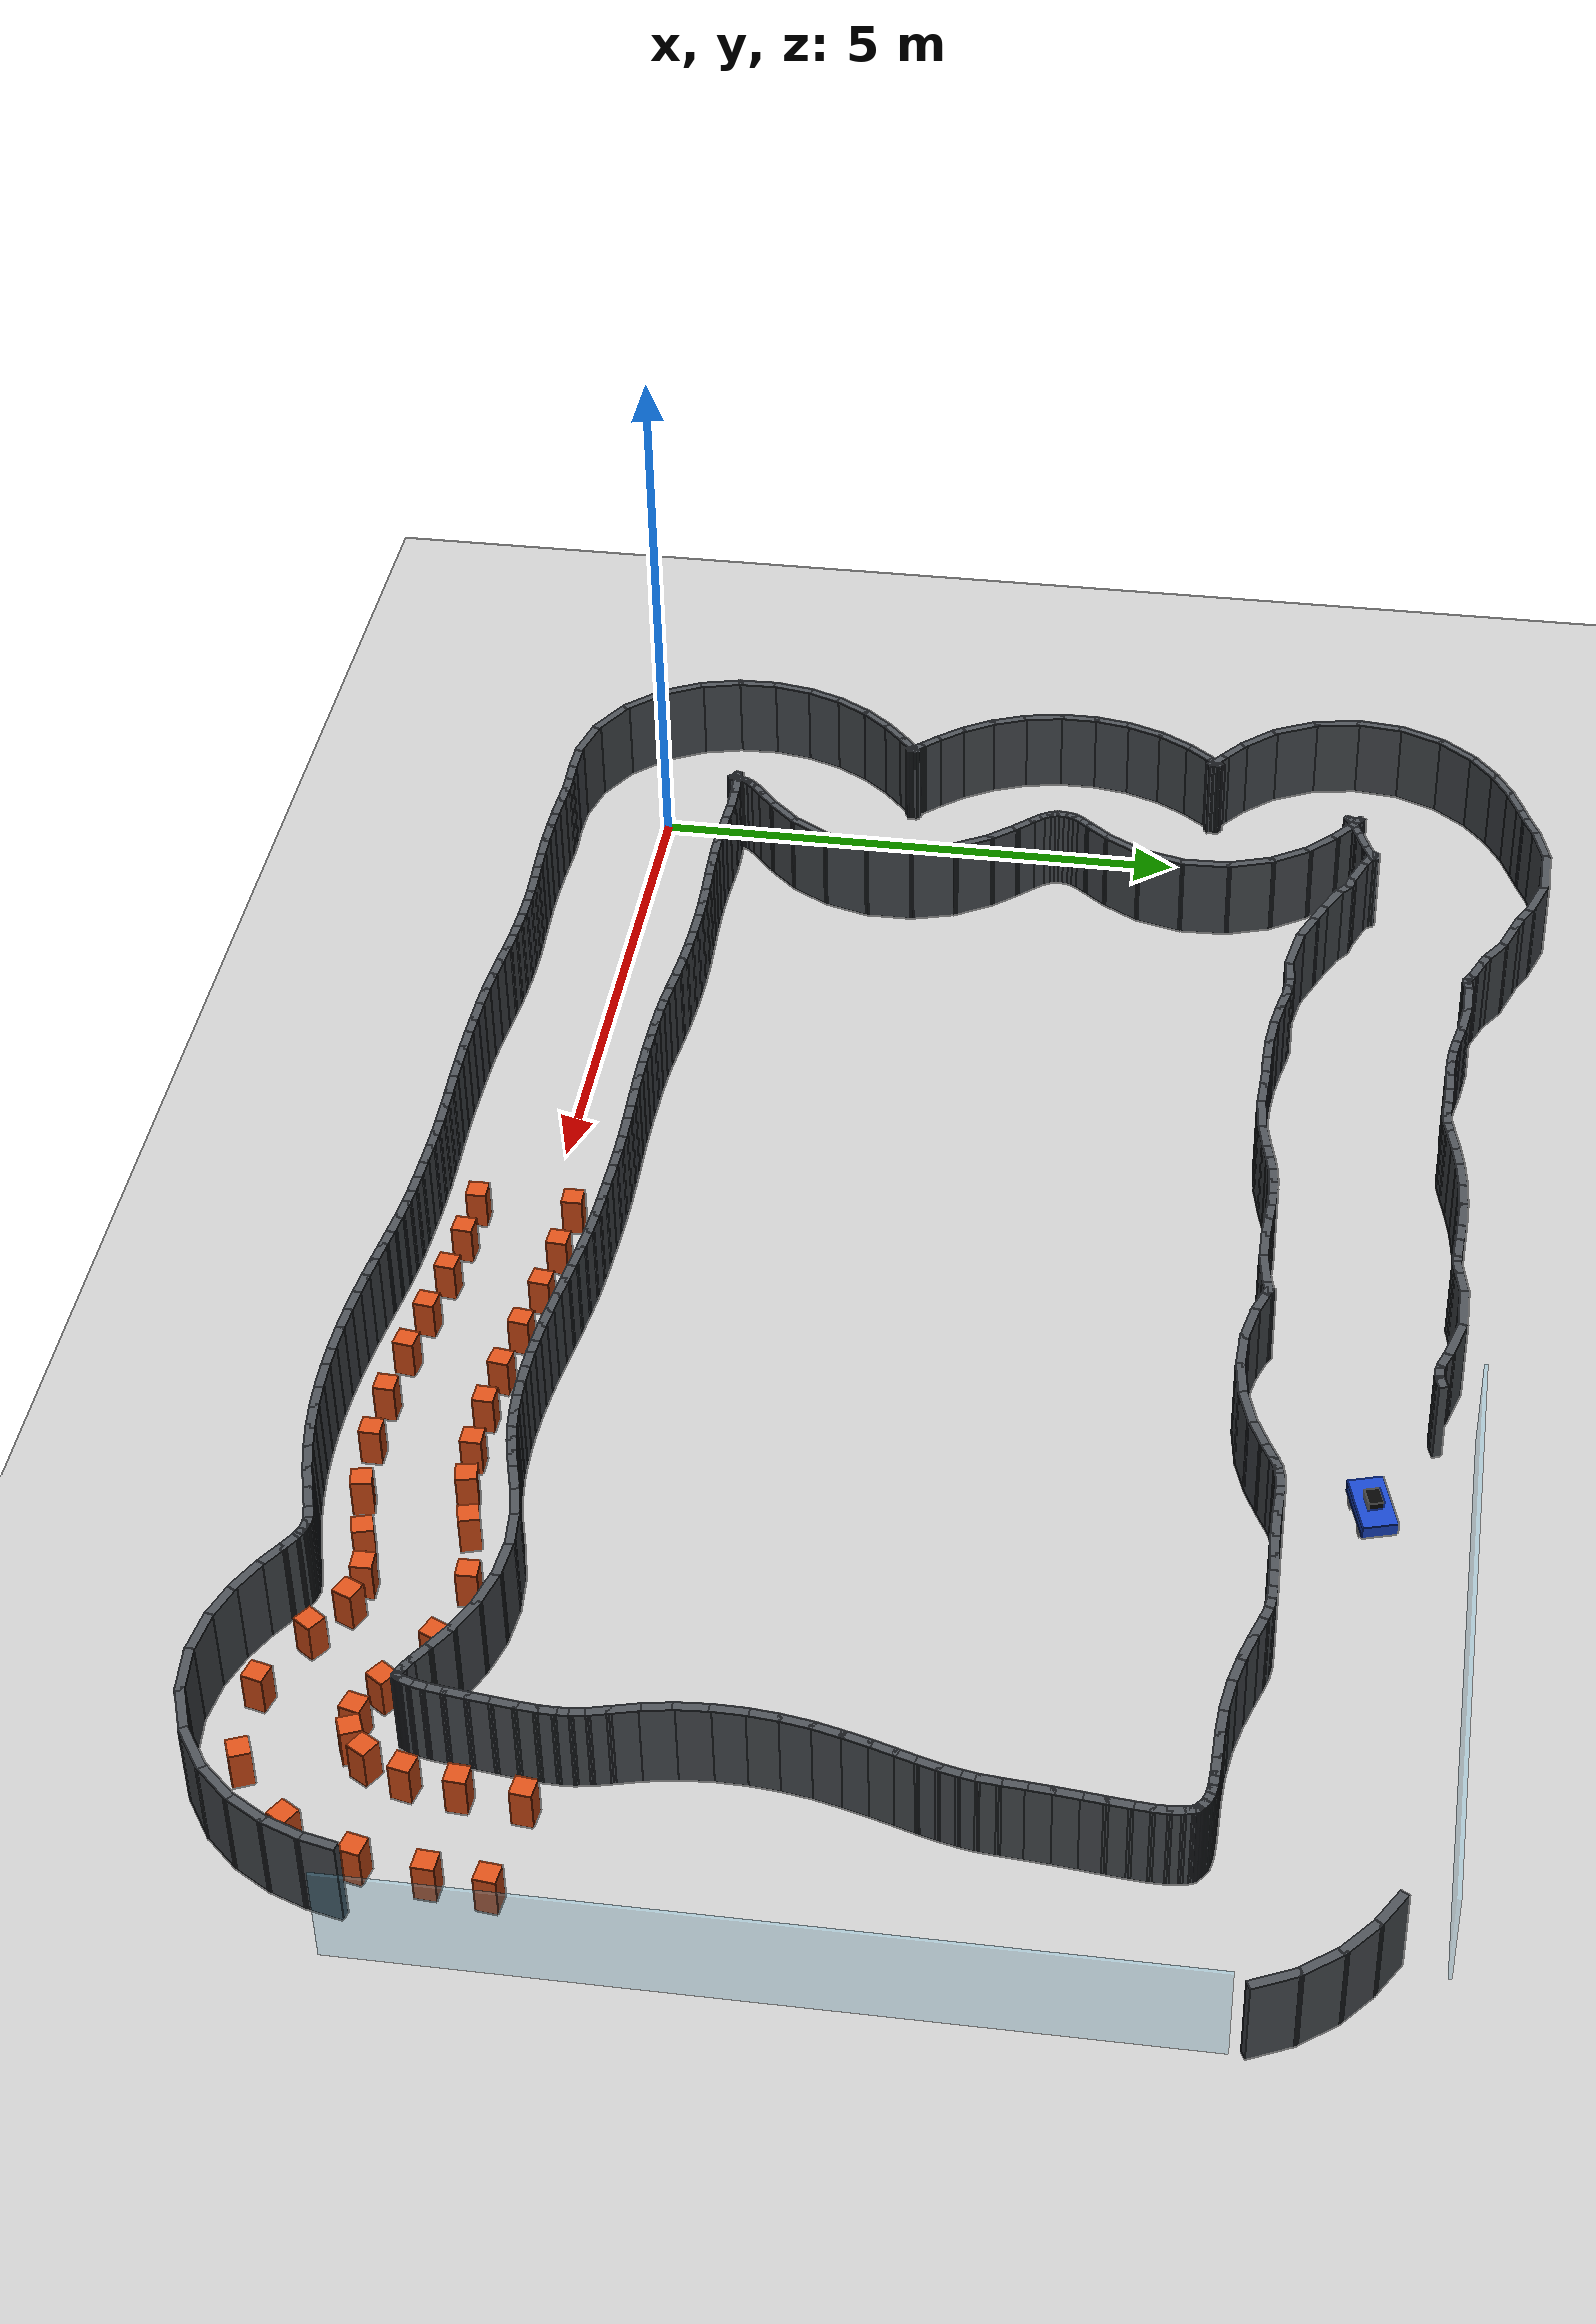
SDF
<?xml version='1.0' encoding='utf-8'?>
<sdf version="1.10">
  <world name="kookmin_xycar_track">
    <gravity>0 0 -9.8000000000000007</gravity>
    <magnetic_field>6.0000000000000002e-06 2.3e-05 -4.1999999999999998e-05</magnetic_field>
    <atmosphere type="adiabatic" />
    <physics name="default_physics" default="true" type="ignored">
      <max_step_size>0.001</max_step_size>
      <real_time_factor>1</real_time_factor>
      <real_time_update_rate>1000</real_time_update_rate>
    </physics>
    <plugin name="gz::sim::systems::Physics" filename="gz-sim-physics-system" />
    <plugin name="gz::sim::systems::UserCommands" filename="gz-sim-user-commands-system" />
    <plugin name="gz::sim::systems::SceneBroadcaster" filename="gz-sim-scene-broadcaster-system" />
    <plugin name="gz::sim::systems::Sensors" filename="gz-sim-sensors-system">
      <render_engine>ogre2</render_engine>
    </plugin>
    <scene>
      <ambient>0.75 0.75 0.75 1</ambient>
      <background>0.819999993 0.839999974 0.860000014 1</background>
      <shadows>false</shadows>
    </scene>
    <light name="sun" type="directional">
      <pose>0 0 10 0 0 0</pose>
      <cast_shadows>false</cast_shadows>
      <intensity>1</intensity>
      <direction>-0.45000000000000001 0.20000000000000001 -0.88</direction>
      <diffuse>0.819999993 0.819999993 0.819999993 1</diffuse>
      <specular>0.200000003 0.200000003 0.200000003 1</specular>
      <attenuation>
        <range>10</range>
        <linear>1</linear>
        <constant>1</constant>
        <quadratic>0</quadratic>
      </attenuation>
      <spot>
        <inner_angle>0</inner_angle>
        <outer_angle>0</outer_angle>
        <falloff>0</falloff>
      </spot>
    </light>
    <model name="slam_map">
      <static>true</static>
      <pose>0.000000 0.000000 0 0 0 0.000000000</pose>
      <link name="map_floor">
        <pose>6.370000 4.105000 0 0 0 0</pose>
        <collision name="floor_collision">
          <pose>0 0 -0.020 0 0 0</pose>
          <geometry>
            <box>
              <size>22.500000 15.850000 0.040000</size>
            </box>
          </geometry>
          <surface>
            <friction>
              <ode>
                <mu>50</mu>
                <mu2>50</mu2>
              </ode>
            </friction>
          </surface>
        </collision>
        <visual name="map_texture">
          <pose>0 0 0.002 0 0 0</pose>
          <geometry>
            <plane>
              <normal>0 0 1</normal>
              <size>22.500000 15.850000</size>
            </plane>
          </geometry>
          <material>
            <pbr>
              <metal>
                <albedo_map>file://maps/slam_glass_balanced/slam_glass_balanced_texture.png</albedo_map>
                <roughness>1</roughness>
                <metalness>0</metalness>
              </metal>
            </pbr>
          </material>
        </visual>
      </link>
      <link name="route_wall_0000">
        <pose>8.857803 6.620077 0.400000 0 0 -2.708154841</pose>
        <collision name="collision">
          <geometry>
            <box>
              <size>0.144515 0.080000 0.800000</size>
            </box>
          </geometry>
        </collision>
        <visual name="visual">
          <geometry>
            <box>
              <size>0.144515 0.080000 0.800000</size>
            </box>
          </geometry>
          <material>
            <ambient>0.3000 0.3200 0.3400 1.0000</ambient>
            <diffuse>0.3000 0.3200 0.3400 1.0000</diffuse>
          </material>
        </visual>
      </link>
      <link name="route_wall_0001">
        <pose>8.728666 6.554908 0.400000 0 0 -2.655052837</pose>
        <collision name="collision">
          <geometry>
            <box>
              <size>0.224877 0.080000 0.800000</size>
            </box>
          </geometry>
        </collision>
        <visual name="visual">
          <geometry>
            <box>
              <size>0.224877 0.080000 0.800000</size>
            </box>
          </geometry>
          <material>
            <ambient>0.3000 0.3200 0.3400 1.0000</ambient>
            <diffuse>0.3000 0.3200 0.3400 1.0000</diffuse>
          </material>
        </visual>
      </link>
      <link name="route_wall_0002">
        <pose>8.525304 6.454000 0.400000 0 0 -2.698798356</pose>
        <collision name="collision">
          <geometry>
            <box>
              <size>0.309270 0.080000 0.800000</size>
            </box>
          </geometry>
        </collision>
        <visual name="visual">
          <geometry>
            <box>
              <size>0.309270 0.080000 0.800000</size>
            </box>
          </geometry>
          <material>
            <ambient>0.3000 0.3200 0.3400 1.0000</ambient>
            <diffuse>0.3000 0.3200 0.3400 1.0000</diffuse>
          </material>
        </visual>
      </link>
      <link name="route_wall_0003">
        <pose>8.250433 6.347098 0.400000 0 0 -2.830795801</pose>
        <collision name="collision">
          <geometry>
            <box>
              <size>0.361861 0.080000 0.800000</size>
            </box>
          </geometry>
        </collision>
        <visual name="visual">
          <geometry>
            <box>
              <size>0.361861 0.080000 0.800000</size>
            </box>
          </geometry>
          <material>
            <ambient>0.3000 0.3200 0.3400 1.0000</ambient>
            <diffuse>0.3000 0.3200 0.3400 1.0000</diffuse>
          </material>
        </visual>
      </link>
      <link name="route_wall_0004">
        <pose>7.930467 6.273002 0.400000 0 0 -2.993469138</pose>
        <collision name="collision">
          <geometry>
            <box>
              <size>0.377185 0.080000 0.800000</size>
            </box>
          </geometry>
        </collision>
        <visual name="visual">
          <geometry>
            <box>
              <size>0.377185 0.080000 0.800000</size>
            </box>
          </geometry>
          <material>
            <ambient>0.3000 0.3200 0.3400 1.0000</ambient>
            <diffuse>0.3000 0.3200 0.3400 1.0000</diffuse>
          </material>
        </visual>
      </link>
      <link name="route_wall_0005">
        <pose>7.593095 6.252334 0.400000 0 0 3.116901750</pose>
        <collision name="collision">
          <geometry>
            <box>
              <size>0.381355 0.080000 0.800000</size>
            </box>
          </geometry>
        </collision>
        <visual name="visual">
          <geometry>
            <box>
              <size>0.381355 0.080000 0.800000</size>
            </box>
          </geometry>
          <material>
            <ambient>0.3000 0.3200 0.3400 1.0000</ambient>
            <diffuse>0.3000 0.3200 0.3400 1.0000</diffuse>
          </material>
        </visual>
      </link>
      <link name="route_wall_0006">
        <pose>7.259372 6.289112 0.400000 0 0 2.944524645</pose>
        <collision name="collision">
          <geometry>
            <box>
              <size>0.372634 0.080000 0.800000</size>
            </box>
          </geometry>
        </collision>
        <visual name="visual">
          <geometry>
            <box>
              <size>0.372634 0.080000 0.800000</size>
            </box>
          </geometry>
          <material>
            <ambient>0.3000 0.3200 0.3400 1.0000</ambient>
            <diffuse>0.3000 0.3200 0.3400 1.0000</diffuse>
          </material>
        </visual>
      </link>
      <link name="route_wall_0007">
        <pose>6.981278 6.362665 0.400000 0 0 2.799193738</pose>
        <collision name="collision">
          <geometry>
            <box>
              <size>0.284166 0.080000 0.800000</size>
            </box>
          </geometry>
        </collision>
        <visual name="visual">
          <geometry>
            <box>
              <size>0.284166 0.080000 0.800000</size>
            </box>
          </geometry>
          <material>
            <ambient>0.3000 0.3200 0.3400 1.0000</ambient>
            <diffuse>0.3000 0.3200 0.3400 1.0000</diffuse>
          </material>
        </visual>
      </link>
      <link name="route_wall_0008">
        <pose>6.844776 6.416185 0.400000 0 0 2.613993806</pose>
        <collision name="collision">
          <geometry>
            <box>
              <size>0.089781 0.080000 0.800000</size>
            </box>
          </geometry>
        </collision>
        <visual name="visual">
          <geometry>
            <box>
              <size>0.089781 0.080000 0.800000</size>
            </box>
          </geometry>
          <material>
            <ambient>0.3000 0.3200 0.3400 1.0000</ambient>
            <diffuse>0.3000 0.3200 0.3400 1.0000</diffuse>
          </material>
        </visual>
      </link>
      <link name="route_wall_0009">
        <pose>6.833306 6.425547 0.400000 0 0 -0.305906039</pose>
        <collision name="collision">
          <geometry>
            <box>
              <size>0.061049 0.080000 0.800000</size>
            </box>
          </geometry>
        </collision>
        <visual name="visual">
          <geometry>
            <box>
              <size>0.061049 0.080000 0.800000</size>
            </box>
          </geometry>
          <material>
            <ambient>0.3000 0.3200 0.3400 1.0000</ambient>
            <diffuse>0.3000 0.3200 0.3400 1.0000</diffuse>
          </material>
        </visual>
      </link>
      <link name="route_wall_0010">
        <pose>6.776032 6.404820 0.400000 0 0 -2.886426362</pose>
        <collision name="collision">
          <geometry>
            <box>
              <size>0.179125 0.080000 0.800000</size>
            </box>
          </geometry>
        </collision>
        <visual name="visual">
          <geometry>
            <box>
              <size>0.179125 0.080000 0.800000</size>
            </box>
          </geometry>
          <material>
            <ambient>0.3000 0.3200 0.3400 1.0000</ambient>
            <diffuse>0.3000 0.3200 0.3400 1.0000</diffuse>
          </material>
        </visual>
      </link>
      <link name="route_wall_0011">
        <pose>6.565508 6.363926 0.400000 0 0 -2.980067752</pose>
        <collision name="collision">
          <geometry>
            <box>
              <size>0.330206 0.080000 0.800000</size>
            </box>
          </geometry>
        </collision>
        <visual name="visual">
          <geometry>
            <box>
              <size>0.330206 0.080000 0.800000</size>
            </box>
          </geometry>
          <material>
            <ambient>0.3000 0.3200 0.3400 1.0000</ambient>
            <diffuse>0.3000 0.3200 0.3400 1.0000</diffuse>
          </material>
        </visual>
      </link>
      <link name="route_wall_0012">
        <pose>6.276092 6.338794 0.400000 0 0 -3.129314466</pose>
        <collision name="collision">
          <geometry>
            <box>
              <size>0.332426 0.080000 0.800000</size>
            </box>
          </geometry>
        </collision>
        <visual name="visual">
          <geometry>
            <box>
              <size>0.332426 0.080000 0.800000</size>
            </box>
          </geometry>
          <material>
            <ambient>0.3000 0.3200 0.3400 1.0000</ambient>
            <diffuse>0.3000 0.3200 0.3400 1.0000</diffuse>
          </material>
        </visual>
      </link>
      <link name="route_wall_0013">
        <pose>6.018642 6.343261 0.400000 0 0 3.085369669</pose>
        <collision name="collision">
          <geometry>
            <box>
              <size>0.262846 0.080000 0.800000</size>
            </box>
          </geometry>
        </collision>
        <visual name="visual">
          <geometry>
            <box>
              <size>0.262846 0.080000 0.800000</size>
            </box>
          </geometry>
          <material>
            <ambient>0.3000 0.3200 0.3400 1.0000</ambient>
            <diffuse>0.3000 0.3200 0.3400 1.0000</diffuse>
          </material>
        </visual>
      </link>
      <link name="route_wall_0014">
        <pose>5.818519 6.354339 0.400000 0 0 3.087443822</pose>
        <collision name="collision">
          <geometry>
            <box>
              <size>0.218013 0.080000 0.800000</size>
            </box>
          </geometry>
        </collision>
        <visual name="visual">
          <geometry>
            <box>
              <size>0.218013 0.080000 0.800000</size>
            </box>
          </geometry>
          <material>
            <ambient>0.3000 0.3200 0.3400 1.0000</ambient>
            <diffuse>0.3000 0.3200 0.3400 1.0000</diffuse>
          </material>
        </visual>
      </link>
      <link name="route_wall_0015">
        <pose>5.651457 6.359594 0.400000 0 0 3.135991821</pose>
        <collision name="collision">
          <geometry>
            <box>
              <size>0.196375 0.080000 0.800000</size>
            </box>
          </geometry>
        </collision>
        <visual name="visual">
          <geometry>
            <box>
              <size>0.196375 0.080000 0.800000</size>
            </box>
          </geometry>
          <material>
            <ambient>0.3000 0.3200 0.3400 1.0000</ambient>
            <diffuse>0.3000 0.3200 0.3400 1.0000</diffuse>
          </material>
        </visual>
      </link>
      <link name="route_wall_0016">
        <pose>5.501870 6.356388 0.400000 0 0 -3.090601143</pose>
        <collision name="collision">
          <geometry>
            <box>
              <size>0.182986 0.080000 0.800000</size>
            </box>
          </geometry>
        </collision>
        <visual name="visual">
          <geometry>
            <box>
              <size>0.182986 0.080000 0.800000</size>
            </box>
          </geometry>
          <material>
            <ambient>0.3000 0.3200 0.3400 1.0000</ambient>
            <diffuse>0.3000 0.3200 0.3400 1.0000</diffuse>
          </material>
        </visual>
      </link>
      <link name="route_wall_0017">
        <pose>5.362836 6.343578 0.400000 0 0 -3.006883744</pose>
        <collision name="collision">
          <geometry>
            <box>
              <size>0.176505 0.080000 0.800000</size>
            </box>
          </geometry>
        </collision>
        <visual name="visual">
          <geometry>
            <box>
              <size>0.176505 0.080000 0.800000</size>
            </box>
          </geometry>
          <material>
            <ambient>0.3000 0.3200 0.3400 1.0000</ambient>
            <diffuse>0.3000 0.3200 0.3400 1.0000</diffuse>
          </material>
        </visual>
      </link>
      <link name="route_wall_0018">
        <pose>5.220229 6.318387 0.400000 0 0 -2.931027820</pose>
        <collision name="collision">
          <geometry>
            <box>
              <size>0.193333 0.080000 0.800000</size>
            </box>
          </geometry>
        </collision>
        <visual name="visual">
          <geometry>
            <box>
              <size>0.193333 0.080000 0.800000</size>
            </box>
          </geometry>
          <material>
            <ambient>0.3000 0.3200 0.3400 1.0000</ambient>
            <diffuse>0.3000 0.3200 0.3400 1.0000</diffuse>
          </material>
        </visual>
      </link>
      <link name="route_wall_0019">
        <pose>5.051302 6.278580 0.400000 0 0 -2.893664224</pose>
        <collision name="collision">
          <geometry>
            <box>
              <size>0.233834 0.080000 0.800000</size>
            </box>
          </geometry>
        </collision>
        <visual name="visual">
          <geometry>
            <box>
              <size>0.233834 0.080000 0.800000</size>
            </box>
          </geometry>
          <material>
            <ambient>0.3000 0.3200 0.3400 1.0000</ambient>
            <diffuse>0.3000 0.3200 0.3400 1.0000</diffuse>
          </material>
        </visual>
      </link>
      <link name="route_wall_0020">
        <pose>4.829941 6.226788 0.400000 0 0 -2.925197887</pose>
        <collision name="collision">
          <geometry>
            <box>
              <size>0.300898 0.080000 0.800000</size>
            </box>
          </geometry>
        </collision>
        <visual name="visual">
          <geometry>
            <box>
              <size>0.300898 0.080000 0.800000</size>
            </box>
          </geometry>
          <material>
            <ambient>0.3000 0.3200 0.3400 1.0000</ambient>
            <diffuse>0.3000 0.3200 0.3400 1.0000</diffuse>
          </material>
        </visual>
      </link>
      <link name="route_wall_0021">
        <pose>4.551450 6.184124 0.400000 0 0 -3.044897436</pose>
        <collision name="collision">
          <geometry>
            <box>
              <size>0.343587 0.080000 0.800000</size>
            </box>
          </geometry>
        </collision>
        <visual name="visual">
          <geometry>
            <box>
              <size>0.343587 0.080000 0.800000</size>
            </box>
          </geometry>
          <material>
            <ambient>0.3000 0.3200 0.3400 1.0000</ambient>
            <diffuse>0.3000 0.3200 0.3400 1.0000</diffuse>
          </material>
        </visual>
      </link>
      <link name="route_wall_0022">
        <pose>4.276502 6.172698 0.400000 0 0 3.115537577</pose>
        <collision name="collision">
          <geometry>
            <box>
              <size>0.287813 0.080000 0.800000</size>
            </box>
          </geometry>
        </collision>
        <visual name="visual">
          <geometry>
            <box>
              <size>0.287813 0.080000 0.800000</size>
            </box>
          </geometry>
          <material>
            <ambient>0.3000 0.3200 0.3400 1.0000</ambient>
            <diffuse>0.3000 0.3200 0.3400 1.0000</diffuse>
          </material>
        </visual>
      </link>
      <link name="route_wall_0023">
        <pose>4.066680 6.177895 0.400000 0 0 3.118690224</pose>
        <collision name="collision">
          <geometry>
            <box>
              <size>0.211960 0.080000 0.800000</size>
            </box>
          </geometry>
        </collision>
        <visual name="visual">
          <geometry>
            <box>
              <size>0.211960 0.080000 0.800000</size>
            </box>
          </geometry>
          <material>
            <ambient>0.3000 0.3200 0.3400 1.0000</ambient>
            <diffuse>0.3000 0.3200 0.3400 1.0000</diffuse>
          </material>
        </visual>
      </link>
      <link name="route_wall_0024">
        <pose>3.880706 6.176388 0.400000 0 0 -3.106851487</pose>
        <collision name="collision">
          <geometry>
            <box>
              <size>0.240152 0.080000 0.800000</size>
            </box>
          </geometry>
        </collision>
        <visual name="visual">
          <geometry>
            <box>
              <size>0.240152 0.080000 0.800000</size>
            </box>
          </geometry>
          <material>
            <ambient>0.3000 0.3200 0.3400 1.0000</ambient>
            <diffuse>0.3000 0.3200 0.3400 1.0000</diffuse>
          </material>
        </visual>
      </link>
      <link name="route_wall_0025">
        <pose>3.656183 6.175736 0.400000 0 0 3.118914098</pose>
        <collision name="collision">
          <geometry>
            <box>
              <size>0.289079 0.080000 0.800000</size>
            </box>
          </geometry>
        </collision>
        <visual name="visual">
          <geometry>
            <box>
              <size>0.289079 0.080000 0.800000</size>
            </box>
          </geometry>
          <material>
            <ambient>0.3000 0.3200 0.3400 1.0000</ambient>
            <diffuse>0.3000 0.3200 0.3400 1.0000</diffuse>
          </material>
        </visual>
      </link>
      <link name="route_wall_0026">
        <pose>3.403484 6.189761 0.400000 0 0 3.054436738</pose>
        <collision name="collision">
          <geometry>
            <box>
              <size>0.297360 0.080000 0.800000</size>
            </box>
          </geometry>
        </collision>
        <visual name="visual">
          <geometry>
            <box>
              <size>0.297360 0.080000 0.800000</size>
            </box>
          </geometry>
          <material>
            <ambient>0.3000 0.3200 0.3400 1.0000</ambient>
            <diffuse>0.3000 0.3200 0.3400 1.0000</diffuse>
          </material>
        </visual>
      </link>
      <link name="route_wall_0027">
        <pose>3.153701 6.220835 0.400000 0 0 2.979582078</pose>
        <collision name="collision">
          <geometry>
            <box>
              <size>0.286408 0.080000 0.800000</size>
            </box>
          </geometry>
        </collision>
        <visual name="visual">
          <geometry>
            <box>
              <size>0.286408 0.080000 0.800000</size>
            </box>
          </geometry>
          <material>
            <ambient>0.3000 0.3200 0.3400 1.0000</ambient>
            <diffuse>0.3000 0.3200 0.3400 1.0000</diffuse>
          </material>
        </visual>
      </link>
      <link name="route_wall_0028">
        <pose>2.938764 6.259848 0.400000 0 0 2.939355882</pose>
        <collision name="collision">
          <geometry>
            <box>
              <size>0.230577 0.080000 0.800000</size>
            </box>
          </geometry>
        </collision>
        <visual name="visual">
          <geometry>
            <box>
              <size>0.230577 0.080000 0.800000</size>
            </box>
          </geometry>
          <material>
            <ambient>0.3000 0.3200 0.3400 1.0000</ambient>
            <diffuse>0.3000 0.3200 0.3400 1.0000</diffuse>
          </material>
        </visual>
      </link>
      <link name="route_wall_0029">
        <pose>2.785933 6.288229 0.400000 0 0 2.987461907</pose>
        <collision name="collision">
          <geometry>
            <box>
              <size>0.160396 0.080000 0.800000</size>
            </box>
          </geometry>
        </collision>
        <visual name="visual">
          <geometry>
            <box>
              <size>0.160396 0.080000 0.800000</size>
            </box>
          </geometry>
          <material>
            <ambient>0.3000 0.3200 0.3400 1.0000</ambient>
            <diffuse>0.3000 0.3200 0.3400 1.0000</diffuse>
          </material>
        </visual>
      </link>
      <link name="route_wall_0030">
        <pose>2.677828 6.297540 0.400000 0 0 3.140164952</pose>
        <collision name="collision">
          <geometry>
            <box>
              <size>0.137243 0.080000 0.800000</size>
            </box>
          </geometry>
        </collision>
        <visual name="visual">
          <geometry>
            <box>
              <size>0.137243 0.080000 0.800000</size>
            </box>
          </geometry>
          <material>
            <ambient>0.3000 0.3200 0.3400 1.0000</ambient>
            <diffuse>0.3000 0.3200 0.3400 1.0000</diffuse>
          </material>
        </visual>
      </link>
      <link name="route_wall_0031">
        <pose>2.495059 6.286499 0.400000 0 0 -3.058956961</pose>
        <collision name="collision">
          <geometry>
            <box>
              <size>0.309212 0.080000 0.800000</size>
            </box>
          </geometry>
        </collision>
        <visual name="visual">
          <geometry>
            <box>
              <size>0.309212 0.080000 0.800000</size>
            </box>
          </geometry>
          <material>
            <ambient>0.3000 0.3200 0.3400 1.0000</ambient>
            <diffuse>0.3000 0.3200 0.3400 1.0000</diffuse>
          </material>
        </visual>
      </link>
      <link name="route_wall_0032">
        <pose>2.158049 6.310664 0.400000 0 0 2.969426668</pose>
        <collision name="collision">
          <geometry>
            <box>
              <size>0.451814 0.080000 0.800000</size>
            </box>
          </geometry>
        </collision>
        <visual name="visual">
          <geometry>
            <box>
              <size>0.451814 0.080000 0.800000</size>
            </box>
          </geometry>
          <material>
            <ambient>0.3000 0.3200 0.3400 1.0000</ambient>
            <diffuse>0.3000 0.3200 0.3400 1.0000</diffuse>
          </material>
        </visual>
      </link>
      <link name="route_wall_0033">
        <pose>1.822978 6.401107 0.400000 0 0 2.746278868</pose>
        <collision name="collision">
          <geometry>
            <box>
              <size>0.326515 0.080000 0.800000</size>
            </box>
          </geometry>
        </collision>
        <visual name="visual">
          <geometry>
            <box>
              <size>0.326515 0.080000 0.800000</size>
            </box>
          </geometry>
          <material>
            <ambient>0.3000 0.3200 0.3400 1.0000</ambient>
            <diffuse>0.3000 0.3200 0.3400 1.0000</diffuse>
          </material>
        </visual>
      </link>
      <link name="route_wall_0034">
        <pose>1.594399 6.496347 0.400000 0 0 2.747526660</pose>
        <collision name="collision">
          <geometry>
            <box>
              <size>0.248737 0.080000 0.800000</size>
            </box>
          </geometry>
        </collision>
        <visual name="visual">
          <geometry>
            <box>
              <size>0.248737 0.080000 0.800000</size>
            </box>
          </geometry>
          <material>
            <ambient>0.3000 0.3200 0.3400 1.0000</ambient>
            <diffuse>0.3000 0.3200 0.3400 1.0000</diffuse>
          </material>
        </visual>
      </link>
      <link name="route_wall_0035">
        <pose>1.366786 6.599541 0.400000 0 0 2.693298429</pose>
        <collision name="collision">
          <geometry>
            <box>
              <size>0.331268 0.080000 0.800000</size>
            </box>
          </geometry>
        </collision>
        <visual name="visual">
          <geometry>
            <box>
              <size>0.331268 0.080000 0.800000</size>
            </box>
          </geometry>
          <material>
            <ambient>0.3000 0.3200 0.3400 1.0000</ambient>
            <diffuse>0.3000 0.3200 0.3400 1.0000</diffuse>
          </material>
        </visual>
      </link>
      <link name="route_wall_0036">
        <pose>1.177283 6.708098 0.400000 0 0 2.479251623</pose>
        <collision name="collision">
          <geometry>
            <box>
              <size>0.187765 0.080000 0.800000</size>
            </box>
          </geometry>
        </collision>
        <visual name="visual">
          <geometry>
            <box>
              <size>0.187765 0.080000 0.800000</size>
            </box>
          </geometry>
          <material>
            <ambient>0.3000 0.3200 0.3400 1.0000</ambient>
            <diffuse>0.3000 0.3200 0.3400 1.0000</diffuse>
          </material>
        </visual>
      </link>
      <link name="route_wall_0037">
        <pose>1.073940 6.762874 0.400000 0 0 2.937290715</pose>
        <collision name="collision">
          <geometry>
            <box>
              <size>0.132080 0.080000 0.800000</size>
            </box>
          </geometry>
        </collision>
        <visual name="visual">
          <geometry>
            <box>
              <size>0.132080 0.080000 0.800000</size>
            </box>
          </geometry>
          <material>
            <ambient>0.3000 0.3200 0.3400 1.0000</ambient>
            <diffuse>0.3000 0.3200 0.3400 1.0000</diffuse>
          </material>
        </visual>
      </link>
      <link name="route_wall_0038">
        <pose>0.901160 6.820513 0.400000 0 0 2.779998943</pose>
        <collision name="collision">
          <geometry>
            <box>
              <size>0.313050 0.080000 0.800000</size>
            </box>
          </geometry>
        </collision>
        <visual name="visual">
          <geometry>
            <box>
              <size>0.313050 0.080000 0.800000</size>
            </box>
          </geometry>
          <material>
            <ambient>0.3000 0.3200 0.3400 1.0000</ambient>
            <diffuse>0.3000 0.3200 0.3400 1.0000</diffuse>
          </material>
        </visual>
      </link>
      <link name="route_wall_0039">
        <pose>0.687721 6.914750 0.400000 0 0 2.649731264</pose>
        <collision name="collision">
          <geometry>
            <box>
              <size>0.234548 0.080000 0.800000</size>
            </box>
          </geometry>
        </collision>
        <visual name="visual">
          <geometry>
            <box>
              <size>0.234548 0.080000 0.800000</size>
            </box>
          </geometry>
          <material>
            <ambient>0.3000 0.3200 0.3400 1.0000</ambient>
            <diffuse>0.3000 0.3200 0.3400 1.0000</diffuse>
          </material>
        </visual>
      </link>
      <link name="route_wall_0040">
        <pose>0.601748 6.965573 0.400000 0 0 1.617759873</pose>
        <collision name="collision">
          <geometry>
            <box>
              <size>0.049777 0.080000 0.800000</size>
            </box>
          </geometry>
        </collision>
        <visual name="visual">
          <geometry>
            <box>
              <size>0.049777 0.080000 0.800000</size>
            </box>
          </geometry>
          <material>
            <ambient>0.3000 0.3200 0.3400 1.0000</ambient>
            <diffuse>0.3000 0.3200 0.3400 1.0000</diffuse>
          </material>
        </visual>
      </link>
      <link name="route_wall_0041">
        <pose>0.634148 6.969611 0.400000 0 0 -0.025913968</pose>
        <collision name="collision">
          <geometry>
            <box>
              <size>0.105280 0.080000 0.800000</size>
            </box>
          </geometry>
        </collision>
        <visual name="visual">
          <geometry>
            <box>
              <size>0.105280 0.080000 0.800000</size>
            </box>
          </geometry>
          <material>
            <ambient>0.3000 0.3200 0.3400 1.0000</ambient>
            <diffuse>0.3000 0.3200 0.3400 1.0000</diffuse>
          </material>
        </visual>
      </link>
      <link name="route_wall_0042">
        <pose>0.659911 6.962137 0.400000 0 0 -2.373852807</pose>
        <collision name="collision">
          <geometry>
            <box>
              <size>0.059085 0.080000 0.800000</size>
            </box>
          </geometry>
        </collision>
        <visual name="visual">
          <geometry>
            <box>
              <size>0.059085 0.080000 0.800000</size>
            </box>
          </geometry>
          <material>
            <ambient>0.3000 0.3200 0.3400 1.0000</ambient>
            <diffuse>0.3000 0.3200 0.3400 1.0000</diffuse>
          </material>
        </visual>
      </link>
      <link name="route_wall_0043">
        <pose>0.576813 6.919122 0.400000 0 0 -2.696242966</pose>
        <collision name="collision">
          <geometry>
            <box>
              <size>0.208943 0.080000 0.800000</size>
            </box>
          </geometry>
        </collision>
        <visual name="visual">
          <geometry>
            <box>
              <size>0.208943 0.080000 0.800000</size>
            </box>
          </geometry>
          <material>
            <ambient>0.3000 0.3200 0.3400 1.0000</ambient>
            <diffuse>0.3000 0.3200 0.3400 1.0000</diffuse>
          </material>
        </visual>
      </link>
      <link name="route_wall_0044">
        <pose>0.399805 6.842053 0.400000 0 0 -2.757925123</pose>
        <collision name="collision">
          <geometry>
            <box>
              <size>0.257355 0.080000 0.800000</size>
            </box>
          </geometry>
        </collision>
        <visual name="visual">
          <geometry>
            <box>
              <size>0.257355 0.080000 0.800000</size>
            </box>
          </geometry>
          <material>
            <ambient>0.3000 0.3200 0.3400 1.0000</ambient>
            <diffuse>0.3000 0.3200 0.3400 1.0000</diffuse>
          </material>
        </visual>
      </link>
      <link name="route_wall_0045">
        <pose>0.232785 6.774767 0.400000 0 0 -2.759674588</pose>
        <collision name="collision">
          <geometry>
            <box>
              <size>0.182774 0.080000 0.800000</size>
            </box>
          </geometry>
        </collision>
        <visual name="visual">
          <geometry>
            <box>
              <size>0.182774 0.080000 0.800000</size>
            </box>
          </geometry>
          <material>
            <ambient>0.3000 0.3200 0.3400 1.0000</ambient>
            <diffuse>0.3000 0.3200 0.3400 1.0000</diffuse>
          </material>
        </visual>
      </link>
      <link name="route_wall_0046">
        <pose>0.131454 6.728596 0.400000 0 0 -2.632941077</pose>
        <collision name="collision">
          <geometry>
            <box>
              <size>0.120346 0.080000 0.800000</size>
            </box>
          </geometry>
        </collision>
        <visual name="visual">
          <geometry>
            <box>
              <size>0.120346 0.080000 0.800000</size>
            </box>
          </geometry>
          <material>
            <ambient>0.3000 0.3200 0.3400 1.0000</ambient>
            <diffuse>0.3000 0.3200 0.3400 1.0000</diffuse>
          </material>
        </visual>
      </link>
      <link name="route_wall_0047">
        <pose>0.076665 6.693876 0.400000 0 0 -2.485856049</pose>
        <collision name="collision">
          <geometry>
            <box>
              <size>0.089714 0.080000 0.800000</size>
            </box>
          </geometry>
        </collision>
        <visual name="visual">
          <geometry>
            <box>
              <size>0.089714 0.080000 0.800000</size>
            </box>
          </geometry>
          <material>
            <ambient>0.3000 0.3200 0.3400 1.0000</ambient>
            <diffuse>0.3000 0.3200 0.3400 1.0000</diffuse>
          </material>
        </visual>
      </link>
      <link name="route_wall_0048">
        <pose>0.055192 6.679678 0.400000 0 0 2.645624647</pose>
        <collision name="collision">
          <geometry>
            <box>
              <size>0.044028 0.080000 0.800000</size>
            </box>
          </geometry>
        </collision>
        <visual name="visual">
          <geometry>
            <box>
              <size>0.044028 0.080000 0.800000</size>
            </box>
          </geometry>
          <material>
            <ambient>0.3000 0.3200 0.3400 1.0000</ambient>
            <diffuse>0.3000 0.3200 0.3400 1.0000</diffuse>
          </material>
        </visual>
      </link>
      <link name="route_wall_0049">
        <pose>0.059844 6.696252 0.400000 0 0 1.180505814</pose>
        <collision name="collision">
          <geometry>
            <box>
              <size>0.073771 0.080000 0.800000</size>
            </box>
          </geometry>
        </collision>
        <visual name="visual">
          <geometry>
            <box>
              <size>0.073771 0.080000 0.800000</size>
            </box>
          </geometry>
          <material>
            <ambient>0.3000 0.3200 0.3400 1.0000</ambient>
            <diffuse>0.3000 0.3200 0.3400 1.0000</diffuse>
          </material>
        </visual>
      </link>
      <link name="route_wall_0050">
        <pose>0.068265 6.727100 0.400000 0 0 1.440461473</pose>
        <collision name="collision">
          <geometry>
            <box>
              <size>0.070726 0.080000 0.800000</size>
            </box>
          </geometry>
        </collision>
        <visual name="visual">
          <geometry>
            <box>
              <size>0.070726 0.080000 0.800000</size>
            </box>
          </geometry>
          <material>
            <ambient>0.3000 0.3200 0.3400 1.0000</ambient>
            <diffuse>0.3000 0.3200 0.3400 1.0000</diffuse>
          </material>
        </visual>
      </link>
      <link name="route_wall_0051">
        <pose>0.067244 6.757899 0.400000 0 0 1.762306409</pose>
        <collision name="collision">
          <geometry>
            <box>
              <size>0.071711 0.080000 0.800000</size>
            </box>
          </geometry>
        </collision>
        <visual name="visual">
          <geometry>
            <box>
              <size>0.071711 0.080000 0.800000</size>
            </box>
          </geometry>
          <material>
            <ambient>0.3000 0.3200 0.3400 1.0000</ambient>
            <diffuse>0.3000 0.3200 0.3400 1.0000</diffuse>
          </material>
        </visual>
      </link>
      <link name="route_wall_0052">
        <pose>0.056206 6.789823 0.400000 0 0 2.026629559</pose>
        <collision name="collision">
          <geometry>
            <box>
              <size>0.076438 0.080000 0.800000</size>
            </box>
          </geometry>
        </collision>
        <visual name="visual">
          <geometry>
            <box>
              <size>0.076438 0.080000 0.800000</size>
            </box>
          </geometry>
          <material>
            <ambient>0.3000 0.3200 0.3400 1.0000</ambient>
            <diffuse>0.3000 0.3200 0.3400 1.0000</diffuse>
          </material>
        </visual>
      </link>
      <link name="route_wall_0053">
        <pose>0.054252 6.803685 0.400000 0 0 -0.390416202</pose>
        <collision name="collision">
          <geometry>
            <box>
              <size>0.053120 0.080000 0.800000</size>
            </box>
          </geometry>
        </collision>
        <visual name="visual">
          <geometry>
            <box>
              <size>0.053120 0.080000 0.800000</size>
            </box>
          </geometry>
          <material>
            <ambient>0.3000 0.3200 0.3400 1.0000</ambient>
            <diffuse>0.3000 0.3200 0.3400 1.0000</diffuse>
          </material>
        </visual>
      </link>
      <link name="route_wall_0054">
        <pose>0.112756 6.762896 0.400000 0 0 -0.630745345</pose>
        <collision name="collision">
          <geometry>
            <box>
              <size>0.169862 0.080000 0.800000</size>
            </box>
          </geometry>
        </collision>
        <visual name="visual">
          <geometry>
            <box>
              <size>0.169862 0.080000 0.800000</size>
            </box>
          </geometry>
          <material>
            <ambient>0.3000 0.3200 0.3400 1.0000</ambient>
            <diffuse>0.3000 0.3200 0.3400 1.0000</diffuse>
          </material>
        </visual>
      </link>
      <link name="route_wall_0055">
        <pose>0.263308 6.648690 0.400000 0 0 -0.658507556</pose>
        <collision name="collision">
          <geometry>
            <box>
              <size>0.288107 0.080000 0.800000</size>
            </box>
          </geometry>
        </collision>
        <visual name="visual">
          <geometry>
            <box>
              <size>0.288107 0.080000 0.800000</size>
            </box>
          </geometry>
          <material>
            <ambient>0.3000 0.3200 0.3400 1.0000</ambient>
            <diffuse>0.3000 0.3200 0.3400 1.0000</diffuse>
          </material>
        </visual>
      </link>
      <link name="route_wall_0056">
        <pose>0.481211 6.453624 0.400000 0 0 -0.782736762</pose>
        <collision name="collision">
          <geometry>
            <box>
              <size>0.377915 0.080000 0.800000</size>
            </box>
          </geometry>
        </collision>
        <visual name="visual">
          <geometry>
            <box>
              <size>0.377915 0.080000 0.800000</size>
            </box>
          </geometry>
          <material>
            <ambient>0.3000 0.3200 0.3400 1.0000</ambient>
            <diffuse>0.3000 0.3200 0.3400 1.0000</diffuse>
          </material>
        </visual>
      </link>
      <link name="route_wall_0057">
        <pose>0.708033 6.168649 0.400000 0 0 -0.997615465</pose>
        <collision name="collision">
          <geometry>
            <box>
              <size>0.434732 0.080000 0.800000</size>
            </box>
          </geometry>
        </collision>
        <visual name="visual">
          <geometry>
            <box>
              <size>0.434732 0.080000 0.800000</size>
            </box>
          </geometry>
          <material>
            <ambient>0.3000 0.3200 0.3400 1.0000</ambient>
            <diffuse>0.3000 0.3200 0.3400 1.0000</diffuse>
          </material>
        </visual>
      </link>
      <link name="route_wall_0058">
        <pose>0.880274 5.802291 0.400000 0 0 -1.256408148</pose>
        <collision name="collision">
          <geometry>
            <box>
              <size>0.461740 0.080000 0.800000</size>
            </box>
          </geometry>
        </collision>
        <visual name="visual">
          <geometry>
            <box>
              <size>0.461740 0.080000 0.800000</size>
            </box>
          </geometry>
          <material>
            <ambient>0.3000 0.3200 0.3400 1.0000</ambient>
            <diffuse>0.3000 0.3200 0.3400 1.0000</diffuse>
          </material>
        </visual>
      </link>
      <link name="route_wall_0059">
        <pose>0.951910 5.383896 0.400000 0 0 -1.541303337</pose>
        <collision name="collision">
          <geometry>
            <box>
              <size>0.475912 0.080000 0.800000</size>
            </box>
          </geometry>
        </collision>
        <visual name="visual">
          <geometry>
            <box>
              <size>0.475912 0.080000 0.800000</size>
            </box>
          </geometry>
          <material>
            <ambient>0.3000 0.3200 0.3400 1.0000</ambient>
            <diffuse>0.3000 0.3200 0.3400 1.0000</diffuse>
          </material>
        </visual>
      </link>
      <link name="route_wall_0060">
        <pose>0.902152 4.957134 0.400000 0 0 -1.833533494</pose>
        <collision name="collision">
          <geometry>
            <box>
              <size>0.472651 0.080000 0.800000</size>
            </box>
          </geometry>
        </collision>
        <visual name="visual">
          <geometry>
            <box>
              <size>0.472651 0.080000 0.800000</size>
            </box>
          </geometry>
          <material>
            <ambient>0.3000 0.3200 0.3400 1.0000</ambient>
            <diffuse>0.3000 0.3200 0.3400 1.0000</diffuse>
          </material>
        </visual>
      </link>
      <link name="route_wall_0061">
        <pose>0.751174 4.586245 0.400000 0 0 -2.100253503</pose>
        <collision name="collision">
          <geometry>
            <box>
              <size>0.415368 0.080000 0.800000</size>
            </box>
          </geometry>
        </collision>
        <visual name="visual">
          <geometry>
            <box>
              <size>0.415368 0.080000 0.800000</size>
            </box>
          </geometry>
          <material>
            <ambient>0.3000 0.3200 0.3400 1.0000</ambient>
            <diffuse>0.3000 0.3200 0.3400 1.0000</diffuse>
          </material>
        </visual>
      </link>
      <link name="route_wall_0062">
        <pose>0.575559 4.326039 0.400000 0 0 -2.259334244</pose>
        <collision name="collision">
          <geometry>
            <box>
              <size>0.294397 0.080000 0.800000</size>
            </box>
          </geometry>
        </collision>
        <visual name="visual">
          <geometry>
            <box>
              <size>0.294397 0.080000 0.800000</size>
            </box>
          </geometry>
          <material>
            <ambient>0.3000 0.3200 0.3400 1.0000</ambient>
            <diffuse>0.3000 0.3200 0.3400 1.0000</diffuse>
          </material>
        </visual>
      </link>
      <link name="route_wall_0063">
        <pose>0.452438 4.177087 0.400000 0 0 -2.265780603</pose>
        <collision name="collision">
          <geometry>
            <box>
              <size>0.172104 0.080000 0.800000</size>
            </box>
          </geometry>
        </collision>
        <visual name="visual">
          <geometry>
            <box>
              <size>0.172104 0.080000 0.800000</size>
            </box>
          </geometry>
          <material>
            <ambient>0.3000 0.3200 0.3400 1.0000</ambient>
            <diffuse>0.3000 0.3200 0.3400 1.0000</diffuse>
          </material>
        </visual>
      </link>
      <link name="route_wall_0064">
        <pose>0.392894 4.098183 0.400000 0 0 -2.120125550</pose>
        <collision name="collision">
          <geometry>
            <box>
              <size>0.106064 0.080000 0.800000</size>
            </box>
          </geometry>
        </collision>
        <visual name="visual">
          <geometry>
            <box>
              <size>0.106064 0.080000 0.800000</size>
            </box>
          </geometry>
          <material>
            <ambient>0.3000 0.3200 0.3400 1.0000</ambient>
            <diffuse>0.3000 0.3200 0.3400 1.0000</diffuse>
          </material>
        </visual>
      </link>
      <link name="route_wall_0065">
        <pose>0.366701 4.045649 0.400000 0 0 -1.922732345</pose>
        <collision name="collision">
          <geometry>
            <box>
              <size>0.091906 0.080000 0.800000</size>
            </box>
          </geometry>
        </collision>
        <visual name="visual">
          <geometry>
            <box>
              <size>0.091906 0.080000 0.800000</size>
            </box>
          </geometry>
          <material>
            <ambient>0.3000 0.3200 0.3400 1.0000</ambient>
            <diffuse>0.3000 0.3200 0.3400 1.0000</diffuse>
          </material>
        </visual>
      </link>
      <link name="route_wall_0066">
        <pose>0.353142 3.993082 0.400000 0 0 -1.732886128</pose>
        <collision name="collision">
          <geometry>
            <box>
              <size>0.097160 0.080000 0.800000</size>
            </box>
          </geometry>
        </collision>
        <visual name="visual">
          <geometry>
            <box>
              <size>0.097160 0.080000 0.800000</size>
            </box>
          </geometry>
          <material>
            <ambient>0.3000 0.3200 0.3400 1.0000</ambient>
            <diffuse>0.3000 0.3200 0.3400 1.0000</diffuse>
          </material>
        </visual>
      </link>
      <link name="route_wall_0067">
        <pose>0.348047 3.938284 0.400000 0 0 -1.588963887</pose>
        <collision name="collision">
          <geometry>
            <box>
              <size>0.093194 0.080000 0.800000</size>
            </box>
          </geometry>
        </collision>
        <visual name="visual">
          <geometry>
            <box>
              <size>0.093194 0.080000 0.800000</size>
            </box>
          </geometry>
          <material>
            <ambient>0.3000 0.3200 0.3400 1.0000</ambient>
            <diffuse>0.3000 0.3200 0.3400 1.0000</diffuse>
          </material>
        </visual>
      </link>
      <link name="route_wall_0068">
        <pose>0.351519 3.890742 0.400000 0 0 -1.384163306</pose>
        <collision name="collision">
          <geometry>
            <box>
              <size>0.082639 0.080000 0.800000</size>
            </box>
          </geometry>
        </collision>
        <visual name="visual">
          <geometry>
            <box>
              <size>0.082639 0.080000 0.800000</size>
            </box>
          </geometry>
          <material>
            <ambient>0.3000 0.3200 0.3400 1.0000</ambient>
            <diffuse>0.3000 0.3200 0.3400 1.0000</diffuse>
          </material>
        </visual>
      </link>
      <link name="route_wall_0069">
        <pose>0.365880 3.845267 0.400000 0 0 -1.169572810</pose>
        <collision name="collision">
          <geometry>
            <box>
              <size>0.093284 0.080000 0.800000</size>
            </box>
          </geometry>
        </collision>
        <visual name="visual">
          <geometry>
            <box>
              <size>0.093284 0.080000 0.800000</size>
            </box>
          </geometry>
          <material>
            <ambient>0.3000 0.3200 0.3400 1.0000</ambient>
            <diffuse>0.3000 0.3200 0.3400 1.0000</diffuse>
          </material>
        </visual>
      </link>
      <link name="route_wall_0070">
        <pose>0.394767 3.790840 0.400000 0 0 -1.017163962</pose>
        <collision name="collision">
          <geometry>
            <box>
              <size>0.110302 0.080000 0.800000</size>
            </box>
          </geometry>
        </collision>
        <visual name="visual">
          <geometry>
            <box>
              <size>0.110302 0.080000 0.800000</size>
            </box>
          </geometry>
          <material>
            <ambient>0.3000 0.3200 0.3400 1.0000</ambient>
            <diffuse>0.3000 0.3200 0.3400 1.0000</diffuse>
          </material>
        </visual>
      </link>
      <link name="route_wall_0071">
        <pose>0.452056 3.716382 0.400000 0 0 -0.854267817</pose>
        <collision name="collision">
          <geometry>
            <box>
              <size>0.158177 0.080000 0.800000</size>
            </box>
          </geometry>
        </collision>
        <visual name="visual">
          <geometry>
            <box>
              <size>0.158177 0.080000 0.800000</size>
            </box>
          </geometry>
          <material>
            <ambient>0.3000 0.3200 0.3400 1.0000</ambient>
            <diffuse>0.3000 0.3200 0.3400 1.0000</diffuse>
          </material>
        </visual>
      </link>
      <link name="route_wall_0072">
        <pose>0.558555 3.598743 0.400000 0 0 -0.823668303</pose>
        <collision name="collision">
          <geometry>
            <box>
              <size>0.239228 0.080000 0.800000</size>
            </box>
          </geometry>
        </collision>
        <visual name="visual">
          <geometry>
            <box>
              <size>0.239228 0.080000 0.800000</size>
            </box>
          </geometry>
          <material>
            <ambient>0.3000 0.3200 0.3400 1.0000</ambient>
            <diffuse>0.3000 0.3200 0.3400 1.0000</diffuse>
          </material>
        </visual>
      </link>
      <link name="route_wall_0073">
        <pose>0.716644 3.416493 0.400000 0 0 -0.879181869</pose>
        <collision name="collision">
          <geometry>
            <box>
              <size>0.323475 0.080000 0.800000</size>
            </box>
          </geometry>
        </collision>
        <visual name="visual">
          <geometry>
            <box>
              <size>0.323475 0.080000 0.800000</size>
            </box>
          </geometry>
          <material>
            <ambient>0.3000 0.3200 0.3400 1.0000</ambient>
            <diffuse>0.3000 0.3200 0.3400 1.0000</diffuse>
          </material>
        </visual>
      </link>
      <link name="route_wall_0074">
        <pose>0.901000 3.146419 0.400000 0 0 -1.042271819</pose>
        <collision name="collision">
          <geometry>
            <box>
              <size>0.412660 0.080000 0.800000</size>
            </box>
          </geometry>
        </collision>
        <visual name="visual">
          <geometry>
            <box>
              <size>0.412660 0.080000 0.800000</size>
            </box>
          </geometry>
          <material>
            <ambient>0.3000 0.3200 0.3400 1.0000</ambient>
            <diffuse>0.3000 0.3200 0.3400 1.0000</diffuse>
          </material>
        </visual>
      </link>
      <link name="route_wall_0075">
        <pose>1.051302 2.784785 0.400000 0 0 -1.297140389</pose>
        <collision name="collision">
          <geometry>
            <box>
              <size>0.456972 0.080000 0.800000</size>
            </box>
          </geometry>
        </collision>
        <visual name="visual">
          <geometry>
            <box>
              <size>0.456972 0.080000 0.800000</size>
            </box>
          </geometry>
          <material>
            <ambient>0.3000 0.3200 0.3400 1.0000</ambient>
            <diffuse>0.3000 0.3200 0.3400 1.0000</diffuse>
          </material>
        </visual>
      </link>
      <link name="route_wall_0076">
        <pose>1.108245 2.371218 0.400000 0 0 -1.567984853</pose>
        <collision name="collision">
          <geometry>
            <box>
              <size>0.465679 0.080000 0.800000</size>
            </box>
          </geometry>
        </collision>
        <visual name="visual">
          <geometry>
            <box>
              <size>0.465679 0.080000 0.800000</size>
            </box>
          </geometry>
          <material>
            <ambient>0.3000 0.3200 0.3400 1.0000</ambient>
            <diffuse>0.3000 0.3200 0.3400 1.0000</diffuse>
          </material>
        </visual>
      </link>
      <link name="route_wall_0077">
        <pose>1.050243 1.954726 0.400000 0 0 -1.850973391</pose>
        <collision name="collision">
          <geometry>
            <box>
              <size>0.463832 0.080000 0.800000</size>
            </box>
          </geometry>
        </collision>
        <visual name="visual">
          <geometry>
            <box>
              <size>0.463832 0.080000 0.800000</size>
            </box>
          </geometry>
          <material>
            <ambient>0.3000 0.3200 0.3400 1.0000</ambient>
            <diffuse>0.3000 0.3200 0.3400 1.0000</diffuse>
          </material>
        </visual>
      </link>
      <link name="route_wall_0078">
        <pose>0.889145 1.580914 0.400000 0 0 -2.112951959</pose>
        <collision name="collision">
          <geometry>
            <box>
              <size>0.437292 0.080000 0.800000</size>
            </box>
          </geometry>
        </collision>
        <visual name="visual">
          <geometry>
            <box>
              <size>0.437292 0.080000 0.800000</size>
            </box>
          </geometry>
          <material>
            <ambient>0.3000 0.3200 0.3400 1.0000</ambient>
            <diffuse>0.3000 0.3200 0.3400 1.0000</diffuse>
          </material>
        </visual>
      </link>
      <link name="route_wall_0079">
        <pose>0.673524 1.291206 0.400000 0 0 -2.328585380</pose>
        <collision name="collision">
          <geometry>
            <box>
              <size>0.369170 0.080000 0.800000</size>
            </box>
          </geometry>
        </collision>
        <visual name="visual">
          <geometry>
            <box>
              <size>0.369170 0.080000 0.800000</size>
            </box>
          </geometry>
          <material>
            <ambient>0.3000 0.3200 0.3400 1.0000</ambient>
            <diffuse>0.3000 0.3200 0.3400 1.0000</diffuse>
          </material>
        </visual>
      </link>
      <link name="route_wall_0080">
        <pose>0.474333 1.097878 0.400000 0 0 -2.432916965</pose>
        <collision name="collision">
          <geometry>
            <box>
              <size>0.266729 0.080000 0.800000</size>
            </box>
          </geometry>
        </collision>
        <visual name="visual">
          <geometry>
            <box>
              <size>0.266729 0.080000 0.800000</size>
            </box>
          </geometry>
          <material>
            <ambient>0.3000 0.3200 0.3400 1.0000</ambient>
            <diffuse>0.3000 0.3200 0.3400 1.0000</diffuse>
          </material>
        </visual>
      </link>
      <link name="route_wall_0081">
        <pose>0.336733 0.978597 0.400000 0 0 -2.418269901</pose>
        <collision name="collision">
          <geometry>
            <box>
              <size>0.177488 0.080000 0.800000</size>
            </box>
          </geometry>
        </collision>
        <visual name="visual">
          <geometry>
            <box>
              <size>0.177488 0.080000 0.800000</size>
            </box>
          </geometry>
          <material>
            <ambient>0.3000 0.3200 0.3400 1.0000</ambient>
            <diffuse>0.3000 0.3200 0.3400 1.0000</diffuse>
          </material>
        </visual>
      </link>
      <link name="route_wall_0082">
        <pose>0.259336 0.904452 0.400000 0 0 -2.305255522</pose>
        <collision name="collision">
          <geometry>
            <box>
              <size>0.117190 0.080000 0.800000</size>
            </box>
          </geometry>
        </collision>
        <visual name="visual">
          <geometry>
            <box>
              <size>0.117190 0.080000 0.800000</size>
            </box>
          </geometry>
          <material>
            <ambient>0.3000 0.3200 0.3400 1.0000</ambient>
            <diffuse>0.3000 0.3200 0.3400 1.0000</diffuse>
          </material>
        </visual>
      </link>
      <link name="route_wall_0083">
        <pose>0.218987 0.851345 0.400000 0 0 -2.105349764</pose>
        <collision name="collision">
          <geometry>
            <box>
              <size>0.096856 0.080000 0.800000</size>
            </box>
          </geometry>
        </collision>
        <visual name="visual">
          <geometry>
            <box>
              <size>0.096856 0.080000 0.800000</size>
            </box>
          </geometry>
          <material>
            <ambient>0.3000 0.3200 0.3400 1.0000</ambient>
            <diffuse>0.3000 0.3200 0.3400 1.0000</diffuse>
          </material>
        </visual>
      </link>
      <link name="route_wall_0084">
        <pose>0.194809 0.802022 0.400000 0 0 -1.942666619</pose>
        <collision name="collision">
          <geometry>
            <box>
              <size>0.093369 0.080000 0.800000</size>
            </box>
          </geometry>
        </collision>
        <visual name="visual">
          <geometry>
            <box>
              <size>0.093369 0.080000 0.800000</size>
            </box>
          </geometry>
          <material>
            <ambient>0.3000 0.3200 0.3400 1.0000</ambient>
            <diffuse>0.3000 0.3200 0.3400 1.0000</diffuse>
          </material>
        </visual>
      </link>
      <link name="route_wall_0085">
        <pose>0.181132 0.757166 0.400000 0 0 -1.767325091</pose>
        <collision name="collision">
          <geometry>
            <box>
              <size>0.080775 0.080000 0.800000</size>
            </box>
          </geometry>
        </collision>
        <visual name="visual">
          <geometry>
            <box>
              <size>0.080775 0.080000 0.800000</size>
            </box>
          </geometry>
          <material>
            <ambient>0.3000 0.3200 0.3400 1.0000</ambient>
            <diffuse>0.3000 0.3200 0.3400 1.0000</diffuse>
          </material>
        </visual>
      </link>
      <link name="route_wall_0086">
        <pose>0.177388 0.722075 0.400000 0 0 -1.555043667</pose>
        <collision name="collision">
          <geometry>
            <box>
              <size>0.070195 0.080000 0.800000</size>
            </box>
          </geometry>
        </collision>
        <visual name="visual">
          <geometry>
            <box>
              <size>0.070195 0.080000 0.800000</size>
            </box>
          </geometry>
          <material>
            <ambient>0.3000 0.3200 0.3400 1.0000</ambient>
            <diffuse>0.3000 0.3200 0.3400 1.0000</diffuse>
          </material>
        </visual>
      </link>
      <link name="route_wall_0087">
        <pose>0.179727 0.696767 0.400000 0 0 -1.367932783</pose>
        <collision name="collision">
          <geometry>
            <box>
              <size>0.060853 0.080000 0.800000</size>
            </box>
          </geometry>
        </collision>
        <visual name="visual">
          <geometry>
            <box>
              <size>0.060853 0.080000 0.800000</size>
            </box>
          </geometry>
          <material>
            <ambient>0.3000 0.3200 0.3400 1.0000</ambient>
            <diffuse>0.3000 0.3200 0.3400 1.0000</diffuse>
          </material>
        </visual>
      </link>
      <link name="route_wall_0088">
        <pose>0.179326 0.688697 0.400000 0 0 2.433419039</pose>
        <collision name="collision">
          <geometry>
            <box>
              <size>0.046587 0.080000 0.800000</size>
            </box>
          </geometry>
        </collision>
        <visual name="visual">
          <geometry>
            <box>
              <size>0.046587 0.080000 0.800000</size>
            </box>
          </geometry>
          <material>
            <ambient>0.3000 0.3200 0.3400 1.0000</ambient>
            <diffuse>0.3000 0.3200 0.3400 1.0000</diffuse>
          </material>
        </visual>
      </link>
      <link name="route_wall_0089">
        <pose>0.162951 0.704650 0.400000 0 0 2.358446135</pose>
        <collision name="collision">
          <geometry>
            <box>
              <size>0.079151 0.080000 0.800000</size>
            </box>
          </geometry>
        </collision>
        <visual name="visual">
          <geometry>
            <box>
              <size>0.079151 0.080000 0.800000</size>
            </box>
          </geometry>
          <material>
            <ambient>0.3000 0.3200 0.3400 1.0000</ambient>
            <diffuse>0.3000 0.3200 0.3400 1.0000</diffuse>
          </material>
        </visual>
      </link>
      <link name="route_wall_0090">
        <pose>0.130745 0.729712 0.400000 0 0 2.591128678</pose>
        <collision name="collision">
          <geometry>
            <box>
              <size>0.083020 0.080000 0.800000</size>
            </box>
          </geometry>
        </collision>
        <visual name="visual">
          <geometry>
            <box>
              <size>0.083020 0.080000 0.800000</size>
            </box>
          </geometry>
          <material>
            <ambient>0.3000 0.3200 0.3400 1.0000</ambient>
            <diffuse>0.3000 0.3200 0.3400 1.0000</diffuse>
          </material>
        </visual>
      </link>
      <link name="route_wall_0091">
        <pose>0.107009 0.743764 0.400000 0 0 2.663507471</pose>
        <collision name="collision">
          <geometry>
            <box>
              <size>0.052172 0.080000 0.800000</size>
            </box>
          </geometry>
        </collision>
        <visual name="visual">
          <geometry>
            <box>
              <size>0.052172 0.080000 0.800000</size>
            </box>
          </geometry>
          <material>
            <ambient>0.3000 0.3200 0.3400 1.0000</ambient>
            <diffuse>0.3000 0.3200 0.3400 1.0000</diffuse>
          </material>
        </visual>
      </link>
      <link name="route_wall_0092">
        <pose>0.144861 0.749027 0.400000 0 0 0.056891563</pose>
        <collision name="collision">
          <geometry>
            <box>
              <size>0.126650 0.080000 0.800000</size>
            </box>
          </geometry>
        </collision>
        <visual name="visual">
          <geometry>
            <box>
              <size>0.126650 0.080000 0.800000</size>
            </box>
          </geometry>
          <material>
            <ambient>0.3000 0.3200 0.3400 1.0000</ambient>
            <diffuse>0.3000 0.3200 0.3400 1.0000</diffuse>
          </material>
        </visual>
      </link>
      <link name="route_wall_0093">
        <pose>0.285789 0.755765 0.400000 0 0 0.043729290</pose>
        <collision name="collision">
          <geometry>
            <box>
              <size>0.235534 0.080000 0.800000</size>
            </box>
          </geometry>
        </collision>
        <visual name="visual">
          <geometry>
            <box>
              <size>0.235534 0.080000 0.800000</size>
            </box>
          </geometry>
          <material>
            <ambient>0.3000 0.3200 0.3400 1.0000</ambient>
            <diffuse>0.3000 0.3200 0.3400 1.0000</diffuse>
          </material>
        </visual>
      </link>
      <link name="route_wall_0094">
        <pose>0.503517 0.760731 0.400000 0 0 0.005771295</pose>
        <collision name="collision">
          <geometry>
            <box>
              <size>0.280112 0.080000 0.800000</size>
            </box>
          </geometry>
        </collision>
        <visual name="visual">
          <geometry>
            <box>
              <size>0.280112 0.080000 0.800000</size>
            </box>
          </geometry>
          <material>
            <ambient>0.3000 0.3200 0.3400 1.0000</ambient>
            <diffuse>0.3000 0.3200 0.3400 1.0000</diffuse>
          </material>
        </visual>
      </link>
      <link name="route_wall_0095">
        <pose>0.735142 0.755371 0.400000 0 0 -0.054200212</pose>
        <collision name="collision">
          <geometry>
            <box>
              <size>0.263471 0.080000 0.800000</size>
            </box>
          </geometry>
        </collision>
        <visual name="visual">
          <geometry>
            <box>
              <size>0.263471 0.080000 0.800000</size>
            </box>
          </geometry>
          <material>
            <ambient>0.3000 0.3200 0.3400 1.0000</ambient>
            <diffuse>0.3000 0.3200 0.3400 1.0000</diffuse>
          </material>
        </visual>
      </link>
      <link name="route_wall_0096">
        <pose>0.939828 0.744483 0.400000 0 0 -0.051876779</pose>
        <collision name="collision">
          <geometry>
            <box>
              <size>0.226480 0.080000 0.800000</size>
            </box>
          </geometry>
        </collision>
        <visual name="visual">
          <geometry>
            <box>
              <size>0.226480 0.080000 0.800000</size>
            </box>
          </geometry>
          <material>
            <ambient>0.3000 0.3200 0.3400 1.0000</ambient>
            <diffuse>0.3000 0.3200 0.3400 1.0000</diffuse>
          </material>
        </visual>
      </link>
      <link name="route_wall_0097">
        <pose>1.123039 0.737535 0.400000 0 0 -0.023457071</pose>
        <collision name="collision">
          <geometry>
            <box>
              <size>0.220243 0.080000 0.800000</size>
            </box>
          </geometry>
        </collision>
        <visual name="visual">
          <geometry>
            <box>
              <size>0.220243 0.080000 0.800000</size>
            </box>
          </geometry>
          <material>
            <ambient>0.3000 0.3200 0.3400 1.0000</ambient>
            <diffuse>0.3000 0.3200 0.3400 1.0000</diffuse>
          </material>
        </visual>
      </link>
      <link name="route_wall_0098">
        <pose>1.303854 0.735059 0.400000 0 0 -0.003988788</pose>
        <collision name="collision">
          <geometry>
            <box>
              <size>0.221437 0.080000 0.800000</size>
            </box>
          </geometry>
        </collision>
        <visual name="visual">
          <geometry>
            <box>
              <size>0.221437 0.080000 0.800000</size>
            </box>
          </geometry>
          <material>
            <ambient>0.3000 0.3200 0.3400 1.0000</ambient>
            <diffuse>0.3000 0.3200 0.3400 1.0000</diffuse>
          </material>
        </visual>
      </link>
      <link name="route_wall_0099">
        <pose>1.485611 0.736625 0.400000 0 0 0.021173588</pose>
        <collision name="collision">
          <geometry>
            <box>
              <size>0.222119 0.080000 0.800000</size>
            </box>
          </geometry>
        </collision>
        <visual name="visual">
          <geometry>
            <box>
              <size>0.222119 0.080000 0.800000</size>
            </box>
          </geometry>
          <material>
            <ambient>0.3000 0.3200 0.3400 1.0000</ambient>
            <diffuse>0.3000 0.3200 0.3400 1.0000</diffuse>
          </material>
        </visual>
      </link>
      <link name="route_wall_0100">
        <pose>1.671480 0.742282 0.400000 0 0 0.039303703</pose>
        <collision name="collision">
          <geometry>
            <box>
              <size>0.229805 0.080000 0.800000</size>
            </box>
          </geometry>
        </collision>
        <visual name="visual">
          <geometry>
            <box>
              <size>0.229805 0.080000 0.800000</size>
            </box>
          </geometry>
          <material>
            <ambient>0.3000 0.3200 0.3400 1.0000</ambient>
            <diffuse>0.3000 0.3200 0.3400 1.0000</diffuse>
          </material>
        </visual>
      </link>
      <link name="route_wall_0101">
        <pose>1.867496 0.750580 0.400000 0 0 0.045124178</pose>
        <collision name="collision">
          <geometry>
            <box>
              <size>0.242582 0.080000 0.800000</size>
            </box>
          </geometry>
        </collision>
        <visual name="visual">
          <geometry>
            <box>
              <size>0.242582 0.080000 0.800000</size>
            </box>
          </geometry>
          <material>
            <ambient>0.3000 0.3200 0.3400 1.0000</ambient>
            <diffuse>0.3000 0.3200 0.3400 1.0000</diffuse>
          </material>
        </visual>
      </link>
      <link name="route_wall_0102">
        <pose>2.076280 0.758571 0.400000 0 0 0.031792913</pose>
        <collision name="collision">
          <geometry>
            <box>
              <size>0.255301 0.080000 0.800000</size>
            </box>
          </geometry>
        </collision>
        <visual name="visual">
          <geometry>
            <box>
              <size>0.255301 0.080000 0.800000</size>
            </box>
          </geometry>
          <material>
            <ambient>0.3000 0.3200 0.3400 1.0000</ambient>
            <diffuse>0.3000 0.3200 0.3400 1.0000</diffuse>
          </material>
        </visual>
      </link>
      <link name="route_wall_0103">
        <pose>2.294770 0.762746 0.400000 0 0 0.006785297</pose>
        <collision name="collision">
          <geometry>
            <box>
              <size>0.261793 0.080000 0.800000</size>
            </box>
          </geometry>
        </collision>
        <visual name="visual">
          <geometry>
            <box>
              <size>0.261793 0.080000 0.800000</size>
            </box>
          </geometry>
          <material>
            <ambient>0.3000 0.3200 0.3400 1.0000</ambient>
            <diffuse>0.3000 0.3200 0.3400 1.0000</diffuse>
          </material>
        </visual>
      </link>
      <link name="route_wall_0104">
        <pose>2.515709 0.761073 0.400000 0 0 -0.022035372</pose>
        <collision name="collision">
          <geometry>
            <box>
              <size>0.260145 0.080000 0.800000</size>
            </box>
          </geometry>
        </collision>
        <visual name="visual">
          <geometry>
            <box>
              <size>0.260145 0.080000 0.800000</size>
            </box>
          </geometry>
          <material>
            <ambient>0.3000 0.3200 0.3400 1.0000</ambient>
            <diffuse>0.3000 0.3200 0.3400 1.0000</diffuse>
          </material>
        </visual>
      </link>
      <link name="route_wall_0105">
        <pose>2.734139 0.753950 0.400000 0 0 -0.043316090</pose>
        <collision name="collision">
          <geometry>
            <box>
              <size>0.256972 0.080000 0.800000</size>
            </box>
          </geometry>
        </collision>
        <visual name="visual">
          <geometry>
            <box>
              <size>0.256972 0.080000 0.800000</size>
            </box>
          </geometry>
          <material>
            <ambient>0.3000 0.3200 0.3400 1.0000</ambient>
            <diffuse>0.3000 0.3200 0.3400 1.0000</diffuse>
          </material>
        </visual>
      </link>
      <link name="route_wall_0106">
        <pose>2.951722 0.742174 0.400000 0 0 -0.064725048</pose>
        <collision name="collision">
          <geometry>
            <box>
              <size>0.258856 0.080000 0.800000</size>
            </box>
          </geometry>
        </collision>
        <visual name="visual">
          <geometry>
            <box>
              <size>0.258856 0.080000 0.800000</size>
            </box>
          </geometry>
          <material>
            <ambient>0.3000 0.3200 0.3400 1.0000</ambient>
            <diffuse>0.3000 0.3200 0.3400 1.0000</diffuse>
          </material>
        </visual>
      </link>
      <link name="route_wall_0107">
        <pose>3.169050 0.725320 0.400000 0 0 -0.090170386</pose>
        <collision name="collision">
          <geometry>
            <box>
              <size>0.257140 0.080000 0.800000</size>
            </box>
          </geometry>
        </collision>
        <visual name="visual">
          <geometry>
            <box>
              <size>0.257140 0.080000 0.800000</size>
            </box>
          </geometry>
          <material>
            <ambient>0.3000 0.3200 0.3400 1.0000</ambient>
            <diffuse>0.3000 0.3200 0.3400 1.0000</diffuse>
          </material>
        </visual>
      </link>
      <link name="route_wall_0108">
        <pose>3.378248 0.704652 0.400000 0 0 -0.107344202</pose>
        <collision name="collision">
          <geometry>
            <box>
              <size>0.243309 0.080000 0.800000</size>
            </box>
          </geometry>
        </collision>
        <visual name="visual">
          <geometry>
            <box>
              <size>0.243309 0.080000 0.800000</size>
            </box>
          </geometry>
          <material>
            <ambient>0.3000 0.3200 0.3400 1.0000</ambient>
            <diffuse>0.3000 0.3200 0.3400 1.0000</diffuse>
          </material>
        </visual>
      </link>
      <link name="route_wall_0109">
        <pose>3.571440 0.684551 0.400000 0 0 -0.099643258</pose>
        <collision name="collision">
          <geometry>
            <box>
              <size>0.225163 0.080000 0.800000</size>
            </box>
          </geometry>
        </collision>
        <visual name="visual">
          <geometry>
            <box>
              <size>0.225163 0.080000 0.800000</size>
            </box>
          </geometry>
          <material>
            <ambient>0.3000 0.3200 0.3400 1.0000</ambient>
            <diffuse>0.3000 0.3200 0.3400 1.0000</diffuse>
          </material>
        </visual>
      </link>
      <link name="route_wall_0110">
        <pose>3.751770 0.668984 0.400000 0 0 -0.071946167</pose>
        <collision name="collision">
          <geometry>
            <box>
              <size>0.216874 0.080000 0.800000</size>
            </box>
          </geometry>
        </collision>
        <visual name="visual">
          <geometry>
            <box>
              <size>0.216874 0.080000 0.800000</size>
            </box>
          </geometry>
          <material>
            <ambient>0.3000 0.3200 0.3400 1.0000</ambient>
            <diffuse>0.3000 0.3200 0.3400 1.0000</diffuse>
          </material>
        </visual>
      </link>
      <link name="route_wall_0111">
        <pose>3.929321 0.658762 0.400000 0 0 -0.043240361</pose>
        <collision name="collision">
          <geometry>
            <box>
              <size>0.218855 0.080000 0.800000</size>
            </box>
          </geometry>
        </collision>
        <visual name="visual">
          <geometry>
            <box>
              <size>0.218855 0.080000 0.800000</size>
            </box>
          </geometry>
          <material>
            <ambient>0.3000 0.3200 0.3400 1.0000</ambient>
            <diffuse>0.3000 0.3200 0.3400 1.0000</diffuse>
          </material>
        </visual>
      </link>
      <link name="route_wall_0112">
        <pose>4.113866 0.652931 0.400000 0 0 -0.020634342</pose>
        <collision name="collision">
          <geometry>
            <box>
              <size>0.230442 0.080000 0.800000</size>
            </box>
          </geometry>
        </collision>
        <visual name="visual">
          <geometry>
            <box>
              <size>0.230442 0.080000 0.800000</size>
            </box>
          </geometry>
          <material>
            <ambient>0.3000 0.3200 0.3400 1.0000</ambient>
            <diffuse>0.3000 0.3200 0.3400 1.0000</diffuse>
          </material>
        </visual>
      </link>
      <link name="route_wall_0113">
        <pose>4.306378 0.648936 0.400000 0 0 -0.020867692</pose>
        <collision name="collision">
          <geometry>
            <box>
              <size>0.234666 0.080000 0.800000</size>
            </box>
          </geometry>
        </collision>
        <visual name="visual">
          <geometry>
            <box>
              <size>0.234666 0.080000 0.800000</size>
            </box>
          </geometry>
          <material>
            <ambient>0.3000 0.3200 0.3400 1.0000</ambient>
            <diffuse>0.3000 0.3200 0.3400 1.0000</diffuse>
          </material>
        </visual>
      </link>
      <link name="route_wall_0114">
        <pose>4.497941 0.646086 0.400000 0 0 -0.008681300</pose>
        <collision name="collision">
          <geometry>
            <box>
              <size>0.228509 0.080000 0.800000</size>
            </box>
          </geometry>
        </collision>
        <visual name="visual">
          <geometry>
            <box>
              <size>0.228509 0.080000 0.800000</size>
            </box>
          </geometry>
          <material>
            <ambient>0.3000 0.3200 0.3400 1.0000</ambient>
            <diffuse>0.3000 0.3200 0.3400 1.0000</diffuse>
          </material>
        </visual>
      </link>
      <link name="route_wall_0115">
        <pose>4.686670 0.645894 0.400000 0 0 0.006626470</pose>
        <collision name="collision">
          <geometry>
            <box>
              <size>0.228961 0.080000 0.800000</size>
            </box>
          </geometry>
        </collision>
        <visual name="visual">
          <geometry>
            <box>
              <size>0.228961 0.080000 0.800000</size>
            </box>
          </geometry>
          <material>
            <ambient>0.3000 0.3200 0.3400 1.0000</ambient>
            <diffuse>0.3000 0.3200 0.3400 1.0000</diffuse>
          </material>
        </visual>
      </link>
      <link name="route_wall_0116">
        <pose>4.876791 0.648207 0.400000 0 0 0.017634129</pose>
        <collision name="collision">
          <geometry>
            <box>
              <size>0.231315 0.080000 0.800000</size>
            </box>
          </geometry>
        </collision>
        <visual name="visual">
          <geometry>
            <box>
              <size>0.231315 0.080000 0.800000</size>
            </box>
          </geometry>
          <material>
            <ambient>0.3000 0.3200 0.3400 1.0000</ambient>
            <diffuse>0.3000 0.3200 0.3400 1.0000</diffuse>
          </material>
        </visual>
      </link>
      <link name="route_wall_0117">
        <pose>5.070866 0.652561 0.400000 0 0 0.027090284</pose>
        <collision name="collision">
          <geometry>
            <box>
              <size>0.236938 0.080000 0.800000</size>
            </box>
          </geometry>
        </collision>
        <visual name="visual">
          <geometry>
            <box>
              <size>0.236938 0.080000 0.800000</size>
            </box>
          </geometry>
          <material>
            <ambient>0.3000 0.3200 0.3400 1.0000</ambient>
            <diffuse>0.3000 0.3200 0.3400 1.0000</diffuse>
          </material>
        </visual>
      </link>
      <link name="route_wall_0118">
        <pose>5.271370 0.657707 0.400000 0 0 0.024284824</pose>
        <collision name="collision">
          <geometry>
            <box>
              <size>0.244202 0.080000 0.800000</size>
            </box>
          </geometry>
        </collision>
        <visual name="visual">
          <geometry>
            <box>
              <size>0.244202 0.080000 0.800000</size>
            </box>
          </geometry>
          <material>
            <ambient>0.3000 0.3200 0.3400 1.0000</ambient>
            <diffuse>0.3000 0.3200 0.3400 1.0000</diffuse>
          </material>
        </visual>
      </link>
      <link name="route_wall_0119">
        <pose>5.479330 0.661855 0.400000 0 0 0.015758567</pose>
        <collision name="collision">
          <geometry>
            <box>
              <size>0.251806 0.080000 0.800000</size>
            </box>
          </geometry>
        </collision>
        <visual name="visual">
          <geometry>
            <box>
              <size>0.251806 0.080000 0.800000</size>
            </box>
          </geometry>
          <material>
            <ambient>0.3000 0.3200 0.3400 1.0000</ambient>
            <diffuse>0.3000 0.3200 0.3400 1.0000</diffuse>
          </material>
        </visual>
      </link>
      <link name="route_wall_0120">
        <pose>5.692632 0.662952 0.400000 0 0 -0.005328539</pose>
        <collision name="collision">
          <geometry>
            <box>
              <size>0.254827 0.080000 0.800000</size>
            </box>
          </geometry>
        </collision>
        <visual name="visual">
          <geometry>
            <box>
              <size>0.254827 0.080000 0.800000</size>
            </box>
          </geometry>
          <material>
            <ambient>0.3000 0.3200 0.3400 1.0000</ambient>
            <diffuse>0.3000 0.3200 0.3400 1.0000</diffuse>
          </material>
        </visual>
      </link>
      <link name="route_wall_0121">
        <pose>5.906633 0.660115 0.400000 0 0 -0.021245334</pose>
        <collision name="collision">
          <geometry>
            <box>
              <size>0.253226 0.080000 0.800000</size>
            </box>
          </geometry>
        </collision>
        <visual name="visual">
          <geometry>
            <box>
              <size>0.253226 0.080000 0.800000</size>
            </box>
          </geometry>
          <material>
            <ambient>0.3000 0.3200 0.3400 1.0000</ambient>
            <diffuse>0.3000 0.3200 0.3400 1.0000</diffuse>
          </material>
        </visual>
      </link>
      <link name="route_wall_0122">
        <pose>6.116467 0.653872 0.400000 0 0 -0.038505632</pose>
        <collision name="collision">
          <geometry>
            <box>
              <size>0.246643 0.080000 0.800000</size>
            </box>
          </geometry>
        </collision>
        <visual name="visual">
          <geometry>
            <box>
              <size>0.246643 0.080000 0.800000</size>
            </box>
          </geometry>
          <material>
            <ambient>0.3000 0.3200 0.3400 1.0000</ambient>
            <diffuse>0.3000 0.3200 0.3400 1.0000</diffuse>
          </material>
        </visual>
      </link>
      <link name="route_wall_0123">
        <pose>6.322253 0.645955 0.400000 0 0 -0.038403887</pose>
        <collision name="collision">
          <geometry>
            <box>
              <size>0.245232 0.080000 0.800000</size>
            </box>
          </geometry>
        </collision>
        <visual name="visual">
          <geometry>
            <box>
              <size>0.245232 0.080000 0.800000</size>
            </box>
          </geometry>
          <material>
            <ambient>0.3000 0.3200 0.3400 1.0000</ambient>
            <diffuse>0.3000 0.3200 0.3400 1.0000</diffuse>
          </material>
        </visual>
      </link>
      <link name="route_wall_0124">
        <pose>6.531603 0.636413 0.400000 0 0 -0.052398741</pose>
        <collision name="collision">
          <geometry>
            <box>
              <size>0.253913 0.080000 0.800000</size>
            </box>
          </geometry>
        </collision>
        <visual name="visual">
          <geometry>
            <box>
              <size>0.253913 0.080000 0.800000</size>
            </box>
          </geometry>
          <material>
            <ambient>0.3000 0.3200 0.3400 1.0000</ambient>
            <diffuse>0.3000 0.3200 0.3400 1.0000</diffuse>
          </material>
        </visual>
      </link>
      <link name="route_wall_0125">
        <pose>6.749048 0.622662 0.400000 0 0 -0.073528160</pose>
        <collision name="collision">
          <geometry>
            <box>
              <size>0.261871 0.080000 0.800000</size>
            </box>
          </geometry>
        </collision>
        <visual name="visual">
          <geometry>
            <box>
              <size>0.261871 0.080000 0.800000</size>
            </box>
          </geometry>
          <material>
            <ambient>0.3000 0.3200 0.3400 1.0000</ambient>
            <diffuse>0.3000 0.3200 0.3400 1.0000</diffuse>
          </material>
        </visual>
      </link>
      <link name="route_wall_0126">
        <pose>6.970202 0.602706 0.400000 0 0 -0.106427164</pose>
        <collision name="collision">
          <geometry>
            <box>
              <size>0.262294 0.080000 0.800000</size>
            </box>
          </geometry>
        </collision>
        <visual name="visual">
          <geometry>
            <box>
              <size>0.262294 0.080000 0.800000</size>
            </box>
          </geometry>
          <material>
            <ambient>0.3000 0.3200 0.3400 1.0000</ambient>
            <diffuse>0.3000 0.3200 0.3400 1.0000</diffuse>
          </material>
        </visual>
      </link>
      <link name="route_wall_0127">
        <pose>7.185807 0.577322 0.400000 0 0 -0.128489143</pose>
        <collision name="collision">
          <geometry>
            <box>
              <size>0.251920 0.080000 0.800000</size>
            </box>
          </geometry>
        </collision>
        <visual name="visual">
          <geometry>
            <box>
              <size>0.251920 0.080000 0.800000</size>
            </box>
          </geometry>
          <material>
            <ambient>0.3000 0.3200 0.3400 1.0000</ambient>
            <diffuse>0.3000 0.3200 0.3400 1.0000</diffuse>
          </material>
        </visual>
      </link>
      <link name="route_wall_0128">
        <pose>7.391892 0.549849 0.400000 0 0 -0.136724110</pose>
        <collision name="collision">
          <geometry>
            <box>
              <size>0.243901 0.080000 0.800000</size>
            </box>
          </geometry>
        </collision>
        <visual name="visual">
          <geometry>
            <box>
              <size>0.243901 0.080000 0.800000</size>
            </box>
          </geometry>
          <material>
            <ambient>0.3000 0.3200 0.3400 1.0000</ambient>
            <diffuse>0.3000 0.3200 0.3400 1.0000</diffuse>
          </material>
        </visual>
      </link>
      <link name="route_wall_0129">
        <pose>7.589911 0.522367 0.400000 0 0 -0.139124924</pose>
        <collision name="collision">
          <geometry>
            <box>
              <size>0.235933 0.080000 0.800000</size>
            </box>
          </geometry>
        </collision>
        <visual name="visual">
          <geometry>
            <box>
              <size>0.235933 0.080000 0.800000</size>
            </box>
          </geometry>
          <material>
            <ambient>0.3000 0.3200 0.3400 1.0000</ambient>
            <diffuse>0.3000 0.3200 0.3400 1.0000</diffuse>
          </material>
        </visual>
      </link>
      <link name="route_wall_0130">
        <pose>7.781123 0.496697 0.400000 0 0 -0.127603444</pose>
        <collision name="collision">
          <geometry>
            <box>
              <size>0.229928 0.080000 0.800000</size>
            </box>
          </geometry>
        </collision>
        <visual name="visual">
          <geometry>
            <box>
              <size>0.229928 0.080000 0.800000</size>
            </box>
          </geometry>
          <material>
            <ambient>0.3000 0.3200 0.3400 1.0000</ambient>
            <diffuse>0.3000 0.3200 0.3400 1.0000</diffuse>
          </material>
        </visual>
      </link>
      <link name="route_wall_0131">
        <pose>7.966648 0.474018 0.400000 0 0 -0.115476760</pose>
        <collision name="collision">
          <geometry>
            <box>
              <size>0.223891 0.080000 0.800000</size>
            </box>
          </geometry>
        </collision>
        <visual name="visual">
          <geometry>
            <box>
              <size>0.223891 0.080000 0.800000</size>
            </box>
          </geometry>
          <material>
            <ambient>0.3000 0.3200 0.3400 1.0000</ambient>
            <diffuse>0.3000 0.3200 0.3400 1.0000</diffuse>
          </material>
        </visual>
      </link>
      <link name="route_wall_0132">
        <pose>8.147479 0.455454 0.400000 0 0 -0.088816953</pose>
        <collision name="collision">
          <geometry>
            <box>
              <size>0.219703 0.080000 0.800000</size>
            </box>
          </geometry>
        </collision>
        <visual name="visual">
          <geometry>
            <box>
              <size>0.219703 0.080000 0.800000</size>
            </box>
          </geometry>
          <material>
            <ambient>0.3000 0.3200 0.3400 1.0000</ambient>
            <diffuse>0.3000 0.3200 0.3400 1.0000</diffuse>
          </material>
        </visual>
      </link>
      <link name="route_wall_0133">
        <pose>8.325594 0.441581 0.400000 0 0 -0.066514917</pose>
        <collision name="collision">
          <geometry>
            <box>
              <size>0.217628 0.080000 0.800000</size>
            </box>
          </geometry>
        </collision>
        <visual name="visual">
          <geometry>
            <box>
              <size>0.217628 0.080000 0.800000</size>
            </box>
          </geometry>
          <material>
            <ambient>0.3000 0.3200 0.3400 1.0000</ambient>
            <diffuse>0.3000 0.3200 0.3400 1.0000</diffuse>
          </material>
        </visual>
      </link>
      <link name="route_wall_0134">
        <pose>8.501667 0.432632 0.400000 0 0 -0.034815207</pose>
        <collision name="collision">
          <geometry>
            <box>
              <size>0.215016 0.080000 0.800000</size>
            </box>
          </geometry>
        </collision>
        <visual name="visual">
          <geometry>
            <box>
              <size>0.215016 0.080000 0.800000</size>
            </box>
          </geometry>
          <material>
            <ambient>0.3000 0.3200 0.3400 1.0000</ambient>
            <diffuse>0.3000 0.3200 0.3400 1.0000</diffuse>
          </material>
        </visual>
      </link>
      <link name="route_wall_0135">
        <pose>8.675839 0.429061 0.400000 0 0 -0.006060002</pose>
        <collision name="collision">
          <geometry>
            <box>
              <size>0.213438 0.080000 0.800000</size>
            </box>
          </geometry>
        </collision>
        <visual name="visual">
          <geometry>
            <box>
              <size>0.213438 0.080000 0.800000</size>
            </box>
          </geometry>
          <material>
            <ambient>0.3000 0.3200 0.3400 1.0000</ambient>
            <diffuse>0.3000 0.3200 0.3400 1.0000</diffuse>
          </material>
        </visual>
      </link>
      <link name="route_wall_0136">
        <pose>8.847007 0.431000 0.400000 0 0 0.029178866</pose>
        <collision name="collision">
          <geometry>
            <box>
              <size>0.208973 0.080000 0.800000</size>
            </box>
          </geometry>
        </collision>
        <visual name="visual">
          <geometry>
            <box>
              <size>0.208973 0.080000 0.800000</size>
            </box>
          </geometry>
          <material>
            <ambient>0.3000 0.3200 0.3400 1.0000</ambient>
            <diffuse>0.3000 0.3200 0.3400 1.0000</diffuse>
          </material>
        </visual>
      </link>
      <link name="route_wall_0137">
        <pose>9.012983 0.439090 0.400000 0 0 0.068886231</pose>
        <collision name="collision">
          <geometry>
            <box>
              <size>0.203439 0.080000 0.800000</size>
            </box>
          </geometry>
        </collision>
        <visual name="visual">
          <geometry>
            <box>
              <size>0.203439 0.080000 0.800000</size>
            </box>
          </geometry>
          <material>
            <ambient>0.3000 0.3200 0.3400 1.0000</ambient>
            <diffuse>0.3000 0.3200 0.3400 1.0000</diffuse>
          </material>
        </visual>
      </link>
      <link name="route_wall_0138">
        <pose>9.173422 0.454073 0.400000 0 0 0.118038297</pose>
        <collision name="collision">
          <geometry>
            <box>
              <size>0.198934 0.080000 0.800000</size>
            </box>
          </geometry>
        </collision>
        <visual name="visual">
          <geometry>
            <box>
              <size>0.198934 0.080000 0.800000</size>
            </box>
          </geometry>
          <material>
            <ambient>0.3000 0.3200 0.3400 1.0000</ambient>
            <diffuse>0.3000 0.3200 0.3400 1.0000</diffuse>
          </material>
        </visual>
      </link>
      <link name="route_wall_0139">
        <pose>9.329199 0.476532 0.400000 0 0 0.168815756</pose>
        <collision name="collision">
          <geometry>
            <box>
              <size>0.195942 0.080000 0.800000</size>
            </box>
          </geometry>
        </collision>
        <visual name="visual">
          <geometry>
            <box>
              <size>0.195942 0.080000 0.800000</size>
            </box>
          </geometry>
          <material>
            <ambient>0.3000 0.3200 0.3400 1.0000</ambient>
            <diffuse>0.3000 0.3200 0.3400 1.0000</diffuse>
          </material>
        </visual>
      </link>
      <link name="route_wall_0140">
        <pose>9.483559 0.507461 0.400000 0 0 0.226128480</pose>
        <collision name="collision">
          <geometry>
            <box>
              <size>0.199043 0.080000 0.800000</size>
            </box>
          </geometry>
        </collision>
        <visual name="visual">
          <geometry>
            <box>
              <size>0.199043 0.080000 0.800000</size>
            </box>
          </geometry>
          <material>
            <ambient>0.3000 0.3200 0.3400 1.0000</ambient>
            <diffuse>0.3000 0.3200 0.3400 1.0000</diffuse>
          </material>
        </visual>
      </link>
      <link name="route_wall_0141">
        <pose>9.645888 0.548739 0.400000 0 0 0.269673224</pose>
        <collision name="collision">
          <geometry>
            <box>
              <size>0.216026 0.080000 0.800000</size>
            </box>
          </geometry>
        </collision>
        <visual name="visual">
          <geometry>
            <box>
              <size>0.216026 0.080000 0.800000</size>
            </box>
          </geometry>
          <material>
            <ambient>0.3000 0.3200 0.3400 1.0000</ambient>
            <diffuse>0.3000 0.3200 0.3400 1.0000</diffuse>
          </material>
        </visual>
      </link>
      <link name="route_wall_0142">
        <pose>9.835093 0.602401 0.400000 0 0 0.281784148</pose>
        <collision name="collision">
          <geometry>
            <box>
              <size>0.257315 0.080000 0.800000</size>
            </box>
          </geometry>
        </collision>
        <visual name="visual">
          <geometry>
            <box>
              <size>0.257315 0.080000 0.800000</size>
            </box>
          </geometry>
          <material>
            <ambient>0.3000 0.3200 0.3400 1.0000</ambient>
            <diffuse>0.3000 0.3200 0.3400 1.0000</diffuse>
          </material>
        </visual>
      </link>
      <link name="route_wall_0143">
        <pose>10.075233 0.662973 0.400000 0 0 0.219982755</pose>
        <collision name="collision">
          <geometry>
            <box>
              <size>0.318241 0.080000 0.800000</size>
            </box>
          </geometry>
        </collision>
        <visual name="visual">
          <geometry>
            <box>
              <size>0.318241 0.080000 0.800000</size>
            </box>
          </geometry>
          <material>
            <ambient>0.3000 0.3200 0.3400 1.0000</ambient>
            <diffuse>0.3000 0.3200 0.3400 1.0000</diffuse>
          </material>
        </visual>
      </link>
      <link name="route_wall_0144">
        <pose>10.374352 0.707405 0.400000 0 0 0.085946615</pose>
        <collision name="collision">
          <geometry>
            <box>
              <size>0.367912 0.080000 0.800000</size>
            </box>
          </geometry>
        </collision>
        <visual name="visual">
          <geometry>
            <box>
              <size>0.367912 0.080000 0.800000</size>
            </box>
          </geometry>
          <material>
            <ambient>0.3000 0.3200 0.3400 1.0000</ambient>
            <diffuse>0.3000 0.3200 0.3400 1.0000</diffuse>
          </material>
        </visual>
      </link>
      <link name="route_wall_0145">
        <pose>10.709081 0.706148 0.400000 0 0 -0.089224933</pose>
        <collision name="collision">
          <geometry>
            <box>
              <size>0.384126 0.080000 0.800000</size>
            </box>
          </geometry>
        </collision>
        <visual name="visual">
          <geometry>
            <box>
              <size>0.384126 0.080000 0.800000</size>
            </box>
          </geometry>
          <material>
            <ambient>0.3000 0.3200 0.3400 1.0000</ambient>
            <diffuse>0.3000 0.3200 0.3400 1.0000</diffuse>
          </material>
        </visual>
      </link>
      <link name="route_wall_0146">
        <pose>11.044491 0.646432 0.400000 0 0 -0.264249761</pose>
        <collision name="collision">
          <geometry>
            <box>
              <size>0.379859 0.080000 0.800000</size>
            </box>
          </geometry>
        </collision>
        <visual name="visual">
          <geometry>
            <box>
              <size>0.379859 0.080000 0.800000</size>
            </box>
          </geometry>
          <material>
            <ambient>0.3000 0.3200 0.3400 1.0000</ambient>
            <diffuse>0.3000 0.3200 0.3400 1.0000</diffuse>
          </material>
        </visual>
      </link>
      <link name="route_wall_0147">
        <pose>11.354007 0.535261 0.400000 0 0 -0.430377103</pose>
        <collision name="collision">
          <geometry>
            <box>
              <size>0.360164 0.080000 0.800000</size>
            </box>
          </geometry>
        </collision>
        <visual name="visual">
          <geometry>
            <box>
              <size>0.360164 0.080000 0.800000</size>
            </box>
          </geometry>
          <material>
            <ambient>0.3000 0.3200 0.3400 1.0000</ambient>
            <diffuse>0.3000 0.3200 0.3400 1.0000</diffuse>
          </material>
        </visual>
      </link>
      <link name="route_wall_0148">
        <pose>11.609471 0.400313 0.400000 0 0 -0.554811284</pose>
        <collision name="collision">
          <geometry>
            <box>
              <size>0.298777 0.080000 0.800000</size>
            </box>
          </geometry>
        </collision>
        <visual name="visual">
          <geometry>
            <box>
              <size>0.298777 0.080000 0.800000</size>
            </box>
          </geometry>
          <material>
            <ambient>0.3000 0.3200 0.3400 1.0000</ambient>
            <diffuse>0.3000 0.3200 0.3400 1.0000</diffuse>
          </material>
        </visual>
      </link>
      <link name="route_wall_0149">
        <pose>11.789101 0.285999 0.400000 0 0 -0.585222081</pose>
        <collision name="collision">
          <geometry>
            <box>
              <size>0.207108 0.080000 0.800000</size>
            </box>
          </geometry>
        </collision>
        <visual name="visual">
          <geometry>
            <box>
              <size>0.207108 0.080000 0.800000</size>
            </box>
          </geometry>
          <material>
            <ambient>0.3000 0.3200 0.3400 1.0000</ambient>
            <diffuse>0.3000 0.3200 0.3400 1.0000</diffuse>
          </material>
        </visual>
      </link>
      <link name="route_wall_0150">
        <pose>11.902926 0.216132 0.400000 0 0 -0.492660902</pose>
        <collision name="collision">
          <geometry>
            <box>
              <size>0.140275 0.080000 0.800000</size>
            </box>
          </geometry>
        </collision>
        <visual name="visual">
          <geometry>
            <box>
              <size>0.140275 0.080000 0.800000</size>
            </box>
          </geometry>
          <material>
            <ambient>0.3000 0.3200 0.3400 1.0000</ambient>
            <diffuse>0.3000 0.3200 0.3400 1.0000</diffuse>
          </material>
        </visual>
      </link>
      <link name="route_wall_0151">
        <pose>11.975694 0.181530 0.400000 0 0 -0.363830970</pose>
        <collision name="collision">
          <geometry>
            <box>
              <size>0.101193 0.080000 0.800000</size>
            </box>
          </geometry>
        </collision>
        <visual name="visual">
          <geometry>
            <box>
              <size>0.101193 0.080000 0.800000</size>
            </box>
          </geometry>
          <material>
            <ambient>0.3000 0.3200 0.3400 1.0000</ambient>
            <diffuse>0.3000 0.3200 0.3400 1.0000</diffuse>
          </material>
        </visual>
      </link>
      <link name="route_wall_0152">
        <pose>12.017201 0.168010 0.400000 0 0 -0.201098712</pose>
        <collision name="collision">
          <geometry>
            <box>
              <size>0.066357 0.080000 0.800000</size>
            </box>
          </geometry>
        </collision>
        <visual name="visual">
          <geometry>
            <box>
              <size>0.066357 0.080000 0.800000</size>
            </box>
          </geometry>
          <material>
            <ambient>0.3000 0.3200 0.3400 1.0000</ambient>
            <diffuse>0.3000 0.3200 0.3400 1.0000</diffuse>
          </material>
        </visual>
      </link>
      <link name="route_wall_0153">
        <pose>12.030471 0.164738 0.400000 0 0 -1.061222400</pose>
        <collision name="collision">
          <geometry>
            <box>
              <size>0.041464 0.080000 0.800000</size>
            </box>
          </geometry>
        </collision>
        <visual name="visual">
          <geometry>
            <box>
              <size>0.041464 0.080000 0.800000</size>
            </box>
          </geometry>
          <material>
            <ambient>0.3000 0.3200 0.3400 1.0000</ambient>
            <diffuse>0.3000 0.3200 0.3400 1.0000</diffuse>
          </material>
        </visual>
      </link>
      <link name="route_wall_0154">
        <pose>12.027094 0.162926 0.400000 0 0 -2.837242299</pose>
        <collision name="collision">
          <geometry>
            <box>
              <size>0.047828 0.080000 0.800000</size>
            </box>
          </geometry>
        </collision>
        <visual name="visual">
          <geometry>
            <box>
              <size>0.047828 0.080000 0.800000</size>
            </box>
          </geometry>
          <material>
            <ambient>0.3000 0.3200 0.3400 1.0000</ambient>
            <diffuse>0.3000 0.3200 0.3400 1.0000</diffuse>
          </material>
        </visual>
      </link>
      <link name="route_wall_0155">
        <pose>12.023251 0.162083 0.400000 0 0 1.888973631</pose>
        <collision name="collision">
          <geometry>
            <box>
              <size>0.040693 0.080000 0.800000</size>
            </box>
          </geometry>
        </collision>
        <visual name="visual">
          <geometry>
            <box>
              <size>0.040693 0.080000 0.800000</size>
            </box>
          </geometry>
          <material>
            <ambient>0.3000 0.3200 0.3400 1.0000</ambient>
            <diffuse>0.3000 0.3200 0.3400 1.0000</diffuse>
          </material>
        </visual>
      </link>
      <link name="route_wall_0156">
        <pose>12.028943 0.169905 0.400000 0 0 0.912114388</pose>
        <collision name="collision">
          <geometry>
            <box>
              <size>0.058951 0.080000 0.800000</size>
            </box>
          </geometry>
        </collision>
        <visual name="visual">
          <geometry>
            <box>
              <size>0.058951 0.080000 0.800000</size>
            </box>
          </geometry>
          <material>
            <ambient>0.3000 0.3200 0.3400 1.0000</ambient>
            <diffuse>0.3000 0.3200 0.3400 1.0000</diffuse>
          </material>
        </visual>
      </link>
      <link name="route_wall_0157">
        <pose>12.045730 0.197348 0.400000 0 0 1.067370011</pose>
        <collision name="collision">
          <geometry>
            <box>
              <size>0.085550 0.080000 0.800000</size>
            </box>
          </geometry>
        </collision>
        <visual name="visual">
          <geometry>
            <box>
              <size>0.085550 0.080000 0.800000</size>
            </box>
          </geometry>
          <material>
            <ambient>0.3000 0.3200 0.3400 1.0000</ambient>
            <diffuse>0.3000 0.3200 0.3400 1.0000</diffuse>
          </material>
        </visual>
      </link>
      <link name="route_wall_0158">
        <pose>12.068864 0.251259 0.400000 0 0 1.227312930</pose>
        <collision name="collision">
          <geometry>
            <box>
              <size>0.112137 0.080000 0.800000</size>
            </box>
          </geometry>
        </collision>
        <visual name="visual">
          <geometry>
            <box>
              <size>0.112137 0.080000 0.800000</size>
            </box>
          </geometry>
          <material>
            <ambient>0.3000 0.3200 0.3400 1.0000</ambient>
            <diffuse>0.3000 0.3200 0.3400 1.0000</diffuse>
          </material>
        </visual>
      </link>
      <link name="route_wall_0159">
        <pose>12.092694 0.341290 0.400000 0 0 1.365360271</pose>
        <collision name="collision">
          <geometry>
            <box>
              <size>0.154547 0.080000 0.800000</size>
            </box>
          </geometry>
        </collision>
        <visual name="visual">
          <geometry>
            <box>
              <size>0.154547 0.080000 0.800000</size>
            </box>
          </geometry>
          <material>
            <ambient>0.3000 0.3200 0.3400 1.0000</ambient>
            <diffuse>0.3000 0.3200 0.3400 1.0000</diffuse>
          </material>
        </visual>
      </link>
      <link name="route_wall_0160">
        <pose>12.116304 0.478053 0.400000 0 0 1.424060345</pose>
        <collision name="collision">
          <geometry>
            <box>
              <size>0.203143 0.080000 0.800000</size>
            </box>
          </geometry>
        </collision>
        <visual name="visual">
          <geometry>
            <box>
              <size>0.203143 0.080000 0.800000</size>
            </box>
          </geometry>
          <material>
            <ambient>0.3000 0.3200 0.3400 1.0000</ambient>
            <diffuse>0.3000 0.3200 0.3400 1.0000</diffuse>
          </material>
        </visual>
      </link>
      <link name="route_wall_0161">
        <pose>12.140359 0.652411 0.400000 0 0 1.442022619</pose>
        <collision name="collision">
          <geometry>
            <box>
              <size>0.228890 0.080000 0.800000</size>
            </box>
          </geometry>
        </collision>
        <visual name="visual">
          <geometry>
            <box>
              <size>0.228890 0.080000 0.800000</size>
            </box>
          </geometry>
          <material>
            <ambient>0.3000 0.3200 0.3400 1.0000</ambient>
            <diffuse>0.3000 0.3200 0.3400 1.0000</diffuse>
          </material>
        </visual>
      </link>
      <link name="route_wall_0162">
        <pose>12.164412 0.842508 0.400000 0 0 1.447760704</pose>
        <collision name="collision">
          <geometry>
            <box>
              <size>0.234336 0.080000 0.800000</size>
            </box>
          </geometry>
        </collision>
        <visual name="visual">
          <geometry>
            <box>
              <size>0.234336 0.080000 0.800000</size>
            </box>
          </geometry>
          <material>
            <ambient>0.3000 0.3200 0.3400 1.0000</ambient>
            <diffuse>0.3000 0.3200 0.3400 1.0000</diffuse>
          </material>
        </visual>
      </link>
      <link name="route_wall_0163">
        <pose>12.187168 1.031731 0.400000 0 0 1.454597416</pose>
        <collision name="collision">
          <geometry>
            <box>
              <size>0.226840 0.080000 0.800000</size>
            </box>
          </geometry>
        </collision>
        <visual name="visual">
          <geometry>
            <box>
              <size>0.226840 0.080000 0.800000</size>
            </box>
          </geometry>
          <material>
            <ambient>0.3000 0.3200 0.3400 1.0000</ambient>
            <diffuse>0.3000 0.3200 0.3400 1.0000</diffuse>
          </material>
        </visual>
      </link>
      <link name="route_wall_0164">
        <pose>12.205641 1.205674 0.400000 0 0 1.476904332</pose>
        <collision name="collision">
          <geometry>
            <box>
              <size>0.203023 0.080000 0.800000</size>
            </box>
          </geometry>
        </collision>
        <visual name="visual">
          <geometry>
            <box>
              <size>0.203023 0.080000 0.800000</size>
            </box>
          </geometry>
          <material>
            <ambient>0.3000 0.3200 0.3400 1.0000</ambient>
            <diffuse>0.3000 0.3200 0.3400 1.0000</diffuse>
          </material>
        </visual>
      </link>
      <link name="route_wall_0165">
        <pose>12.215228 1.356631 0.400000 0 0 1.542945428</pose>
        <collision name="collision">
          <geometry>
            <box>
              <size>0.179662 0.080000 0.800000</size>
            </box>
          </geometry>
        </collision>
        <visual name="visual">
          <geometry>
            <box>
              <size>0.179662 0.080000 0.800000</size>
            </box>
          </geometry>
          <material>
            <ambient>0.3000 0.3200 0.3400 1.0000</ambient>
            <diffuse>0.3000 0.3200 0.3400 1.0000</diffuse>
          </material>
        </visual>
      </link>
      <link name="route_wall_0166">
        <pose>12.213796 1.489847 0.400000 0 0 1.623991036</pose>
        <collision name="collision">
          <geometry>
            <box>
              <size>0.167005 0.080000 0.800000</size>
            </box>
          </geometry>
        </collision>
        <visual name="visual">
          <geometry>
            <box>
              <size>0.167005 0.080000 0.800000</size>
            </box>
          </geometry>
          <material>
            <ambient>0.3000 0.3200 0.3400 1.0000</ambient>
            <diffuse>0.3000 0.3200 0.3400 1.0000</diffuse>
          </material>
        </visual>
      </link>
      <link name="route_wall_0167">
        <pose>12.201055 1.614097 0.400000 0 0 1.723530631</pose>
        <collision name="collision">
          <geometry>
            <box>
              <size>0.163108 0.080000 0.800000</size>
            </box>
          </geometry>
        </collision>
        <visual name="visual">
          <geometry>
            <box>
              <size>0.163108 0.080000 0.800000</size>
            </box>
          </geometry>
          <material>
            <ambient>0.3000 0.3200 0.3400 1.0000</ambient>
            <diffuse>0.3000 0.3200 0.3400 1.0000</diffuse>
          </material>
        </visual>
      </link>
      <link name="route_wall_0168">
        <pose>12.172343 1.751310 0.400000 0 0 1.818897459</pose>
        <collision name="collision">
          <geometry>
            <box>
              <size>0.197574 0.080000 0.800000</size>
            </box>
          </geometry>
        </collision>
        <visual name="visual">
          <geometry>
            <box>
              <size>0.197574 0.080000 0.800000</size>
            </box>
          </geometry>
          <material>
            <ambient>0.3000 0.3200 0.3400 1.0000</ambient>
            <diffuse>0.3000 0.3200 0.3400 1.0000</diffuse>
          </material>
        </visual>
      </link>
      <link name="route_wall_0169">
        <pose>12.125037 1.935905 0.400000 0 0 1.823616914</pose>
        <collision name="collision">
          <geometry>
            <box>
              <size>0.263547 0.080000 0.800000</size>
            </box>
          </geometry>
        </collision>
        <visual name="visual">
          <geometry>
            <box>
              <size>0.263547 0.080000 0.800000</size>
            </box>
          </geometry>
          <material>
            <ambient>0.3000 0.3200 0.3400 1.0000</ambient>
            <diffuse>0.3000 0.3200 0.3400 1.0000</diffuse>
          </material>
        </visual>
      </link>
      <link name="route_wall_0170">
        <pose>12.072218 2.179910 0.400000 0 0 1.751876424</pose>
        <collision name="collision">
          <geometry>
            <box>
              <size>0.316084 0.080000 0.800000</size>
            </box>
          </geometry>
        </collision>
        <visual name="visual">
          <geometry>
            <box>
              <size>0.316084 0.080000 0.800000</size>
            </box>
          </geometry>
          <material>
            <ambient>0.3000 0.3200 0.3400 1.0000</ambient>
            <diffuse>0.3000 0.3200 0.3400 1.0000</diffuse>
          </material>
        </visual>
      </link>
      <link name="route_wall_0171">
        <pose>12.037557 2.455541 0.400000 0 0 1.640761732</pose>
        <collision name="collision">
          <geometry>
            <box>
              <size>0.320378 0.080000 0.800000</size>
            </box>
          </geometry>
        </collision>
        <visual name="visual">
          <geometry>
            <box>
              <size>0.320378 0.080000 0.800000</size>
            </box>
          </geometry>
          <material>
            <ambient>0.3000 0.3200 0.3400 1.0000</ambient>
            <diffuse>0.3000 0.3200 0.3400 1.0000</diffuse>
          </material>
        </visual>
      </link>
      <link name="route_wall_0172">
        <pose>12.029612 2.728416 0.400000 0 0 1.556851094</pose>
        <collision name="collision">
          <geometry>
            <box>
              <size>0.306083 0.080000 0.800000</size>
            </box>
          </geometry>
        </collision>
        <visual name="visual">
          <geometry>
            <box>
              <size>0.306083 0.080000 0.800000</size>
            </box>
          </geometry>
          <material>
            <ambient>0.3000 0.3200 0.3400 1.0000</ambient>
            <diffuse>0.3000 0.3200 0.3400 1.0000</diffuse>
          </material>
        </visual>
      </link>
      <link name="route_wall_0173">
        <pose>12.043656 2.990133 0.400000 0 0 1.476365653</pose>
        <collision name="collision">
          <geometry>
            <box>
              <size>0.298529 0.080000 0.800000</size>
            </box>
          </geometry>
        </collision>
        <visual name="visual">
          <geometry>
            <box>
              <size>0.298529 0.080000 0.800000</size>
            </box>
          </geometry>
          <material>
            <ambient>0.3000 0.3200 0.3400 1.0000</ambient>
            <diffuse>0.3000 0.3200 0.3400 1.0000</diffuse>
          </material>
        </visual>
      </link>
      <link name="route_wall_0174">
        <pose>12.076551 3.247335 0.400000 0 0 1.411039199</pose>
        <collision name="collision">
          <geometry>
            <box>
              <size>0.300342 0.080000 0.800000</size>
            </box>
          </geometry>
        </collision>
        <visual name="visual">
          <geometry>
            <box>
              <size>0.300342 0.080000 0.800000</size>
            </box>
          </geometry>
          <material>
            <ambient>0.3000 0.3200 0.3400 1.0000</ambient>
            <diffuse>0.3000 0.3200 0.3400 1.0000</diffuse>
          </material>
        </visual>
      </link>
      <link name="route_wall_0175">
        <pose>12.126463 3.494427 0.400000 0 0 1.329318807</pose>
        <collision name="collision">
          <geometry>
            <box>
              <size>0.284245 0.080000 0.800000</size>
            </box>
          </geometry>
        </collision>
        <visual name="visual">
          <geometry>
            <box>
              <size>0.284245 0.080000 0.800000</size>
            </box>
          </geometry>
          <material>
            <ambient>0.3000 0.3200 0.3400 1.0000</ambient>
            <diffuse>0.3000 0.3200 0.3400 1.0000</diffuse>
          </material>
        </visual>
      </link>
      <link name="route_wall_0176">
        <pose>12.185113 3.720258 0.400000 0 0 1.302846089</pose>
        <collision name="collision">
          <geometry>
            <box>
              <size>0.262441 0.080000 0.800000</size>
            </box>
          </geometry>
        </collision>
        <visual name="visual">
          <geometry>
            <box>
              <size>0.262441 0.080000 0.800000</size>
            </box>
          </geometry>
          <material>
            <ambient>0.3000 0.3200 0.3400 1.0000</ambient>
            <diffuse>0.3000 0.3200 0.3400 1.0000</diffuse>
          </material>
        </visual>
      </link>
      <link name="route_wall_0177">
        <pose>12.246009 3.929303 0.400000 0 0 1.271145785</pose>
        <collision name="collision">
          <geometry>
            <box>
              <size>0.253083 0.080000 0.800000</size>
            </box>
          </geometry>
        </collision>
        <visual name="visual">
          <geometry>
            <box>
              <size>0.253083 0.080000 0.800000</size>
            </box>
          </geometry>
          <material>
            <ambient>0.3000 0.3200 0.3400 1.0000</ambient>
            <diffuse>0.3000 0.3200 0.3400 1.0000</diffuse>
          </material>
        </visual>
      </link>
      <link name="route_wall_0178">
        <pose>12.305600 4.121774 0.400000 0 0 1.269873895</pose>
        <collision name="collision">
          <geometry>
            <box>
              <size>0.229887 0.080000 0.800000</size>
            </box>
          </geometry>
        </collision>
        <visual name="visual">
          <geometry>
            <box>
              <size>0.229887 0.080000 0.800000</size>
            </box>
          </geometry>
          <material>
            <ambient>0.3000 0.3200 0.3400 1.0000</ambient>
            <diffuse>0.3000 0.3200 0.3400 1.0000</diffuse>
          </material>
        </visual>
      </link>
      <link name="route_wall_0179">
        <pose>12.356835 4.293552 0.400000 0 0 1.293379234</pose>
        <collision name="collision">
          <geometry>
            <box>
              <size>0.208649 0.080000 0.800000</size>
            </box>
          </geometry>
        </collision>
        <visual name="visual">
          <geometry>
            <box>
              <size>0.208649 0.080000 0.800000</size>
            </box>
          </geometry>
          <material>
            <ambient>0.3000 0.3200 0.3400 1.0000</ambient>
            <diffuse>0.3000 0.3200 0.3400 1.0000</diffuse>
          </material>
        </visual>
      </link>
      <link name="route_wall_0180">
        <pose>12.397405 4.451099 0.400000 0 0 1.346065434</pose>
        <collision name="collision">
          <geometry>
            <box>
              <size>0.196837 0.080000 0.800000</size>
            </box>
          </geometry>
        </collision>
        <visual name="visual">
          <geometry>
            <box>
              <size>0.196837 0.080000 0.800000</size>
            </box>
          </geometry>
          <material>
            <ambient>0.3000 0.3200 0.3400 1.0000</ambient>
            <diffuse>0.3000 0.3200 0.3400 1.0000</diffuse>
          </material>
        </visual>
      </link>
      <link name="route_wall_0181">
        <pose>12.427581 4.600193 0.400000 0 0 1.397714698</pose>
        <collision name="collision">
          <geometry>
            <box>
              <size>0.187499 0.080000 0.800000</size>
            </box>
          </geometry>
        </collision>
        <visual name="visual">
          <geometry>
            <box>
              <size>0.187499 0.080000 0.800000</size>
            </box>
          </geometry>
          <material>
            <ambient>0.3000 0.3200 0.3400 1.0000</ambient>
            <diffuse>0.3000 0.3200 0.3400 1.0000</diffuse>
          </material>
        </visual>
      </link>
      <link name="route_wall_0182">
        <pose>12.447808 4.753049 0.400000 0 0 1.477243993</pose>
        <collision name="collision">
          <geometry>
            <box>
              <size>0.201121 0.080000 0.800000</size>
            </box>
          </geometry>
        </collision>
        <visual name="visual">
          <geometry>
            <box>
              <size>0.201121 0.080000 0.800000</size>
            </box>
          </geometry>
          <material>
            <ambient>0.3000 0.3200 0.3400 1.0000</ambient>
            <diffuse>0.3000 0.3200 0.3400 1.0000</diffuse>
          </material>
        </visual>
      </link>
      <link name="route_wall_0183">
        <pose>12.462801 4.930547 0.400000 0 0 1.494188101</pose>
        <collision name="collision">
          <geometry>
            <box>
              <size>0.235151 0.080000 0.800000</size>
            </box>
          </geometry>
        </collision>
        <visual name="visual">
          <geometry>
            <box>
              <size>0.235151 0.080000 0.800000</size>
            </box>
          </geometry>
          <material>
            <ambient>0.3000 0.3200 0.3400 1.0000</ambient>
            <diffuse>0.3000 0.3200 0.3400 1.0000</diffuse>
          </material>
        </visual>
      </link>
      <link name="route_wall_0184">
        <pose>12.479207 5.131783 0.400000 0 0 1.485022613</pose>
        <collision name="collision">
          <geometry>
            <box>
              <size>0.248660 0.080000 0.800000</size>
            </box>
          </geometry>
        </collision>
        <visual name="visual">
          <geometry>
            <box>
              <size>0.248660 0.080000 0.800000</size>
            </box>
          </geometry>
          <material>
            <ambient>0.3000 0.3200 0.3400 1.0000</ambient>
            <diffuse>0.3000 0.3200 0.3400 1.0000</diffuse>
          </material>
        </visual>
      </link>
      <link name="route_wall_0185">
        <pose>12.498401 5.339259 0.400000 0 0 1.472046801</pose>
        <collision name="collision">
          <geometry>
            <box>
              <size>0.248071 0.080000 0.800000</size>
            </box>
          </geometry>
        </collision>
        <visual name="visual">
          <geometry>
            <box>
              <size>0.248071 0.080000 0.800000</size>
            </box>
          </geometry>
          <material>
            <ambient>0.3000 0.3200 0.3400 1.0000</ambient>
            <diffuse>0.3000 0.3200 0.3400 1.0000</diffuse>
          </material>
        </visual>
      </link>
      <link name="route_wall_0186">
        <pose>12.519182 5.541377 0.400000 0 0 1.464448859</pose>
        <collision name="collision">
          <geometry>
            <box>
              <size>0.238300 0.080000 0.800000</size>
            </box>
          </geometry>
        </collision>
        <visual name="visual">
          <geometry>
            <box>
              <size>0.238300 0.080000 0.800000</size>
            </box>
          </geometry>
          <material>
            <ambient>0.3000 0.3200 0.3400 1.0000</ambient>
            <diffuse>0.3000 0.3200 0.3400 1.0000</diffuse>
          </material>
        </visual>
      </link>
      <link name="route_wall_0187">
        <pose>12.538556 5.732145 0.400000 0 0 1.475084839</pose>
        <collision name="collision">
          <geometry>
            <box>
              <size>0.225204 0.080000 0.800000</size>
            </box>
          </geometry>
        </collision>
        <visual name="visual">
          <geometry>
            <box>
              <size>0.225204 0.080000 0.800000</size>
            </box>
          </geometry>
          <material>
            <ambient>0.3000 0.3200 0.3400 1.0000</ambient>
            <diffuse>0.3000 0.3200 0.3400 1.0000</diffuse>
          </material>
        </visual>
      </link>
      <link name="route_wall_0188">
        <pose>12.553315 5.904306 0.400000 0 0 1.497057670</pose>
        <collision name="collision">
          <geometry>
            <box>
              <size>0.200401 0.080000 0.800000</size>
            </box>
          </geometry>
        </collision>
        <visual name="visual">
          <geometry>
            <box>
              <size>0.200401 0.080000 0.800000</size>
            </box>
          </geometry>
          <material>
            <ambient>0.3000 0.3200 0.3400 1.0000</ambient>
            <diffuse>0.3000 0.3200 0.3400 1.0000</diffuse>
          </material>
        </visual>
      </link>
      <link name="route_wall_0189">
        <pose>12.559600 6.045725 0.400000 0 0 1.564668238</pose>
        <collision name="collision">
          <geometry>
            <box>
              <size>0.162875 0.080000 0.800000</size>
            </box>
          </geometry>
        </collision>
        <visual name="visual">
          <geometry>
            <box>
              <size>0.162875 0.080000 0.800000</size>
            </box>
          </geometry>
          <material>
            <ambient>0.3000 0.3200 0.3400 1.0000</ambient>
            <diffuse>0.3000 0.3200 0.3400 1.0000</diffuse>
          </material>
        </visual>
      </link>
      <link name="route_wall_0190">
        <pose>12.554341 6.156494 0.400000 0 0 1.684524513</pose>
        <collision name="collision">
          <geometry>
            <box>
              <size>0.139307 0.080000 0.800000</size>
            </box>
          </geometry>
        </collision>
        <visual name="visual">
          <geometry>
            <box>
              <size>0.139307 0.080000 0.800000</size>
            </box>
          </geometry>
          <material>
            <ambient>0.3000 0.3200 0.3400 1.0000</ambient>
            <diffuse>0.3000 0.3200 0.3400 1.0000</diffuse>
          </material>
        </visual>
      </link>
      <link name="route_wall_0191">
        <pose>12.540862 6.240587 0.400000 0 0 1.792748741</pose>
        <collision name="collision">
          <geometry>
            <box>
              <size>0.111270 0.080000 0.800000</size>
            </box>
          </geometry>
        </collision>
        <visual name="visual">
          <geometry>
            <box>
              <size>0.111270 0.080000 0.800000</size>
            </box>
          </geometry>
          <material>
            <ambient>0.3000 0.3200 0.3400 1.0000</ambient>
            <diffuse>0.3000 0.3200 0.3400 1.0000</diffuse>
          </material>
        </visual>
      </link>
      <link name="route_wall_0192">
        <pose>12.527048 6.290315 0.400000 0 0 1.950287643</pose>
        <collision name="collision">
          <geometry>
            <box>
              <size>0.072226 0.080000 0.800000</size>
            </box>
          </geometry>
        </collision>
        <visual name="visual">
          <geometry>
            <box>
              <size>0.072226 0.080000 0.800000</size>
            </box>
          </geometry>
          <material>
            <ambient>0.3000 0.3200 0.3400 1.0000</ambient>
            <diffuse>0.3000 0.3200 0.3400 1.0000</diffuse>
          </material>
        </visual>
      </link>
      <link name="route_wall_0193">
        <pose>12.516386 6.311352 0.400000 0 0 2.228949347</pose>
        <collision name="collision">
          <geometry>
            <box>
              <size>0.055346 0.080000 0.800000</size>
            </box>
          </geometry>
        </collision>
        <visual name="visual">
          <geometry>
            <box>
              <size>0.055346 0.080000 0.800000</size>
            </box>
          </geometry>
          <material>
            <ambient>0.3000 0.3200 0.3400 1.0000</ambient>
            <diffuse>0.3000 0.3200 0.3400 1.0000</diffuse>
          </material>
        </visual>
      </link>
      <link name="route_wall_0194">
        <pose>12.493362 6.330731 0.400000 0 0 2.513629720</pose>
        <collision name="collision">
          <geometry>
            <box>
              <size>0.085306 0.080000 0.800000</size>
            </box>
          </geometry>
        </collision>
        <visual name="visual">
          <geometry>
            <box>
              <size>0.085306 0.080000 0.800000</size>
            </box>
          </geometry>
          <material>
            <ambient>0.3000 0.3200 0.3400 1.0000</ambient>
            <diffuse>0.3000 0.3200 0.3400 1.0000</diffuse>
          </material>
        </visual>
      </link>
      <link name="route_wall_0195">
        <pose>12.450388 6.359449 0.400000 0 0 2.582730619</pose>
        <collision name="collision">
          <geometry>
            <box>
              <size>0.098128 0.080000 0.800000</size>
            </box>
          </geometry>
        </collision>
        <visual name="visual">
          <geometry>
            <box>
              <size>0.098128 0.080000 0.800000</size>
            </box>
          </geometry>
          <material>
            <ambient>0.3000 0.3200 0.3400 1.0000</ambient>
            <diffuse>0.3000 0.3200 0.3400 1.0000</diffuse>
          </material>
        </visual>
      </link>
      <link name="route_wall_0196">
        <pose>12.401196 6.383089 0.400000 0 0 2.818150600</pose>
        <collision name="collision">
          <geometry>
            <box>
              <size>0.091785 0.080000 0.800000</size>
            </box>
          </geometry>
        </collision>
        <visual name="visual">
          <geometry>
            <box>
              <size>0.091785 0.080000 0.800000</size>
            </box>
          </geometry>
          <material>
            <ambient>0.3000 0.3200 0.3400 1.0000</ambient>
            <diffuse>0.3000 0.3200 0.3400 1.0000</diffuse>
          </material>
        </visual>
      </link>
      <link name="route_wall_0197">
        <pose>12.335351 6.397758 0.400000 0 0 2.986909411</pose>
        <collision name="collision">
          <geometry>
            <box>
              <size>0.123590 0.080000 0.800000</size>
            </box>
          </geometry>
        </collision>
        <visual name="visual">
          <geometry>
            <box>
              <size>0.123590 0.080000 0.800000</size>
            </box>
          </geometry>
          <material>
            <ambient>0.3000 0.3200 0.3400 1.0000</ambient>
            <diffuse>0.3000 0.3200 0.3400 1.0000</diffuse>
          </material>
        </visual>
      </link>
      <link name="route_wall_0198">
        <pose>12.227993 6.407383 0.400000 0 0 3.093407464</pose>
        <collision name="collision">
          <geometry>
            <box>
              <size>0.172276 0.080000 0.800000</size>
            </box>
          </geometry>
        </collision>
        <visual name="visual">
          <geometry>
            <box>
              <size>0.172276 0.080000 0.800000</size>
            </box>
          </geometry>
          <material>
            <ambient>0.3000 0.3200 0.3400 1.0000</ambient>
            <diffuse>0.3000 0.3200 0.3400 1.0000</diffuse>
          </material>
        </visual>
      </link>
      <link name="route_wall_0199">
        <pose>12.073632 6.411127 0.400000 0 0 3.135263260</pose>
        <collision name="collision">
          <geometry>
            <box>
              <size>0.216603 0.080000 0.800000</size>
            </box>
          </geometry>
        </collision>
        <visual name="visual">
          <geometry>
            <box>
              <size>0.216603 0.080000 0.800000</size>
            </box>
          </geometry>
          <material>
            <ambient>0.3000 0.3200 0.3400 1.0000</ambient>
            <diffuse>0.3000 0.3200 0.3400 1.0000</diffuse>
          </material>
        </visual>
      </link>
      <link name="route_wall_0200">
        <pose>11.878543 6.411790 0.400000 0 0 3.140614301</pose>
        <collision name="collision">
          <geometry>
            <box>
              <size>0.253579 0.080000 0.800000</size>
            </box>
          </geometry>
        </collision>
        <visual name="visual">
          <geometry>
            <box>
              <size>0.253579 0.080000 0.800000</size>
            </box>
          </geometry>
          <material>
            <ambient>0.3000 0.3200 0.3400 1.0000</ambient>
            <diffuse>0.3000 0.3200 0.3400 1.0000</diffuse>
          </material>
        </visual>
      </link>
      <link name="route_wall_0201">
        <pose>11.645092 6.417521 0.400000 0 0 3.097203458</pose>
        <collision name="collision">
          <geometry>
            <box>
              <size>0.293573 0.080000 0.800000</size>
            </box>
          </geometry>
        </collision>
        <visual name="visual">
          <geometry>
            <box>
              <size>0.293573 0.080000 0.800000</size>
            </box>
          </geometry>
          <material>
            <ambient>0.3000 0.3200 0.3400 1.0000</ambient>
            <diffuse>0.3000 0.3200 0.3400 1.0000</diffuse>
          </material>
        </visual>
      </link>
      <link name="route_wall_0202">
        <pose>11.382449 6.441282 0.400000 0 0 3.009011291</pose>
        <collision name="collision">
          <geometry>
            <box>
              <size>0.314370 0.080000 0.800000</size>
            </box>
          </geometry>
        </collision>
        <visual name="visual">
          <geometry>
            <box>
              <size>0.314370 0.080000 0.800000</size>
            </box>
          </geometry>
          <material>
            <ambient>0.3000 0.3200 0.3400 1.0000</ambient>
            <diffuse>0.3000 0.3200 0.3400 1.0000</diffuse>
          </material>
        </visual>
      </link>
      <link name="route_wall_0203">
        <pose>11.116497 6.489002 0.400000 0 0 2.917778327</pose>
        <collision name="collision">
          <geometry>
            <box>
              <size>0.306592 0.080000 0.800000</size>
            </box>
          </geometry>
        </collision>
        <visual name="visual">
          <geometry>
            <box>
              <size>0.306592 0.080000 0.800000</size>
            </box>
          </geometry>
          <material>
            <ambient>0.3000 0.3200 0.3400 1.0000</ambient>
            <diffuse>0.3000 0.3200 0.3400 1.0000</diffuse>
          </material>
        </visual>
      </link>
      <link name="route_wall_0204">
        <pose>10.871857 6.553405 0.400000 0 0 2.846798220</pose>
        <collision name="collision">
          <geometry>
            <box>
              <size>0.279677 0.080000 0.800000</size>
            </box>
          </geometry>
        </collision>
        <visual name="visual">
          <geometry>
            <box>
              <size>0.279677 0.080000 0.800000</size>
            </box>
          </geometry>
          <material>
            <ambient>0.3000 0.3200 0.3400 1.0000</ambient>
            <diffuse>0.3000 0.3200 0.3400 1.0000</diffuse>
          </material>
        </visual>
      </link>
      <link name="route_wall_0205">
        <pose>10.668070 6.618205 0.400000 0 0 2.817063626</pose>
        <collision name="collision">
          <geometry>
            <box>
              <size>0.228053 0.080000 0.800000</size>
            </box>
          </geometry>
        </collision>
        <visual name="visual">
          <geometry>
            <box>
              <size>0.228053 0.080000 0.800000</size>
            </box>
          </geometry>
          <material>
            <ambient>0.3000 0.3200 0.3400 1.0000</ambient>
            <diffuse>0.3000 0.3200 0.3400 1.0000</diffuse>
          </material>
        </visual>
      </link>
      <link name="route_wall_0206">
        <pose>10.519088 6.665355 0.400000 0 0 2.862305035</pose>
        <collision name="collision">
          <geometry>
            <box>
              <size>0.164554 0.080000 0.800000</size>
            </box>
          </geometry>
        </collision>
        <visual name="visual">
          <geometry>
            <box>
              <size>0.164554 0.080000 0.800000</size>
            </box>
          </geometry>
          <material>
            <ambient>0.3000 0.3200 0.3400 1.0000</ambient>
            <diffuse>0.3000 0.3200 0.3400 1.0000</diffuse>
          </material>
        </visual>
      </link>
      <link name="route_wall_0207">
        <pose>10.408680 6.689377 0.400000 0 0 3.006797083</pose>
        <collision name="collision">
          <geometry>
            <box>
              <size>0.142014 0.080000 0.800000</size>
            </box>
          </geometry>
        </collision>
        <visual name="visual">
          <geometry>
            <box>
              <size>0.142014 0.080000 0.800000</size>
            </box>
          </geometry>
          <material>
            <ambient>0.3000 0.3200 0.3400 1.0000</ambient>
            <diffuse>0.3000 0.3200 0.3400 1.0000</diffuse>
          </material>
        </visual>
      </link>
      <link name="route_wall_0208">
        <pose>10.292583 6.697691 0.400000 0 0 3.119338408</pose>
        <collision name="collision">
          <geometry>
            <box>
              <size>0.171137 0.080000 0.800000</size>
            </box>
          </geometry>
        </collision>
        <visual name="visual">
          <geometry>
            <box>
              <size>0.171137 0.080000 0.800000</size>
            </box>
          </geometry>
          <material>
            <ambient>0.3000 0.3200 0.3400 1.0000</ambient>
            <diffuse>0.3000 0.3200 0.3400 1.0000</diffuse>
          </material>
        </visual>
      </link>
      <link name="route_wall_0209">
        <pose>10.144605 6.696652 0.400000 0 0 -3.111298819</pose>
        <collision name="collision">
          <geometry>
            <box>
              <size>0.204929 0.080000 0.800000</size>
            </box>
          </geometry>
        </collision>
        <visual name="visual">
          <geometry>
            <box>
              <size>0.204929 0.080000 0.800000</size>
            </box>
          </geometry>
          <material>
            <ambient>0.3000 0.3200 0.3400 1.0000</ambient>
            <diffuse>0.3000 0.3200 0.3400 1.0000</diffuse>
          </material>
        </visual>
      </link>
      <link name="route_wall_0210">
        <pose>9.967374 6.688799 0.400000 0 0 -3.085160259</pose>
        <collision name="collision">
          <geometry>
            <box>
              <size>0.229910 0.080000 0.800000</size>
            </box>
          </geometry>
        </collision>
        <visual name="visual">
          <geometry>
            <box>
              <size>0.229910 0.080000 0.800000</size>
            </box>
          </geometry>
          <material>
            <ambient>0.3000 0.3200 0.3400 1.0000</ambient>
            <diffuse>0.3000 0.3200 0.3400 1.0000</diffuse>
          </material>
        </visual>
      </link>
      <link name="route_wall_0211">
        <pose>9.761313 6.677728 0.400000 0 0 -3.090270517</pose>
        <collision name="collision">
          <geometry>
            <box>
              <size>0.262807 0.080000 0.800000</size>
            </box>
          </geometry>
        </collision>
        <visual name="visual">
          <geometry>
            <box>
              <size>0.262807 0.080000 0.800000</size>
            </box>
          </geometry>
          <material>
            <ambient>0.3000 0.3200 0.3400 1.0000</ambient>
            <diffuse>0.3000 0.3200 0.3400 1.0000</diffuse>
          </material>
        </visual>
      </link>
      <link name="route_wall_0212">
        <pose>9.533835 6.671986 0.400000 0 0 -3.141359018</pose>
        <collision name="collision">
          <geometry>
            <box>
              <size>0.272444 0.080000 0.800000</size>
            </box>
          </geometry>
        </collision>
        <visual name="visual">
          <geometry>
            <box>
              <size>0.272444 0.080000 0.800000</size>
            </box>
          </geometry>
          <material>
            <ambient>0.3000 0.3200 0.3400 1.0000</ambient>
            <diffuse>0.3000 0.3200 0.3400 1.0000</diffuse>
          </material>
        </visual>
      </link>
      <link name="route_wall_0213">
        <pose>9.322902 6.674695 0.400000 0 0 3.112708199</pose>
        <collision name="collision">
          <geometry>
            <box>
              <size>0.229501 0.080000 0.800000</size>
            </box>
          </geometry>
        </collision>
        <visual name="visual">
          <geometry>
            <box>
              <size>0.229501 0.080000 0.800000</size>
            </box>
          </geometry>
          <material>
            <ambient>0.3000 0.3200 0.3400 1.0000</ambient>
            <diffuse>0.3000 0.3200 0.3400 1.0000</diffuse>
          </material>
        </visual>
      </link>
      <link name="route_wall_0214">
        <pose>9.160271 6.676199 0.400000 0 0 -3.123451567</pose>
        <collision name="collision">
          <geometry>
            <box>
              <size>0.175862 0.080000 0.800000</size>
            </box>
          </geometry>
        </collision>
        <visual name="visual">
          <geometry>
            <box>
              <size>0.175862 0.080000 0.800000</size>
            </box>
          </geometry>
          <material>
            <ambient>0.3000 0.3200 0.3400 1.0000</ambient>
            <diffuse>0.3000 0.3200 0.3400 1.0000</diffuse>
          </material>
        </visual>
      </link>
      <link name="route_wall_0215">
        <pose>9.039344 6.668350 0.400000 0 0 -3.017394735</pose>
        <collision name="collision">
          <geometry>
            <box>
              <size>0.146836 0.080000 0.800000</size>
            </box>
          </geometry>
        </collision>
        <visual name="visual">
          <geometry>
            <box>
              <size>0.146836 0.080000 0.800000</size>
            </box>
          </geometry>
          <material>
            <ambient>0.3000 0.3200 0.3400 1.0000</ambient>
            <diffuse>0.3000 0.3200 0.3400 1.0000</diffuse>
          </material>
        </visual>
      </link>
      <link name="route_wall_0216">
        <pose>8.945783 6.651879 0.400000 0 0 -2.903241539</pose>
        <collision name="collision">
          <geometry>
            <box>
              <size>0.123469 0.080000 0.800000</size>
            </box>
          </geometry>
        </collision>
        <visual name="visual">
          <geometry>
            <box>
              <size>0.123469 0.080000 0.800000</size>
            </box>
          </geometry>
          <material>
            <ambient>0.3000 0.3200 0.3400 1.0000</ambient>
            <diffuse>0.3000 0.3200 0.3400 1.0000</diffuse>
          </material>
        </visual>
      </link>
      <link name="route_wall_0217">
        <pose>7.759617 7.898724 0.400000 0 0 -2.816718721</pose>
        <collision name="collision">
          <geometry>
            <box>
              <size>0.117077 0.080000 0.800000</size>
            </box>
          </geometry>
        </collision>
        <visual name="visual">
          <geometry>
            <box>
              <size>0.117077 0.080000 0.800000</size>
            </box>
          </geometry>
          <material>
            <ambient>0.3000 0.3200 0.3400 1.0000</ambient>
            <diffuse>0.3000 0.3200 0.3400 1.0000</diffuse>
          </material>
        </visual>
      </link>
      <link name="route_wall_0218">
        <pose>7.692638 7.881691 0.400000 0 0 -2.987450195</pose>
        <collision name="collision">
          <geometry>
            <box>
              <size>0.101644 0.080000 0.800000</size>
            </box>
          </geometry>
        </collision>
        <visual name="visual">
          <geometry>
            <box>
              <size>0.101644 0.080000 0.800000</size>
            </box>
          </geometry>
          <material>
            <ambient>0.3000 0.3200 0.3400 1.0000</ambient>
            <diffuse>0.3000 0.3200 0.3400 1.0000</diffuse>
          </material>
        </visual>
      </link>
      <link name="route_wall_0219">
        <pose>7.633518 7.877642 0.400000 0 0 3.117767312</pose>
        <collision name="collision">
          <geometry>
            <box>
              <size>0.097343 0.080000 0.800000</size>
            </box>
          </geometry>
        </collision>
        <visual name="visual">
          <geometry>
            <box>
              <size>0.097343 0.080000 0.800000</size>
            </box>
          </geometry>
          <material>
            <ambient>0.3000 0.3200 0.3400 1.0000</ambient>
            <diffuse>0.3000 0.3200 0.3400 1.0000</diffuse>
          </material>
        </visual>
      </link>
      <link name="route_wall_0220">
        <pose>7.572401 7.885268 0.400000 0 0 2.930839002</pose>
        <collision name="collision">
          <geometry>
            <box>
              <size>0.106376 0.080000 0.800000</size>
            </box>
          </geometry>
        </collision>
        <visual name="visual">
          <geometry>
            <box>
              <size>0.106376 0.080000 0.800000</size>
            </box>
          </geometry>
          <material>
            <ambient>0.3000 0.3200 0.3400 1.0000</ambient>
            <diffuse>0.3000 0.3200 0.3400 1.0000</diffuse>
          </material>
        </visual>
      </link>
      <link name="route_wall_0221">
        <pose>7.467574 7.919889 0.400000 0 0 2.776312997</pose>
        <collision name="collision">
          <geometry>
            <box>
              <size>0.194970 0.080000 0.800000</size>
            </box>
          </geometry>
        </collision>
        <visual name="visual">
          <geometry>
            <box>
              <size>0.194970 0.080000 0.800000</size>
            </box>
          </geometry>
          <material>
            <ambient>0.3000 0.3200 0.3400 1.0000</ambient>
            <diffuse>0.3000 0.3200 0.3400 1.0000</diffuse>
          </material>
        </visual>
      </link>
      <link name="route_wall_0222">
        <pose>7.226743 7.995637 0.400000 0 0 2.863629676</pose>
        <collision name="collision">
          <geometry>
            <box>
              <size>0.390366 0.080000 0.800000</size>
            </box>
          </geometry>
        </collision>
        <visual name="visual">
          <geometry>
            <box>
              <size>0.390366 0.080000 0.800000</size>
            </box>
          </geometry>
          <material>
            <ambient>0.3000 0.3200 0.3400 1.0000</ambient>
            <diffuse>0.3000 0.3200 0.3400 1.0000</diffuse>
          </material>
        </visual>
      </link>
      <link name="route_wall_0223">
        <pose>6.849917 8.042780 0.400000 0 0 -3.137147000</pose>
        <collision name="collision">
          <geometry>
            <box>
              <size>0.456740 0.080000 0.800000</size>
            </box>
          </geometry>
        </collision>
        <visual name="visual">
          <geometry>
            <box>
              <size>0.456740 0.080000 0.800000</size>
            </box>
          </geometry>
          <material>
            <ambient>0.3000 0.3200 0.3400 1.0000</ambient>
            <diffuse>0.3000 0.3200 0.3400 1.0000</diffuse>
          </material>
        </visual>
      </link>
      <link name="route_wall_0224">
        <pose>6.514324 8.014555 0.400000 0 0 -2.930226066</pose>
        <collision name="collision">
          <geometry>
            <box>
              <size>0.300242 0.080000 0.800000</size>
            </box>
          </geometry>
        </collision>
        <visual name="visual">
          <geometry>
            <box>
              <size>0.300242 0.080000 0.800000</size>
            </box>
          </geometry>
          <material>
            <ambient>0.3000 0.3200 0.3400 1.0000</ambient>
            <diffuse>0.3000 0.3200 0.3400 1.0000</diffuse>
          </material>
        </visual>
      </link>
      <link name="route_wall_0225">
        <pose>6.333756 7.976833 0.400000 0 0 -2.948632149</pose>
        <collision name="collision">
          <geometry>
            <box>
              <size>0.148702 0.080000 0.800000</size>
            </box>
          </geometry>
        </collision>
        <visual name="visual">
          <geometry>
            <box>
              <size>0.148702 0.080000 0.800000</size>
            </box>
          </geometry>
          <material>
            <ambient>0.3000 0.3200 0.3400 1.0000</ambient>
            <diffuse>0.3000 0.3200 0.3400 1.0000</diffuse>
          </material>
        </visual>
      </link>
      <link name="route_wall_0226">
        <pose>6.227181 7.967408 0.400000 0 0 3.122867813</pose>
        <collision name="collision">
          <geometry>
            <box>
              <size>0.146484 0.080000 0.800000</size>
            </box>
          </geometry>
        </collision>
        <visual name="visual">
          <geometry>
            <box>
              <size>0.146484 0.080000 0.800000</size>
            </box>
          </geometry>
          <material>
            <ambient>0.3000 0.3200 0.3400 1.0000</ambient>
            <diffuse>0.3000 0.3200 0.3400 1.0000</diffuse>
          </material>
        </visual>
      </link>
      <link name="route_wall_0227">
        <pose>6.085860 7.973711 0.400000 0 0 3.081424764</pose>
        <collision name="collision">
          <geometry>
            <box>
              <size>0.216495 0.080000 0.800000</size>
            </box>
          </geometry>
        </collision>
        <visual name="visual">
          <geometry>
            <box>
              <size>0.216495 0.080000 0.800000</size>
            </box>
          </geometry>
          <material>
            <ambient>0.3000 0.3200 0.3400 1.0000</ambient>
            <diffuse>0.3000 0.3200 0.3400 1.0000</diffuse>
          </material>
        </visual>
      </link>
      <link name="route_wall_0228">
        <pose>5.887265 7.984747 0.400000 0 0 3.089793446</pose>
        <collision name="collision">
          <geometry>
            <box>
              <size>0.261313 0.080000 0.800000</size>
            </box>
          </geometry>
        </collision>
        <visual name="visual">
          <geometry>
            <box>
              <size>0.261313 0.080000 0.800000</size>
            </box>
          </geometry>
          <material>
            <ambient>0.3000 0.3200 0.3400 1.0000</ambient>
            <diffuse>0.3000 0.3200 0.3400 1.0000</diffuse>
          </material>
        </visual>
      </link>
      <link name="route_wall_0229">
        <pose>5.655298 7.991016 0.400000 0 0 3.137148228</pose>
        <collision name="collision">
          <geometry>
            <box>
              <size>0.282919 0.080000 0.800000</size>
            </box>
          </geometry>
        </collision>
        <visual name="visual">
          <geometry>
            <box>
              <size>0.282919 0.080000 0.800000</size>
            </box>
          </geometry>
          <material>
            <ambient>0.3000 0.3200 0.3400 1.0000</ambient>
            <diffuse>0.3000 0.3200 0.3400 1.0000</diffuse>
          </material>
        </visual>
      </link>
      <link name="route_wall_0230">
        <pose>5.405904 7.984579 0.400000 0 0 -3.087117626</pose>
        <collision name="collision">
          <geometry>
            <box>
              <size>0.296253 0.080000 0.800000</size>
            </box>
          </geometry>
        </collision>
        <visual name="visual">
          <geometry>
            <box>
              <size>0.296253 0.080000 0.800000</size>
            </box>
          </geometry>
          <material>
            <ambient>0.3000 0.3200 0.3400 1.0000</ambient>
            <diffuse>0.3000 0.3200 0.3400 1.0000</diffuse>
          </material>
        </visual>
      </link>
      <link name="route_wall_0231">
        <pose>5.147769 7.960113 0.400000 0 0 -3.008057822</pose>
        <collision name="collision">
          <geometry>
            <box>
              <size>0.302735 0.080000 0.800000</size>
            </box>
          </geometry>
        </collision>
        <visual name="visual">
          <geometry>
            <box>
              <size>0.302735 0.080000 0.800000</size>
            </box>
          </geometry>
          <material>
            <ambient>0.3000 0.3200 0.3400 1.0000</ambient>
            <diffuse>0.3000 0.3200 0.3400 1.0000</diffuse>
          </material>
        </visual>
      </link>
      <link name="route_wall_0232">
        <pose>4.897210 7.917430 0.400000 0 0 -2.935260134</pose>
        <collision name="collision">
          <geometry>
            <box>
              <size>0.285938 0.080000 0.800000</size>
            </box>
          </geometry>
        </collision>
        <visual name="visual">
          <geometry>
            <box>
              <size>0.285938 0.080000 0.800000</size>
            </box>
          </geometry>
          <material>
            <ambient>0.3000 0.3200 0.3400 1.0000</ambient>
            <diffuse>0.3000 0.3200 0.3400 1.0000</diffuse>
          </material>
        </visual>
      </link>
      <link name="route_wall_0233">
        <pose>4.677214 7.867116 0.400000 0 0 -2.894610053</pose>
        <collision name="collision">
          <geometry>
            <box>
              <size>0.245508 0.080000 0.800000</size>
            </box>
          </geometry>
        </collision>
        <visual name="visual">
          <geometry>
            <box>
              <size>0.245508 0.080000 0.800000</size>
            </box>
          </geometry>
          <material>
            <ambient>0.3000 0.3200 0.3400 1.0000</ambient>
            <diffuse>0.3000 0.3200 0.3400 1.0000</diffuse>
          </material>
        </visual>
      </link>
      <link name="route_wall_0234">
        <pose>4.510288 7.826002 0.400000 0 0 -2.908256946</pose>
        <collision name="collision">
          <geometry>
            <box>
              <size>0.178330 0.080000 0.800000</size>
            </box>
          </geometry>
        </collision>
        <visual name="visual">
          <geometry>
            <box>
              <size>0.178330 0.080000 0.800000</size>
            </box>
          </geometry>
          <material>
            <ambient>0.3000 0.3200 0.3400 1.0000</ambient>
            <diffuse>0.3000 0.3200 0.3400 1.0000</diffuse>
          </material>
        </visual>
      </link>
      <link name="route_wall_0235">
        <pose>4.395523 7.805320 0.400000 0 0 -3.043130363</pose>
        <collision name="collision">
          <geometry>
            <box>
              <size>0.135410 0.080000 0.800000</size>
            </box>
          </geometry>
        </collision>
        <visual name="visual">
          <geometry>
            <box>
              <size>0.135410 0.080000 0.800000</size>
            </box>
          </geometry>
          <material>
            <ambient>0.3000 0.3200 0.3400 1.0000</ambient>
            <diffuse>0.3000 0.3200 0.3400 1.0000</diffuse>
          </material>
        </visual>
      </link>
      <link name="route_wall_0236">
        <pose>4.272407 7.803980 0.400000 0 0 3.097346476</pose>
        <collision name="collision">
          <geometry>
            <box>
              <size>0.191433 0.080000 0.800000</size>
            </box>
          </geometry>
        </collision>
        <visual name="visual">
          <geometry>
            <box>
              <size>0.191433 0.080000 0.800000</size>
            </box>
          </geometry>
          <material>
            <ambient>0.3000 0.3200 0.3400 1.0000</ambient>
            <diffuse>0.3000 0.3200 0.3400 1.0000</diffuse>
          </material>
        </visual>
      </link>
      <link name="route_wall_0237">
        <pose>4.083158 7.809577 0.400000 0 0 3.121805751</pose>
        <collision name="collision">
          <geometry>
            <box>
              <size>0.267257 0.080000 0.800000</size>
            </box>
          </geometry>
        </collision>
        <visual name="visual">
          <geometry>
            <box>
              <size>0.267257 0.080000 0.800000</size>
            </box>
          </geometry>
          <material>
            <ambient>0.3000 0.3200 0.3400 1.0000</ambient>
            <diffuse>0.3000 0.3200 0.3400 1.0000</diffuse>
          </material>
        </visual>
      </link>
      <link name="route_wall_0238">
        <pose>3.870030 7.808353 0.400000 0 0 -3.106711689</pose>
        <collision name="collision">
          <geometry>
            <box>
              <size>0.239165 0.080000 0.800000</size>
            </box>
          </geometry>
        </collision>
        <visual name="visual">
          <geometry>
            <box>
              <size>0.239165 0.080000 0.800000</size>
            </box>
          </geometry>
          <material>
            <ambient>0.3000 0.3200 0.3400 1.0000</ambient>
            <diffuse>0.3000 0.3200 0.3400 1.0000</diffuse>
          </material>
        </visual>
      </link>
      <link name="route_wall_0239">
        <pose>3.695432 7.806514 0.400000 0 0 3.119825711</pose>
        <collision name="collision">
          <geometry>
            <box>
              <size>0.190188 0.080000 0.800000</size>
            </box>
          </geometry>
        </collision>
        <visual name="visual">
          <geometry>
            <box>
              <size>0.190188 0.080000 0.800000</size>
            </box>
          </geometry>
          <material>
            <ambient>0.3000 0.3200 0.3400 1.0000</ambient>
            <diffuse>0.3000 0.3200 0.3400 1.0000</diffuse>
          </material>
        </visual>
      </link>
      <link name="route_wall_0240">
        <pose>3.549693 7.814172 0.400000 0 0 3.056562306</pose>
        <collision name="collision">
          <geometry>
            <box>
              <size>0.181839 0.080000 0.800000</size>
            </box>
          </geometry>
        </collision>
        <visual name="visual">
          <geometry>
            <box>
              <size>0.181839 0.080000 0.800000</size>
            </box>
          </geometry>
          <material>
            <ambient>0.3000 0.3200 0.3400 1.0000</ambient>
            <diffuse>0.3000 0.3200 0.3400 1.0000</diffuse>
          </material>
        </visual>
      </link>
      <link name="route_wall_0241">
        <pose>3.403671 7.832899 0.400000 0 0 2.974578315</pose>
        <collision name="collision">
          <geometry>
            <box>
              <size>0.192844 0.080000 0.800000</size>
            </box>
          </geometry>
        </collision>
        <visual name="visual">
          <geometry>
            <box>
              <size>0.192844 0.080000 0.800000</size>
            </box>
          </geometry>
          <material>
            <ambient>0.3000 0.3200 0.3400 1.0000</ambient>
            <diffuse>0.3000 0.3200 0.3400 1.0000</diffuse>
          </material>
        </visual>
      </link>
      <link name="route_wall_0242">
        <pose>3.226035 7.866340 0.400000 0 0 2.941554034</pose>
        <collision name="collision">
          <geometry>
            <box>
              <size>0.248716 0.080000 0.800000</size>
            </box>
          </geometry>
        </collision>
        <visual name="visual">
          <geometry>
            <box>
              <size>0.248716 0.080000 0.800000</size>
            </box>
          </geometry>
          <material>
            <ambient>0.3000 0.3200 0.3400 1.0000</ambient>
            <diffuse>0.3000 0.3200 0.3400 1.0000</diffuse>
          </material>
        </visual>
      </link>
      <link name="route_wall_0243">
        <pose>2.985600 7.906028 0.400000 0 0 3.005270886</pose>
        <collision name="collision">
          <geometry>
            <box>
              <size>0.318903 0.080000 0.800000</size>
            </box>
          </geometry>
        </collision>
        <visual name="visual">
          <geometry>
            <box>
              <size>0.318903 0.080000 0.800000</size>
            </box>
          </geometry>
          <material>
            <ambient>0.3000 0.3200 0.3400 1.0000</ambient>
            <diffuse>0.3000 0.3200 0.3400 1.0000</diffuse>
          </material>
        </visual>
      </link>
      <link name="route_wall_0244">
        <pose>2.696694 7.926232 0.400000 0 0 3.133284768</pose>
        <collision name="collision">
          <geometry>
            <box>
              <size>0.341508 0.080000 0.800000</size>
            </box>
          </geometry>
        </collision>
        <visual name="visual">
          <geometry>
            <box>
              <size>0.341508 0.080000 0.800000</size>
            </box>
          </geometry>
          <material>
            <ambient>0.3000 0.3200 0.3400 1.0000</ambient>
            <diffuse>0.3000 0.3200 0.3400 1.0000</diffuse>
          </material>
        </visual>
      </link>
      <link name="route_wall_0245">
        <pose>2.481614 7.916950 0.400000 0 0 -2.979271766</pose>
        <collision name="collision">
          <geometry>
            <box>
              <size>0.170375 0.080000 0.800000</size>
            </box>
          </geometry>
        </collision>
        <visual name="visual">
          <geometry>
            <box>
              <size>0.170375 0.080000 0.800000</size>
            </box>
          </geometry>
          <material>
            <ambient>0.3000 0.3200 0.3400 1.0000</ambient>
            <diffuse>0.3000 0.3200 0.3400 1.0000</diffuse>
          </material>
        </visual>
      </link>
      <link name="route_wall_0246">
        <pose>2.425274 7.906380 0.400000 0 0 -0.004355527</pose>
        <collision name="collision">
          <geometry>
            <box>
              <size>0.055980 0.080000 0.800000</size>
            </box>
          </geometry>
        </collision>
        <visual name="visual">
          <geometry>
            <box>
              <size>0.055980 0.080000 0.800000</size>
            </box>
          </geometry>
          <material>
            <ambient>0.3000 0.3200 0.3400 1.0000</ambient>
            <diffuse>0.3000 0.3200 0.3400 1.0000</diffuse>
          </material>
        </visual>
      </link>
      <link name="route_wall_0247">
        <pose>2.382834 7.931598 0.400000 0 0 2.677336784</pose>
        <collision name="collision">
          <geometry>
            <box>
              <size>0.152799 0.080000 0.800000</size>
            </box>
          </geometry>
        </collision>
        <visual name="visual">
          <geometry>
            <box>
              <size>0.152799 0.080000 0.800000</size>
            </box>
          </geometry>
          <material>
            <ambient>0.3000 0.3200 0.3400 1.0000</ambient>
            <diffuse>0.3000 0.3200 0.3400 1.0000</diffuse>
          </material>
        </visual>
      </link>
      <link name="route_wall_0248">
        <pose>2.244492 7.993251 0.400000 0 0 2.749042956</pose>
        <collision name="collision">
          <geometry>
            <box>
              <size>0.230299 0.080000 0.800000</size>
            </box>
          </geometry>
        </collision>
        <visual name="visual">
          <geometry>
            <box>
              <size>0.230299 0.080000 0.800000</size>
            </box>
          </geometry>
          <material>
            <ambient>0.3000 0.3200 0.3400 1.0000</ambient>
            <diffuse>0.3000 0.3200 0.3400 1.0000</diffuse>
          </material>
        </visual>
      </link>
      <link name="route_wall_0249">
        <pose>2.107365 8.050915 0.400000 0 0 2.733720942</pose>
        <collision name="collision">
          <geometry>
            <box>
              <size>0.147224 0.080000 0.800000</size>
            </box>
          </geometry>
        </collision>
        <visual name="visual">
          <geometry>
            <box>
              <size>0.147224 0.080000 0.800000</size>
            </box>
          </geometry>
          <material>
            <ambient>0.3000 0.3200 0.3400 1.0000</ambient>
            <diffuse>0.3000 0.3200 0.3400 1.0000</diffuse>
          </material>
        </visual>
      </link>
      <link name="route_wall_0250">
        <pose>1.953929 8.142502 0.400000 0 0 2.548035988</pose>
        <collision name="collision">
          <geometry>
            <box>
              <size>0.291455 0.080000 0.800000</size>
            </box>
          </geometry>
        </collision>
        <visual name="visual">
          <geometry>
            <box>
              <size>0.291455 0.080000 0.800000</size>
            </box>
          </geometry>
          <material>
            <ambient>0.3000 0.3200 0.3400 1.0000</ambient>
            <diffuse>0.3000 0.3200 0.3400 1.0000</diffuse>
          </material>
        </visual>
      </link>
      <link name="route_wall_0251">
        <pose>1.705446 8.263889 0.400000 0 0 2.801367282</pose>
        <collision name="collision">
          <geometry>
            <box>
              <size>0.346064 0.080000 0.800000</size>
            </box>
          </geometry>
        </collision>
        <visual name="visual">
          <geometry>
            <box>
              <size>0.346064 0.080000 0.800000</size>
            </box>
          </geometry>
          <material>
            <ambient>0.3000 0.3200 0.3400 1.0000</ambient>
            <diffuse>0.3000 0.3200 0.3400 1.0000</diffuse>
          </material>
        </visual>
      </link>
      <link name="route_wall_0252">
        <pose>1.502235 8.335987 0.400000 0 0 2.798904666</pose>
        <collision name="collision">
          <geometry>
            <box>
              <size>0.165179 0.080000 0.800000</size>
            </box>
          </geometry>
        </collision>
        <visual name="visual">
          <geometry>
            <box>
              <size>0.165179 0.080000 0.800000</size>
            </box>
          </geometry>
          <material>
            <ambient>0.3000 0.3200 0.3400 1.0000</ambient>
            <diffuse>0.3000 0.3200 0.3400 1.0000</diffuse>
          </material>
        </visual>
      </link>
      <link name="route_wall_0253">
        <pose>1.352864 8.405046 0.400000 0 0 2.653334137</pose>
        <collision name="collision">
          <geometry>
            <box>
              <size>0.244768 0.080000 0.800000</size>
            </box>
          </geometry>
        </collision>
        <visual name="visual">
          <geometry>
            <box>
              <size>0.244768 0.080000 0.800000</size>
            </box>
          </geometry>
          <material>
            <ambient>0.3000 0.3200 0.3400 1.0000</ambient>
            <diffuse>0.3000 0.3200 0.3400 1.0000</diffuse>
          </material>
        </visual>
      </link>
      <link name="route_wall_0254">
        <pose>1.075410 8.515061 0.400000 0 0 2.821561829</pose>
        <collision name="collision">
          <geometry>
            <box>
              <size>0.434076 0.080000 0.800000</size>
            </box>
          </geometry>
        </collision>
        <visual name="visual">
          <geometry>
            <box>
              <size>0.434076 0.080000 0.800000</size>
            </box>
          </geometry>
          <material>
            <ambient>0.3000 0.3200 0.3400 1.0000</ambient>
            <diffuse>0.3000 0.3200 0.3400 1.0000</diffuse>
          </material>
        </visual>
      </link>
      <link name="route_wall_0255">
        <pose>0.656990 8.579947 0.400000 0 0 3.129063520</pose>
        <collision name="collision">
          <geometry>
            <box>
              <size>0.502810 0.080000 0.800000</size>
            </box>
          </geometry>
        </collision>
        <visual name="visual">
          <geometry>
            <box>
              <size>0.502810 0.080000 0.800000</size>
            </box>
          </geometry>
          <material>
            <ambient>0.3000 0.3200 0.3400 1.0000</ambient>
            <diffuse>0.3000 0.3200 0.3400 1.0000</diffuse>
          </material>
        </visual>
      </link>
      <link name="route_wall_0256">
        <pose>0.242748 8.529375 0.400000 0 0 -2.857097486</pose>
        <collision name="collision">
          <geometry>
            <box>
              <size>0.421026 0.080000 0.800000</size>
            </box>
          </geometry>
        </collision>
        <visual name="visual">
          <geometry>
            <box>
              <size>0.421026 0.080000 0.800000</size>
            </box>
          </geometry>
          <material>
            <ambient>0.3000 0.3200 0.3400 1.0000</ambient>
            <diffuse>0.3000 0.3200 0.3400 1.0000</diffuse>
          </material>
        </visual>
      </link>
      <link name="route_wall_0257">
        <pose>-0.044759 8.427806 0.400000 0 0 -2.710792966</pose>
        <collision name="collision">
          <geometry>
            <box>
              <size>0.270351 0.080000 0.800000</size>
            </box>
          </geometry>
        </collision>
        <visual name="visual">
          <geometry>
            <box>
              <size>0.270351 0.080000 0.800000</size>
            </box>
          </geometry>
          <material>
            <ambient>0.3000 0.3200 0.3400 1.0000</ambient>
            <diffuse>0.3000 0.3200 0.3400 1.0000</diffuse>
          </material>
        </visual>
      </link>
      <link name="route_wall_0258">
        <pose>-0.233874 8.345902 0.400000 0 0 -2.760868159</pose>
        <collision name="collision">
          <geometry>
            <box>
              <size>0.221954 0.080000 0.800000</size>
            </box>
          </geometry>
        </collision>
        <visual name="visual">
          <geometry>
            <box>
              <size>0.221954 0.080000 0.800000</size>
            </box>
          </geometry>
          <material>
            <ambient>0.3000 0.3200 0.3400 1.0000</ambient>
            <diffuse>0.3000 0.3200 0.3400 1.0000</diffuse>
          </material>
        </visual>
      </link>
      <link name="route_wall_0259">
        <pose>-0.436450 8.262152 0.400000 0 0 -2.741544112</pose>
        <collision name="collision">
          <geometry>
            <box>
              <size>0.296478 0.080000 0.800000</size>
            </box>
          </geometry>
        </collision>
        <visual name="visual">
          <geometry>
            <box>
              <size>0.296478 0.080000 0.800000</size>
            </box>
          </geometry>
          <material>
            <ambient>0.3000 0.3200 0.3400 1.0000</ambient>
            <diffuse>0.3000 0.3200 0.3400 1.0000</diffuse>
          </material>
        </visual>
      </link>
      <link name="route_wall_0260">
        <pose>-0.692367 8.132362 0.400000 0 0 -2.616449532</pose>
        <collision name="collision">
          <geometry>
            <box>
              <size>0.358529 0.080000 0.800000</size>
            </box>
          </geometry>
        </collision>
        <visual name="visual">
          <geometry>
            <box>
              <size>0.358529 0.080000 0.800000</size>
            </box>
          </geometry>
          <material>
            <ambient>0.3000 0.3200 0.3400 1.0000</ambient>
            <diffuse>0.3000 0.3200 0.3400 1.0000</diffuse>
          </material>
        </visual>
      </link>
      <link name="route_wall_0261">
        <pose>-0.964814 7.941404 0.400000 0 0 -2.451647246</pose>
        <collision name="collision">
          <geometry>
            <box>
              <size>0.389141 0.080000 0.800000</size>
            </box>
          </geometry>
        </collision>
        <visual name="visual">
          <geometry>
            <box>
              <size>0.389141 0.080000 0.800000</size>
            </box>
          </geometry>
          <material>
            <ambient>0.3000 0.3200 0.3400 1.0000</ambient>
            <diffuse>0.3000 0.3200 0.3400 1.0000</diffuse>
          </material>
        </visual>
      </link>
      <link name="route_wall_0262">
        <pose>-1.223122 7.674643 0.400000 0 0 -2.242184932</pose>
        <collision name="collision">
          <geometry>
            <box>
              <size>0.437589 0.080000 0.800000</size>
            </box>
          </geometry>
        </collision>
        <visual name="visual">
          <geometry>
            <box>
              <size>0.437589 0.080000 0.800000</size>
            </box>
          </geometry>
          <material>
            <ambient>0.3000 0.3200 0.3400 1.0000</ambient>
            <diffuse>0.3000 0.3200 0.3400 1.0000</diffuse>
          </material>
        </visual>
      </link>
      <link name="route_wall_0263">
        <pose>-1.430209 7.319967 0.400000 0 0 -1.967701362</pose>
        <collision name="collision">
          <geometry>
            <box>
              <size>0.471608 0.080000 0.800000</size>
            </box>
          </geometry>
        </collision>
        <visual name="visual">
          <geometry>
            <box>
              <size>0.471608 0.080000 0.800000</size>
            </box>
          </geometry>
          <material>
            <ambient>0.3000 0.3200 0.3400 1.0000</ambient>
            <diffuse>0.3000 0.3200 0.3400 1.0000</diffuse>
          </material>
        </visual>
      </link>
      <link name="route_wall_0264">
        <pose>-1.537339 6.907887 0.400000 0 0 -1.681616573</pose>
        <collision name="collision">
          <geometry>
            <box>
              <size>0.468733 0.080000 0.800000</size>
            </box>
          </geometry>
        </collision>
        <visual name="visual">
          <geometry>
            <box>
              <size>0.468733 0.080000 0.800000</size>
            </box>
          </geometry>
          <material>
            <ambient>0.3000 0.3200 0.3400 1.0000</ambient>
            <diffuse>0.3000 0.3200 0.3400 1.0000</diffuse>
          </material>
        </visual>
      </link>
      <link name="route_wall_0265">
        <pose>-1.524848 6.483151 0.400000 0 0 -1.401431383</pose>
        <collision name="collision">
          <geometry>
            <box>
              <size>0.469516 0.080000 0.800000</size>
            </box>
          </geometry>
        </collision>
        <visual name="visual">
          <geometry>
            <box>
              <size>0.469516 0.080000 0.800000</size>
            </box>
          </geometry>
          <material>
            <ambient>0.3000 0.3200 0.3400 1.0000</ambient>
            <diffuse>0.3000 0.3200 0.3400 1.0000</diffuse>
          </material>
        </visual>
      </link>
      <link name="route_wall_0266">
        <pose>-1.392713 6.076628 0.400000 0 0 -1.113255360</pose>
        <collision name="collision">
          <geometry>
            <box>
              <size>0.474351 0.080000 0.800000</size>
            </box>
          </geometry>
        </collision>
        <visual name="visual">
          <geometry>
            <box>
              <size>0.474351 0.080000 0.800000</size>
            </box>
          </geometry>
          <material>
            <ambient>0.3000 0.3200 0.3400 1.0000</ambient>
            <diffuse>0.3000 0.3200 0.3400 1.0000</diffuse>
          </material>
        </visual>
      </link>
      <link name="route_wall_0267">
        <pose>-1.167694 5.738211 0.400000 0 0 -0.838512238</pose>
        <collision name="collision">
          <geometry>
            <box>
              <size>0.426149 0.080000 0.800000</size>
            </box>
          </geometry>
        </collision>
        <visual name="visual">
          <geometry>
            <box>
              <size>0.426149 0.080000 0.800000</size>
            </box>
          </geometry>
          <material>
            <ambient>0.3000 0.3200 0.3400 1.0000</ambient>
            <diffuse>0.3000 0.3200 0.3400 1.0000</diffuse>
          </material>
        </visual>
      </link>
      <link name="route_wall_0268">
        <pose>-0.932538 5.511536 0.400000 0 0 -0.664527162</pose>
        <collision name="collision">
          <geometry>
            <box>
              <size>0.309489 0.080000 0.800000</size>
            </box>
          </geometry>
        </collision>
        <visual name="visual">
          <geometry>
            <box>
              <size>0.309489 0.080000 0.800000</size>
            </box>
          </geometry>
          <material>
            <ambient>0.3000 0.3200 0.3400 1.0000</ambient>
            <diffuse>0.3000 0.3200 0.3400 1.0000</diffuse>
          </material>
        </visual>
      </link>
      <link name="route_wall_0269">
        <pose>-0.765956 5.383111 0.400000 0 0 -0.642944556</pose>
        <collision name="collision">
          <geometry>
            <box>
              <size>0.191210 0.080000 0.800000</size>
            </box>
          </geometry>
        </collision>
        <visual name="visual">
          <geometry>
            <box>
              <size>0.191210 0.080000 0.800000</size>
            </box>
          </geometry>
          <material>
            <ambient>0.3000 0.3200 0.3400 1.0000</ambient>
            <diffuse>0.3000 0.3200 0.3400 1.0000</diffuse>
          </material>
        </visual>
      </link>
      <link name="route_wall_0270">
        <pose>-0.682470 5.317817 0.400000 0 0 -0.715375906</pose>
        <collision name="collision">
          <geometry>
            <box>
              <size>0.100878 0.080000 0.800000</size>
            </box>
          </geometry>
        </collision>
        <visual name="visual">
          <geometry>
            <box>
              <size>0.100878 0.080000 0.800000</size>
            </box>
          </geometry>
          <material>
            <ambient>0.3000 0.3200 0.3400 1.0000</ambient>
            <diffuse>0.3000 0.3200 0.3400 1.0000</diffuse>
          </material>
        </visual>
      </link>
      <link name="route_wall_0271">
        <pose>-0.657655 5.296812 0.400000 0 0 -0.515096771</pose>
        <collision name="collision">
          <geometry>
            <box>
              <size>0.044224 0.080000 0.800000</size>
            </box>
          </geometry>
        </collision>
        <visual name="visual">
          <geometry>
            <box>
              <size>0.044224 0.080000 0.800000</size>
            </box>
          </geometry>
          <material>
            <ambient>0.3000 0.3200 0.3400 1.0000</ambient>
            <diffuse>0.3000 0.3200 0.3400 1.0000</diffuse>
          </material>
        </visual>
      </link>
      <link name="route_wall_0272">
        <pose>-0.658800 5.307238 0.400000 0 0 1.825315877</pose>
        <collision name="collision">
          <geometry>
            <box>
              <size>0.063697 0.080000 0.800000</size>
            </box>
          </geometry>
        </collision>
        <visual name="visual">
          <geometry>
            <box>
              <size>0.063697 0.080000 0.800000</size>
            </box>
          </geometry>
          <material>
            <ambient>0.3000 0.3200 0.3400 1.0000</ambient>
            <diffuse>0.3000 0.3200 0.3400 1.0000</diffuse>
          </material>
        </visual>
      </link>
      <link name="route_wall_0273">
        <pose>-0.662129 5.337760 0.400000 0 0 1.588888675</pose>
        <collision name="collision">
          <geometry>
            <box>
              <size>0.078117 0.080000 0.800000</size>
            </box>
          </geometry>
        </collision>
        <visual name="visual">
          <geometry>
            <box>
              <size>0.078117 0.080000 0.800000</size>
            </box>
          </geometry>
          <material>
            <ambient>0.3000 0.3200 0.3400 1.0000</ambient>
            <diffuse>0.3000 0.3200 0.3400 1.0000</diffuse>
          </material>
        </visual>
      </link>
      <link name="route_wall_0274">
        <pose>-0.658368 5.373746 0.400000 0 0 1.332899673</pose>
        <collision name="collision">
          <geometry>
            <box>
              <size>0.074842 0.080000 0.800000</size>
            </box>
          </geometry>
        </collision>
        <visual name="visual">
          <geometry>
            <box>
              <size>0.074842 0.080000 0.800000</size>
            </box>
          </geometry>
          <material>
            <ambient>0.3000 0.3200 0.3400 1.0000</ambient>
            <diffuse>0.3000 0.3200 0.3400 1.0000</diffuse>
          </material>
        </visual>
      </link>
      <link name="route_wall_0275">
        <pose>-0.662544 5.382322 0.400000 0 0 -2.351777249</pose>
        <collision name="collision">
          <geometry>
            <box>
              <size>0.063527 0.080000 0.800000</size>
            </box>
          </geometry>
        </collision>
        <visual name="visual">
          <geometry>
            <box>
              <size>0.063527 0.080000 0.800000</size>
            </box>
          </geometry>
          <material>
            <ambient>0.3000 0.3200 0.3400 1.0000</ambient>
            <diffuse>0.3000 0.3200 0.3400 1.0000</diffuse>
          </material>
        </visual>
      </link>
      <link name="route_wall_0276">
        <pose>-0.718279 5.319218 0.400000 0 0 -2.284937431</pose>
        <collision name="collision">
          <geometry>
            <box>
              <size>0.184906 0.080000 0.800000</size>
            </box>
          </geometry>
        </collision>
        <visual name="visual">
          <geometry>
            <box>
              <size>0.184906 0.080000 0.800000</size>
            </box>
          </geometry>
          <material>
            <ambient>0.3000 0.3200 0.3400 1.0000</ambient>
            <diffuse>0.3000 0.3200 0.3400 1.0000</diffuse>
          </material>
        </visual>
      </link>
      <link name="route_wall_0277">
        <pose>-0.848740 5.159838 0.400000 0 0 -2.241454778</pose>
        <collision name="collision">
          <geometry>
            <box>
              <size>0.307115 0.080000 0.800000</size>
            </box>
          </geometry>
        </collision>
        <visual name="visual">
          <geometry>
            <box>
              <size>0.307115 0.080000 0.800000</size>
            </box>
          </geometry>
          <material>
            <ambient>0.3000 0.3200 0.3400 1.0000</ambient>
            <diffuse>0.3000 0.3200 0.3400 1.0000</diffuse>
          </material>
        </visual>
      </link>
      <link name="route_wall_0278">
        <pose>-1.015680 4.911545 0.400000 0 0 -2.099554623</pose>
        <collision name="collision">
          <geometry>
            <box>
              <size>0.372768 0.080000 0.800000</size>
            </box>
          </geometry>
        </collision>
        <visual name="visual">
          <geometry>
            <box>
              <size>0.372768 0.080000 0.800000</size>
            </box>
          </geometry>
          <material>
            <ambient>0.3000 0.3200 0.3400 1.0000</ambient>
            <diffuse>0.3000 0.3200 0.3400 1.0000</diffuse>
          </material>
        </visual>
      </link>
      <link name="route_wall_0279">
        <pose>-1.159315 4.605075 0.400000 0 0 -1.922259264</pose>
        <collision name="collision">
          <geometry>
            <box>
              <size>0.386818 0.080000 0.800000</size>
            </box>
          </geometry>
        </collision>
        <visual name="visual">
          <geometry>
            <box>
              <size>0.386818 0.080000 0.800000</size>
            </box>
          </geometry>
          <material>
            <ambient>0.3000 0.3200 0.3400 1.0000</ambient>
            <diffuse>0.3000 0.3200 0.3400 1.0000</diffuse>
          </material>
        </visual>
      </link>
      <link name="route_wall_0280">
        <pose>-1.248203 4.273929 0.400000 0 0 -1.742484524</pose>
        <collision name="collision">
          <geometry>
            <box>
              <size>0.381700 0.080000 0.800000</size>
            </box>
          </geometry>
        </collision>
        <visual name="visual">
          <geometry>
            <box>
              <size>0.381700 0.080000 0.800000</size>
            </box>
          </geometry>
          <material>
            <ambient>0.3000 0.3200 0.3400 1.0000</ambient>
            <diffuse>0.3000 0.3200 0.3400 1.0000</diffuse>
          </material>
        </visual>
      </link>
      <link name="route_wall_0281">
        <pose>-1.277378 3.932749 0.400000 0 0 -1.570710659</pose>
        <collision name="collision">
          <geometry>
            <box>
              <size>0.385683 0.080000 0.800000</size>
            </box>
          </geometry>
        </collision>
        <visual name="visual">
          <geometry>
            <box>
              <size>0.385683 0.080000 0.800000</size>
            </box>
          </geometry>
          <material>
            <ambient>0.3000 0.3200 0.3400 1.0000</ambient>
            <diffuse>0.3000 0.3200 0.3400 1.0000</diffuse>
          </material>
        </visual>
      </link>
      <link name="route_wall_0282">
        <pose>-1.243937 3.585117 0.400000 0 0 -1.381845195</pose>
        <collision name="collision">
          <geometry>
            <box>
              <size>0.395915 0.080000 0.800000</size>
            </box>
          </geometry>
        </collision>
        <visual name="visual">
          <geometry>
            <box>
              <size>0.395915 0.080000 0.800000</size>
            </box>
          </geometry>
          <material>
            <ambient>0.3000 0.3200 0.3400 1.0000</ambient>
            <diffuse>0.3000 0.3200 0.3400 1.0000</diffuse>
          </material>
        </visual>
      </link>
      <link name="route_wall_0283">
        <pose>-1.146587 3.249851 0.400000 0 0 -1.191718948</pose>
        <collision name="collision">
          <geometry>
            <box>
              <size>0.385479 0.080000 0.800000</size>
            </box>
          </geometry>
        </collision>
        <visual name="visual">
          <geometry>
            <box>
              <size>0.385479 0.080000 0.800000</size>
            </box>
          </geometry>
          <material>
            <ambient>0.3000 0.3200 0.3400 1.0000</ambient>
            <diffuse>0.3000 0.3200 0.3400 1.0000</diffuse>
          </material>
        </visual>
      </link>
      <link name="route_wall_0284">
        <pose>-0.997370 2.948992 0.400000 0 0 -1.024829189</pose>
        <collision name="collision">
          <geometry>
            <box>
              <size>0.368523 0.080000 0.800000</size>
            </box>
          </geometry>
        </collision>
        <visual name="visual">
          <geometry>
            <box>
              <size>0.368523 0.080000 0.800000</size>
            </box>
          </geometry>
          <material>
            <ambient>0.3000 0.3200 0.3400 1.0000</ambient>
            <diffuse>0.3000 0.3200 0.3400 1.0000</diffuse>
          </material>
        </visual>
      </link>
      <link name="route_wall_0285">
        <pose>-0.822503 2.700365 0.400000 0 0 -0.879493915</pose>
        <collision name="collision">
          <geometry>
            <box>
              <size>0.321004 0.080000 0.800000</size>
            </box>
          </geometry>
        </collision>
        <visual name="visual">
          <geometry>
            <box>
              <size>0.321004 0.080000 0.800000</size>
            </box>
          </geometry>
          <material>
            <ambient>0.3000 0.3200 0.3400 1.0000</ambient>
            <diffuse>0.3000 0.3200 0.3400 1.0000</diffuse>
          </material>
        </visual>
      </link>
      <link name="route_wall_0286">
        <pose>-0.664948 2.518713 0.400000 0 0 -0.823772172</pose>
        <collision name="collision">
          <geometry>
            <box>
              <size>0.240097 0.080000 0.800000</size>
            </box>
          </geometry>
        </collision>
        <visual name="visual">
          <geometry>
            <box>
              <size>0.240097 0.080000 0.800000</size>
            </box>
          </geometry>
          <material>
            <ambient>0.3000 0.3200 0.3400 1.0000</ambient>
            <diffuse>0.3000 0.3200 0.3400 1.0000</diffuse>
          </material>
        </visual>
      </link>
      <link name="route_wall_0287">
        <pose>-0.558795 2.401780 0.400000 0 0 -0.850819338</pose>
        <collision name="collision">
          <geometry>
            <box>
              <size>0.155791 0.080000 0.800000</size>
            </box>
          </geometry>
        </collision>
        <visual name="visual">
          <geometry>
            <box>
              <size>0.155791 0.080000 0.800000</size>
            </box>
          </geometry>
          <material>
            <ambient>0.3000 0.3200 0.3400 1.0000</ambient>
            <diffuse>0.3000 0.3200 0.3400 1.0000</diffuse>
          </material>
        </visual>
      </link>
      <link name="route_wall_0288">
        <pose>-0.512037 2.348547 0.400000 0 0 -0.846677695</pose>
        <collision name="collision">
          <geometry>
            <box>
              <size>0.065914 0.080000 0.800000</size>
            </box>
          </geometry>
        </collision>
        <visual name="visual">
          <geometry>
            <box>
              <size>0.065914 0.080000 0.800000</size>
            </box>
          </geometry>
          <material>
            <ambient>0.3000 0.3200 0.3400 1.0000</ambient>
            <diffuse>0.3000 0.3200 0.3400 1.0000</diffuse>
          </material>
        </visual>
      </link>
      <link name="route_wall_0289">
        <pose>-0.505952 2.347813 0.400000 0 0 1.842412291</pose>
        <collision name="collision">
          <geometry>
            <box>
              <size>0.058628 0.080000 0.800000</size>
            </box>
          </geometry>
        </collision>
        <visual name="visual">
          <geometry>
            <box>
              <size>0.058628 0.080000 0.800000</size>
            </box>
          </geometry>
          <material>
            <ambient>0.3000 0.3200 0.3400 1.0000</ambient>
            <diffuse>0.3000 0.3200 0.3400 1.0000</diffuse>
          </material>
        </visual>
      </link>
      <link name="route_wall_0290">
        <pose>-0.507939 2.370600 0.400000 0 0 1.533772612</pose>
        <collision name="collision">
          <geometry>
            <box>
              <size>0.067648 0.080000 0.800000</size>
            </box>
          </geometry>
        </collision>
        <visual name="visual">
          <geometry>
            <box>
              <size>0.067648 0.080000 0.800000</size>
            </box>
          </geometry>
          <material>
            <ambient>0.3000 0.3200 0.3400 1.0000</ambient>
            <diffuse>0.3000 0.3200 0.3400 1.0000</diffuse>
          </material>
        </visual>
      </link>
      <link name="route_wall_0291">
        <pose>-0.504480 2.397080 0.400000 0 0 1.342172992</pose>
        <collision name="collision">
          <geometry>
            <box>
              <size>0.066009 0.080000 0.800000</size>
            </box>
          </geometry>
        </collision>
        <visual name="visual">
          <geometry>
            <box>
              <size>0.066009 0.080000 0.800000</size>
            </box>
          </geometry>
          <material>
            <ambient>0.3000 0.3200 0.3400 1.0000</ambient>
            <diffuse>0.3000 0.3200 0.3400 1.0000</diffuse>
          </material>
        </visual>
      </link>
      <link name="route_wall_0292">
        <pose>-0.502677 2.409779 0.400000 0 0 3.113102607</pose>
        <collision name="collision">
          <geometry>
            <box>
              <size>0.042289 0.080000 0.800000</size>
            </box>
          </geometry>
        </collision>
        <visual name="visual">
          <geometry>
            <box>
              <size>0.042289 0.080000 0.800000</size>
            </box>
          </geometry>
          <material>
            <ambient>0.3000 0.3200 0.3400 1.0000</ambient>
            <diffuse>0.3000 0.3200 0.3400 1.0000</diffuse>
          </material>
        </visual>
      </link>
      <link name="route_wall_0293">
        <pose>-0.529507 2.386317 0.400000 0 0 -2.400720862</pose>
        <collision name="collision">
          <geometry>
            <box>
              <size>0.109620 0.080000 0.800000</size>
            </box>
          </geometry>
        </collision>
        <visual name="visual">
          <geometry>
            <box>
              <size>0.109620 0.080000 0.800000</size>
            </box>
          </geometry>
          <material>
            <ambient>0.3000 0.3200 0.3400 1.0000</ambient>
            <diffuse>0.3000 0.3200 0.3400 1.0000</diffuse>
          </material>
        </visual>
      </link>
      <link name="route_wall_0294">
        <pose>-0.621198 2.307217 0.400000 0 0 -2.441505947</pose>
        <collision name="collision">
          <geometry>
            <box>
              <size>0.212612 0.080000 0.800000</size>
            </box>
          </geometry>
        </collision>
        <visual name="visual">
          <geometry>
            <box>
              <size>0.212612 0.080000 0.800000</size>
            </box>
          </geometry>
          <material>
            <ambient>0.3000 0.3200 0.3400 1.0000</ambient>
            <diffuse>0.3000 0.3200 0.3400 1.0000</diffuse>
          </material>
        </visual>
      </link>
      <link name="route_wall_0295">
        <pose>-0.783895 2.163398 0.400000 0 0 -2.402007681</pose>
        <collision name="collision">
          <geometry>
            <box>
              <size>0.301770 0.080000 0.800000</size>
            </box>
          </geometry>
        </collision>
        <visual name="visual">
          <geometry>
            <box>
              <size>0.301770 0.080000 0.800000</size>
            </box>
          </geometry>
          <material>
            <ambient>0.3000 0.3200 0.3400 1.0000</ambient>
            <diffuse>0.3000 0.3200 0.3400 1.0000</diffuse>
          </material>
        </visual>
      </link>
      <link name="route_wall_0296">
        <pose>-0.985259 1.952997 0.400000 0 0 -2.279145959</pose>
        <collision name="collision">
          <geometry>
            <box>
              <size>0.361782 0.080000 0.800000</size>
            </box>
          </geometry>
        </collision>
        <visual name="visual">
          <geometry>
            <box>
              <size>0.361782 0.080000 0.800000</size>
            </box>
          </geometry>
          <material>
            <ambient>0.3000 0.3200 0.3400 1.0000</ambient>
            <diffuse>0.3000 0.3200 0.3400 1.0000</diffuse>
          </material>
        </visual>
      </link>
      <link name="route_wall_0297">
        <pose>-1.177415 1.683910 0.400000 0 0 -2.107920237</pose>
        <collision name="collision">
          <geometry>
            <box>
              <size>0.381955 0.080000 0.800000</size>
            </box>
          </geometry>
        </collision>
        <visual name="visual">
          <geometry>
            <box>
              <size>0.381955 0.080000 0.800000</size>
            </box>
          </geometry>
          <material>
            <ambient>0.3000 0.3200 0.3400 1.0000</ambient>
            <diffuse>0.3000 0.3200 0.3400 1.0000</diffuse>
          </material>
        </visual>
      </link>
      <link name="route_wall_0298">
        <pose>-1.326118 1.375503 0.400000 0 0 -1.933116707</pose>
        <collision name="collision">
          <geometry>
            <box>
              <size>0.385439 0.080000 0.800000</size>
            </box>
          </geometry>
        </collision>
        <visual name="visual">
          <geometry>
            <box>
              <size>0.385439 0.080000 0.800000</size>
            </box>
          </geometry>
          <material>
            <ambient>0.3000 0.3200 0.3400 1.0000</ambient>
            <diffuse>0.3000 0.3200 0.3400 1.0000</diffuse>
          </material>
        </visual>
      </link>
      <link name="route_wall_0299">
        <pose>-1.418718 1.037797 0.400000 0 0 -1.747047136</pose>
        <collision name="collision">
          <geometry>
            <box>
              <size>0.397944 0.080000 0.800000</size>
            </box>
          </geometry>
        </collision>
        <visual name="visual">
          <geometry>
            <box>
              <size>0.397944 0.080000 0.800000</size>
            </box>
          </geometry>
          <material>
            <ambient>0.3000 0.3200 0.3400 1.0000</ambient>
            <diffuse>0.3000 0.3200 0.3400 1.0000</diffuse>
          </material>
        </visual>
      </link>
      <link name="route_wall_0300">
        <pose>-1.445212 0.677450 0.400000 0 0 -1.544263282</pose>
        <collision name="collision">
          <geometry>
            <box>
              <size>0.408425 0.080000 0.800000</size>
            </box>
          </geometry>
        </collision>
        <visual name="visual">
          <geometry>
            <box>
              <size>0.408425 0.080000 0.800000</size>
            </box>
          </geometry>
          <material>
            <ambient>0.3000 0.3200 0.3400 1.0000</ambient>
            <diffuse>0.3000 0.3200 0.3400 1.0000</diffuse>
          </material>
        </visual>
      </link>
      <link name="route_wall_0301">
        <pose>-1.395651 0.309780 0.400000 0 0 -1.332016456</pose>
        <collision name="collision">
          <geometry>
            <box>
              <size>0.417763 0.080000 0.800000</size>
            </box>
          </geometry>
        </collision>
        <visual name="visual">
          <geometry>
            <box>
              <size>0.417763 0.080000 0.800000</size>
            </box>
          </geometry>
          <material>
            <ambient>0.3000 0.3200 0.3400 1.0000</ambient>
            <diffuse>0.3000 0.3200 0.3400 1.0000</diffuse>
          </material>
        </visual>
      </link>
      <link name="route_wall_0302">
        <pose>-1.259336 -0.053970 0.400000 0 0 -1.100390821</pose>
        <collision name="collision">
          <geometry>
            <box>
              <size>0.444376 0.080000 0.800000</size>
            </box>
          </geometry>
        </collision>
        <visual name="visual">
          <geometry>
            <box>
              <size>0.444376 0.080000 0.800000</size>
            </box>
          </geometry>
          <material>
            <ambient>0.3000 0.3200 0.3400 1.0000</ambient>
            <diffuse>0.3000 0.3200 0.3400 1.0000</diffuse>
          </material>
        </visual>
      </link>
      <link name="route_wall_0303">
        <pose>-1.019522 -0.394687 0.400000 0 0 -0.825280980</pose>
        <collision name="collision">
          <geometry>
            <box>
              <size>0.476862 0.080000 0.800000</size>
            </box>
          </geometry>
        </collision>
        <visual name="visual">
          <geometry>
            <box>
              <size>0.476862 0.080000 0.800000</size>
            </box>
          </geometry>
          <material>
            <ambient>0.3000 0.3200 0.3400 1.0000</ambient>
            <diffuse>0.3000 0.3200 0.3400 1.0000</diffuse>
          </material>
        </visual>
      </link>
      <link name="route_wall_0304">
        <pose>-0.680545 -0.665532 0.400000 0 0 -0.524361371</pose>
        <collision name="collision">
          <geometry>
            <box>
              <size>0.480837 0.080000 0.800000</size>
            </box>
          </geometry>
        </collision>
        <visual name="visual">
          <geometry>
            <box>
              <size>0.480837 0.080000 0.800000</size>
            </box>
          </geometry>
          <material>
            <ambient>0.3000 0.3200 0.3400 1.0000</ambient>
            <diffuse>0.3000 0.3200 0.3400 1.0000</diffuse>
          </material>
        </visual>
      </link>
      <link name="route_wall_0305">
        <pose>-0.290702 -0.824919 0.400000 0 0 -0.241537578</pose>
        <collision name="collision">
          <geometry>
            <box>
              <size>0.449981 0.080000 0.800000</size>
            </box>
          </geometry>
        </collision>
        <visual name="visual">
          <geometry>
            <box>
              <size>0.449981 0.080000 0.800000</size>
            </box>
          </geometry>
          <material>
            <ambient>0.3000 0.3200 0.3400 1.0000</ambient>
            <diffuse>0.3000 0.3200 0.3400 1.0000</diffuse>
          </material>
        </visual>
      </link>
      <link name="route_wall_0306">
        <pose>0.064565 -0.877067 0.400000 0 0 -0.019936206</pose>
        <collision name="collision">
          <geometry>
            <box>
              <size>0.352515 0.080000 0.800000</size>
            </box>
          </geometry>
        </collision>
        <visual name="visual">
          <geometry>
            <box>
              <size>0.352515 0.080000 0.800000</size>
            </box>
          </geometry>
          <material>
            <ambient>0.3000 0.3200 0.3400 1.0000</ambient>
            <diffuse>0.3000 0.3200 0.3400 1.0000</diffuse>
          </material>
        </visual>
      </link>
      <link name="route_wall_0307">
        <pose>0.322601 -0.875815 0.400000 0 0 0.042869942</pose>
        <collision name="collision">
          <geometry>
            <box>
              <size>0.243805 0.080000 0.800000</size>
            </box>
          </geometry>
        </collision>
        <visual name="visual">
          <geometry>
            <box>
              <size>0.243805 0.080000 0.800000</size>
            </box>
          </geometry>
          <material>
            <ambient>0.3000 0.3200 0.3400 1.0000</ambient>
            <diffuse>0.3000 0.3200 0.3400 1.0000</diffuse>
          </material>
        </visual>
      </link>
      <link name="route_wall_0308">
        <pose>0.503953 -0.870766 0.400000 0 0 0.008574528</pose>
        <collision name="collision">
          <geometry>
            <box>
              <size>0.199092 0.080000 0.800000</size>
            </box>
          </geometry>
        </collision>
        <visual name="visual">
          <geometry>
            <box>
              <size>0.199092 0.080000 0.800000</size>
            </box>
          </geometry>
          <material>
            <ambient>0.3000 0.3200 0.3400 1.0000</ambient>
            <diffuse>0.3000 0.3200 0.3400 1.0000</diffuse>
          </material>
        </visual>
      </link>
      <link name="route_wall_0309">
        <pose>0.671282 -0.875205 0.400000 0 0 -0.058275490</pose>
        <collision name="collision">
          <geometry>
            <box>
              <size>0.215871 0.080000 0.800000</size>
            </box>
          </geometry>
        </collision>
        <visual name="visual">
          <geometry>
            <box>
              <size>0.215871 0.080000 0.800000</size>
            </box>
          </geometry>
          <material>
            <ambient>0.3000 0.3200 0.3400 1.0000</ambient>
            <diffuse>0.3000 0.3200 0.3400 1.0000</diffuse>
          </material>
        </visual>
      </link>
      <link name="route_wall_0310">
        <pose>0.865356 -0.885763 0.400000 0 0 -0.051105161</pose>
        <collision name="collision">
          <geometry>
            <box>
              <size>0.252854 0.080000 0.800000</size>
            </box>
          </geometry>
        </collision>
        <visual name="visual">
          <geometry>
            <box>
              <size>0.252854 0.080000 0.800000</size>
            </box>
          </geometry>
          <material>
            <ambient>0.3000 0.3200 0.3400 1.0000</ambient>
            <diffuse>0.3000 0.3200 0.3400 1.0000</diffuse>
          </material>
        </visual>
      </link>
      <link name="route_wall_0311">
        <pose>1.081157 -0.893812 0.400000 0 0 -0.023849039</pose>
        <collision name="collision">
          <geometry>
            <box>
              <size>0.259087 0.080000 0.800000</size>
            </box>
          </geometry>
        </collision>
        <visual name="visual">
          <geometry>
            <box>
              <size>0.259087 0.080000 0.800000</size>
            </box>
          </geometry>
          <material>
            <ambient>0.3000 0.3200 0.3400 1.0000</ambient>
            <diffuse>0.3000 0.3200 0.3400 1.0000</diffuse>
          </material>
        </visual>
      </link>
      <link name="route_wall_0312">
        <pose>1.299618 -0.896834 0.400000 0 0 -0.003755734</pose>
        <collision name="collision">
          <geometry>
            <box>
              <size>0.257898 0.080000 0.800000</size>
            </box>
          </geometry>
        </collision>
        <visual name="visual">
          <geometry>
            <box>
              <size>0.257898 0.080000 0.800000</size>
            </box>
          </geometry>
          <material>
            <ambient>0.3000 0.3200 0.3400 1.0000</ambient>
            <diffuse>0.3000 0.3200 0.3400 1.0000</diffuse>
          </material>
        </visual>
      </link>
      <link name="route_wall_0313">
        <pose>1.517149 -0.894976 0.400000 0 0 0.020875233</pose>
        <collision name="collision">
          <geometry>
            <box>
              <size>0.257214 0.080000 0.800000</size>
            </box>
          </geometry>
        </collision>
        <visual name="visual">
          <geometry>
            <box>
              <size>0.257214 0.080000 0.800000</size>
            </box>
          </geometry>
          <material>
            <ambient>0.3000 0.3200 0.3400 1.0000</ambient>
            <diffuse>0.3000 0.3200 0.3400 1.0000</diffuse>
          </material>
        </visual>
      </link>
      <link name="route_wall_0314">
        <pose>1.730421 -0.888623 0.400000 0 0 0.039004316</pose>
        <collision name="collision">
          <geometry>
            <box>
              <size>0.249537 0.080000 0.800000</size>
            </box>
          </geometry>
        </collision>
        <visual name="visual">
          <geometry>
            <box>
              <size>0.249537 0.080000 0.800000</size>
            </box>
          </geometry>
          <material>
            <ambient>0.3000 0.3200 0.3400 1.0000</ambient>
            <diffuse>0.3000 0.3200 0.3400 1.0000</diffuse>
          </material>
        </visual>
      </link>
      <link name="route_wall_0315">
        <pose>1.933388 -0.880087 0.400000 0 0 0.045264431</pose>
        <collision name="collision">
          <geometry>
            <box>
              <size>0.236758 0.080000 0.800000</size>
            </box>
          </geometry>
        </collision>
        <visual name="visual">
          <geometry>
            <box>
              <size>0.236758 0.080000 0.800000</size>
            </box>
          </geometry>
          <material>
            <ambient>0.3000 0.3200 0.3400 1.0000</ambient>
            <diffuse>0.3000 0.3200 0.3400 1.0000</diffuse>
          </material>
        </visual>
      </link>
      <link name="route_wall_0316">
        <pose>2.123639 -0.872667 0.400000 0 0 0.032263150</pose>
        <collision name="collision">
          <geometry>
            <box>
              <size>0.224042 0.080000 0.800000</size>
            </box>
          </geometry>
        </collision>
        <visual name="visual">
          <geometry>
            <box>
              <size>0.224042 0.080000 0.800000</size>
            </box>
          </geometry>
          <material>
            <ambient>0.3000 0.3200 0.3400 1.0000</ambient>
            <diffuse>0.3000 0.3200 0.3400 1.0000</diffuse>
          </material>
        </visual>
      </link>
      <link name="route_wall_0317">
        <pose>2.304381 -0.869076 0.400000 0 0 0.007008610</pose>
        <collision name="collision">
          <geometry>
            <box>
              <size>0.217541 0.080000 0.800000</size>
            </box>
          </geometry>
        </collision>
        <visual name="visual">
          <geometry>
            <box>
              <size>0.217541 0.080000 0.800000</size>
            </box>
          </geometry>
          <material>
            <ambient>0.3000 0.3200 0.3400 1.0000</ambient>
            <diffuse>0.3000 0.3200 0.3400 1.0000</diffuse>
          </material>
        </visual>
      </link>
      <link name="route_wall_0318">
        <pose>2.482719 -0.870465 0.400000 0 0 -0.022450870</pose>
        <collision name="collision">
          <geometry>
            <box>
              <size>0.219185 0.080000 0.800000</size>
            </box>
          </geometry>
        </collision>
        <visual name="visual">
          <geometry>
            <box>
              <size>0.219185 0.080000 0.800000</size>
            </box>
          </geometry>
          <material>
            <ambient>0.3000 0.3200 0.3400 1.0000</ambient>
            <diffuse>0.3000 0.3200 0.3400 1.0000</diffuse>
          </material>
        </visual>
      </link>
      <link name="route_wall_0319">
        <pose>2.663388 -0.876424 0.400000 0 0 -0.043306161</pose>
        <collision name="collision">
          <geometry>
            <box>
              <size>0.222369 0.080000 0.800000</size>
            </box>
          </geometry>
        </collision>
        <visual name="visual">
          <geometry>
            <box>
              <size>0.222369 0.080000 0.800000</size>
            </box>
          </geometry>
          <material>
            <ambient>0.3000 0.3200 0.3400 1.0000</ambient>
            <diffuse>0.3000 0.3200 0.3400 1.0000</diffuse>
          </material>
        </visual>
      </link>
      <link name="route_wall_0320">
        <pose>2.844538 -0.886189 0.400000 0 0 -0.064511774</pose>
        <collision name="collision">
          <geometry>
            <box>
              <size>0.220479 0.080000 0.800000</size>
            </box>
          </geometry>
        </collision>
        <visual name="visual">
          <geometry>
            <box>
              <size>0.220479 0.080000 0.800000</size>
            </box>
          </geometry>
          <material>
            <ambient>0.3000 0.3200 0.3400 1.0000</ambient>
            <diffuse>0.3000 0.3200 0.3400 1.0000</diffuse>
          </material>
        </visual>
      </link>
      <link name="route_wall_0321">
        <pose>3.025313 -0.900244 0.400000 0 0 -0.090549635</pose>
        <collision name="collision">
          <geometry>
            <box>
              <size>0.222193 0.080000 0.800000</size>
            </box>
          </geometry>
        </collision>
        <visual name="visual">
          <geometry>
            <box>
              <size>0.222193 0.080000 0.800000</size>
            </box>
          </geometry>
          <material>
            <ambient>0.3000 0.3200 0.3400 1.0000</ambient>
            <diffuse>0.3000 0.3200 0.3400 1.0000</diffuse>
          </material>
        </visual>
      </link>
      <link name="route_wall_0322">
        <pose>3.213483 -0.919005 0.400000 0 0 -0.107574998</pose>
        <collision name="collision">
          <geometry>
            <box>
              <size>0.236027 0.080000 0.800000</size>
            </box>
          </geometry>
        </collision>
        <visual name="visual">
          <geometry>
            <box>
              <size>0.236027 0.080000 0.800000</size>
            </box>
          </geometry>
          <material>
            <ambient>0.3000 0.3200 0.3400 1.0000</ambient>
            <diffuse>0.3000 0.3200 0.3400 1.0000</diffuse>
          </material>
        </visual>
      </link>
      <link name="route_wall_0323">
        <pose>3.417490 -0.940106 0.400000 0 0 -0.098943392</pose>
        <collision name="collision">
          <geometry>
            <box>
              <size>0.254169 0.080000 0.800000</size>
            </box>
          </geometry>
        </collision>
        <visual name="visual">
          <geometry>
            <box>
              <size>0.254169 0.080000 0.800000</size>
            </box>
          </geometry>
          <material>
            <ambient>0.3000 0.3200 0.3400 1.0000</ambient>
            <diffuse>0.3000 0.3200 0.3400 1.0000</diffuse>
          </material>
        </visual>
      </link>
      <link name="route_wall_0324">
        <pose>3.634988 -0.958672 0.400000 0 0 -0.071880448</pose>
        <collision name="collision">
          <geometry>
            <box>
              <size>0.262449 0.080000 0.800000</size>
            </box>
          </geometry>
        </collision>
        <visual name="visual">
          <geometry>
            <box>
              <size>0.262449 0.080000 0.800000</size>
            </box>
          </geometry>
          <material>
            <ambient>0.3000 0.3200 0.3400 1.0000</ambient>
            <diffuse>0.3000 0.3200 0.3400 1.0000</diffuse>
          </material>
        </visual>
      </link>
      <link name="route_wall_0325">
        <pose>3.856058 -0.971460 0.400000 0 0 -0.043555701</pose>
        <collision name="collision">
          <geometry>
            <box>
              <size>0.260473 0.080000 0.800000</size>
            </box>
          </geometry>
        </collision>
        <visual name="visual">
          <geometry>
            <box>
              <size>0.260473 0.080000 0.800000</size>
            </box>
          </geometry>
          <material>
            <ambient>0.3000 0.3200 0.3400 1.0000</ambient>
            <diffuse>0.3000 0.3200 0.3400 1.0000</diffuse>
          </material>
        </visual>
      </link>
      <link name="route_wall_0326">
        <pose>4.070617 -0.978470 0.400000 0 0 -0.021153038</pose>
        <collision name="collision">
          <geometry>
            <box>
              <size>0.248902 0.080000 0.800000</size>
            </box>
          </geometry>
        </collision>
        <visual name="visual">
          <geometry>
            <box>
              <size>0.248902 0.080000 0.800000</size>
            </box>
          </geometry>
          <material>
            <ambient>0.3000 0.3200 0.3400 1.0000</ambient>
            <diffuse>0.3000 0.3200 0.3400 1.0000</diffuse>
          </material>
        </visual>
      </link>
      <link name="route_wall_0327">
        <pose>4.277362 -0.982799 0.400000 0 0 -0.020716686</pose>
        <collision name="collision">
          <geometry>
            <box>
              <size>0.244677 0.080000 0.800000</size>
            </box>
          </geometry>
        </collision>
        <visual name="visual">
          <geometry>
            <box>
              <size>0.244677 0.080000 0.800000</size>
            </box>
          </geometry>
          <material>
            <ambient>0.3000 0.3200 0.3400 1.0000</ambient>
            <diffuse>0.3000 0.3200 0.3400 1.0000</diffuse>
          </material>
        </visual>
      </link>
      <link name="route_wall_0328">
        <pose>4.485091 -0.985825 0.400000 0 0 -0.008595794</pose>
        <collision name="collision">
          <geometry>
            <box>
              <size>0.250833 0.080000 0.800000</size>
            </box>
          </geometry>
        </collision>
        <visual name="visual">
          <geometry>
            <box>
              <size>0.250833 0.080000 0.800000</size>
            </box>
          </geometry>
          <material>
            <ambient>0.3000 0.3200 0.3400 1.0000</ambient>
            <diffuse>0.3000 0.3200 0.3400 1.0000</diffuse>
          </material>
        </visual>
      </link>
      <link name="route_wall_0329">
        <pose>4.695693 -0.986046 0.400000 0 0 0.006514708</pose>
        <collision name="collision">
          <geometry>
            <box>
              <size>0.250383 0.080000 0.800000</size>
            </box>
          </geometry>
        </collision>
        <visual name="visual">
          <geometry>
            <box>
              <size>0.250383 0.080000 0.800000</size>
            </box>
          </geometry>
          <material>
            <ambient>0.3000 0.3200 0.3400 1.0000</ambient>
            <diffuse>0.3000 0.3200 0.3400 1.0000</diffuse>
          </material>
        </visual>
      </link>
      <link name="route_wall_0330">
        <pose>4.904879 -0.983530 0.400000 0 0 0.017600229</pose>
        <collision name="collision">
          <geometry>
            <box>
              <size>0.248027 0.080000 0.800000</size>
            </box>
          </geometry>
        </collision>
        <visual name="visual">
          <geometry>
            <box>
              <size>0.248027 0.080000 0.800000</size>
            </box>
          </geometry>
          <material>
            <ambient>0.3000 0.3200 0.3400 1.0000</ambient>
            <diffuse>0.3000 0.3200 0.3400 1.0000</diffuse>
          </material>
        </visual>
      </link>
      <link name="route_wall_0331">
        <pose>5.110042 -0.978967 0.400000 0 0 0.027007010</pose>
        <collision name="collision">
          <geometry>
            <box>
              <size>0.242405 0.080000 0.800000</size>
            </box>
          </geometry>
        </collision>
        <visual name="visual">
          <geometry>
            <box>
              <size>0.242405 0.080000 0.800000</size>
            </box>
          </geometry>
          <material>
            <ambient>0.3000 0.3200 0.3400 1.0000</ambient>
            <diffuse>0.3000 0.3200 0.3400 1.0000</diffuse>
          </material>
        </visual>
      </link>
      <link name="route_wall_0332">
        <pose>5.308749 -0.973858 0.400000 0 0 0.024348830</pose>
        <collision name="collision">
          <geometry>
            <box>
              <size>0.235141 0.080000 0.800000</size>
            </box>
          </geometry>
        </collision>
        <visual name="visual">
          <geometry>
            <box>
              <size>0.235141 0.080000 0.800000</size>
            </box>
          </geometry>
          <material>
            <ambient>0.3000 0.3200 0.3400 1.0000</ambient>
            <diffuse>0.3000 0.3200 0.3400 1.0000</diffuse>
          </material>
        </visual>
      </link>
      <link name="route_wall_0333">
        <pose>5.500047 -0.969968 0.400000 0 0 0.016155066</pose>
        <collision name="collision">
          <geometry>
            <box>
              <size>0.227536 0.080000 0.800000</size>
            </box>
          </geometry>
        </collision>
        <visual name="visual">
          <geometry>
            <box>
              <size>0.227536 0.080000 0.800000</size>
            </box>
          </geometry>
          <material>
            <ambient>0.3000 0.3200 0.3400 1.0000</ambient>
            <diffuse>0.3000 0.3200 0.3400 1.0000</diffuse>
          </material>
        </visual>
      </link>
      <link name="route_wall_0334">
        <pose>5.686052 -0.968964 0.400000 0 0 -0.005541636</pose>
        <collision name="collision">
          <geometry>
            <box>
              <size>0.224501 0.080000 0.800000</size>
            </box>
          </geometry>
        </collision>
        <visual name="visual">
          <geometry>
            <box>
              <size>0.224501 0.080000 0.800000</size>
            </box>
          </geometry>
          <material>
            <ambient>0.3000 0.3200 0.3400 1.0000</ambient>
            <diffuse>0.3000 0.3200 0.3400 1.0000</diffuse>
          </material>
        </visual>
      </link>
      <link name="route_wall_0335">
        <pose>5.871336 -0.971447 0.400000 0 0 -0.021189245</pose>
        <collision name="collision">
          <geometry>
            <box>
              <size>0.226112 0.080000 0.800000</size>
            </box>
          </geometry>
        </collision>
        <visual name="visual">
          <geometry>
            <box>
              <size>0.226112 0.080000 0.800000</size>
            </box>
          </geometry>
          <material>
            <ambient>0.3000 0.3200 0.3400 1.0000</ambient>
            <diffuse>0.3000 0.3200 0.3400 1.0000</diffuse>
          </material>
        </visual>
      </link>
      <link name="route_wall_0336">
        <pose>6.060649 -0.977158 0.400000 0 0 -0.038816501</pose>
        <collision name="collision">
          <geometry>
            <box>
              <size>0.232700 0.080000 0.800000</size>
            </box>
          </geometry>
        </collision>
        <visual name="visual">
          <geometry>
            <box>
              <size>0.232700 0.080000 0.800000</size>
            </box>
          </geometry>
          <material>
            <ambient>0.3000 0.3200 0.3400 1.0000</ambient>
            <diffuse>0.3000 0.3200 0.3400 1.0000</diffuse>
          </material>
        </visual>
      </link>
      <link name="route_wall_0337">
        <pose>6.253912 -0.984604 0.400000 0 0 -0.038204292</pose>
        <collision name="collision">
          <geometry>
            <box>
              <size>0.234112 0.080000 0.800000</size>
            </box>
          </geometry>
        </collision>
        <visual name="visual">
          <geometry>
            <box>
              <size>0.234112 0.080000 0.800000</size>
            </box>
          </geometry>
          <material>
            <ambient>0.3000 0.3200 0.3400 1.0000</ambient>
            <diffuse>0.3000 0.3200 0.3400 1.0000</diffuse>
          </material>
        </visual>
      </link>
      <link name="route_wall_0338">
        <pose>6.443486 -0.993144 0.400000 0 0 -0.052149487</pose>
        <collision name="collision">
          <geometry>
            <box>
              <size>0.225430 0.080000 0.800000</size>
            </box>
          </geometry>
        </collision>
        <visual name="visual">
          <geometry>
            <box>
              <size>0.225430 0.080000 0.800000</size>
            </box>
          </geometry>
          <material>
            <ambient>0.3000 0.3200 0.3400 1.0000</ambient>
            <diffuse>0.3000 0.3200 0.3400 1.0000</diffuse>
          </material>
        </visual>
      </link>
      <link name="route_wall_0339">
        <pose>6.624565 -1.004432 0.400000 0 0 -0.072819903</pose>
        <collision name="collision">
          <geometry>
            <box>
              <size>0.217451 0.080000 0.800000</size>
            </box>
          </geometry>
        </collision>
        <visual name="visual">
          <geometry>
            <box>
              <size>0.217451 0.080000 0.800000</size>
            </box>
          </geometry>
          <material>
            <ambient>0.3000 0.3200 0.3400 1.0000</ambient>
            <diffuse>0.3000 0.3200 0.3400 1.0000</diffuse>
          </material>
        </visual>
      </link>
      <link name="route_wall_0340">
        <pose>6.801062 -1.020348 0.400000 0 0 -0.107089658</pose>
        <collision name="collision">
          <geometry>
            <box>
              <size>0.217026 0.080000 0.800000</size>
            </box>
          </geometry>
        </collision>
        <visual name="visual">
          <geometry>
            <box>
              <size>0.217026 0.080000 0.800000</size>
            </box>
          </geometry>
          <material>
            <ambient>0.3000 0.3200 0.3400 1.0000</ambient>
            <diffuse>0.3000 0.3200 0.3400 1.0000</diffuse>
          </material>
        </visual>
      </link>
      <link name="route_wall_0341">
        <pose>6.981997 -1.041856 0.400000 0 0 -0.128917422</pose>
        <collision name="collision">
          <geometry>
            <box>
              <size>0.227413 0.080000 0.800000</size>
            </box>
          </geometry>
        </collision>
        <visual name="visual">
          <geometry>
            <box>
              <size>0.227413 0.080000 0.800000</size>
            </box>
          </geometry>
          <material>
            <ambient>0.3000 0.3200 0.3400 1.0000</ambient>
            <diffuse>0.3000 0.3200 0.3400 1.0000</diffuse>
          </material>
        </visual>
      </link>
      <link name="route_wall_0342">
        <pose>7.171733 -1.067228 0.400000 0 0 -0.136785142</pose>
        <collision name="collision">
          <geometry>
            <box>
              <size>0.235440 0.080000 0.800000</size>
            </box>
          </geometry>
        </collision>
        <visual name="visual">
          <geometry>
            <box>
              <size>0.235440 0.080000 0.800000</size>
            </box>
          </geometry>
          <material>
            <ambient>0.3000 0.3200 0.3400 1.0000</ambient>
            <diffuse>0.3000 0.3200 0.3400 1.0000</diffuse>
          </material>
        </visual>
      </link>
      <link name="route_wall_0343">
        <pose>7.369264 -1.094644 0.400000 0 0 -0.138995946</pose>
        <collision name="collision">
          <geometry>
            <box>
              <size>0.243410 0.080000 0.800000</size>
            </box>
          </geometry>
        </collision>
        <visual name="visual">
          <geometry>
            <box>
              <size>0.243410 0.080000 0.800000</size>
            </box>
          </geometry>
          <material>
            <ambient>0.3000 0.3200 0.3400 1.0000</ambient>
            <diffuse>0.3000 0.3200 0.3400 1.0000</diffuse>
          </material>
        </visual>
      </link>
      <link name="route_wall_0344">
        <pose>7.573844 -1.122057 0.400000 0 0 -0.127580364</pose>
        <collision name="collision">
          <geometry>
            <box>
              <size>0.249413 0.080000 0.800000</size>
            </box>
          </geometry>
        </collision>
        <visual name="visual">
          <geometry>
            <box>
              <size>0.249413 0.080000 0.800000</size>
            </box>
          </geometry>
          <material>
            <ambient>0.3000 0.3200 0.3400 1.0000</ambient>
            <diffuse>0.3000 0.3200 0.3400 1.0000</diffuse>
          </material>
        </visual>
      </link>
      <link name="route_wall_0345">
        <pose>7.784714 -1.147733 0.400000 0 0 -0.114926032</pose>
        <collision name="collision">
          <geometry>
            <box>
              <size>0.255449 0.080000 0.800000</size>
            </box>
          </geometry>
        </collision>
        <visual name="visual">
          <geometry>
            <box>
              <size>0.255449 0.080000 0.800000</size>
            </box>
          </geometry>
          <material>
            <ambient>0.3000 0.3200 0.3400 1.0000</ambient>
            <diffuse>0.3000 0.3200 0.3400 1.0000</diffuse>
          </material>
        </visual>
      </link>
      <link name="route_wall_0346">
        <pose>8.001109 -1.169846 0.400000 0 0 -0.088998348</pose>
        <collision name="collision">
          <geometry>
            <box>
              <size>0.259632 0.080000 0.800000</size>
            </box>
          </geometry>
        </collision>
        <visual name="visual">
          <geometry>
            <box>
              <size>0.259632 0.080000 0.800000</size>
            </box>
          </geometry>
          <material>
            <ambient>0.3000 0.3200 0.3400 1.0000</ambient>
            <diffuse>0.3000 0.3200 0.3400 1.0000</diffuse>
          </material>
        </visual>
      </link>
      <link name="route_wall_0347">
        <pose>8.221103 -1.186921 0.400000 0 0 -0.066030008</pose>
        <collision name="collision">
          <geometry>
            <box>
              <size>0.261708 0.080000 0.800000</size>
            </box>
          </geometry>
        </collision>
        <visual name="visual">
          <geometry>
            <box>
              <size>0.261708 0.080000 0.800000</size>
            </box>
          </geometry>
          <material>
            <ambient>0.3000 0.3200 0.3400 1.0000</ambient>
            <diffuse>0.3000 0.3200 0.3400 1.0000</diffuse>
          </material>
        </visual>
      </link>
      <link name="route_wall_0348">
        <pose>8.443805 -1.198156 0.400000 0 0 -0.034958256</pose>
        <collision name="collision">
          <geometry>
            <box>
              <size>0.264315 0.080000 0.800000</size>
            </box>
          </geometry>
        </collision>
        <visual name="visual">
          <geometry>
            <box>
              <size>0.264315 0.080000 0.800000</size>
            </box>
          </geometry>
          <material>
            <ambient>0.3000 0.3200 0.3400 1.0000</ambient>
            <diffuse>0.3000 0.3200 0.3400 1.0000</diffuse>
          </material>
        </visual>
      </link>
      <link name="route_wall_0349">
        <pose>8.668840 -1.202714 0.400000 0 0 -0.005648764</pose>
        <collision name="collision">
          <geometry>
            <box>
              <size>0.265895 0.080000 0.800000</size>
            </box>
          </geometry>
        </collision>
        <visual name="visual">
          <geometry>
            <box>
              <size>0.265895 0.080000 0.800000</size>
            </box>
          </geometry>
          <material>
            <ambient>0.3000 0.3200 0.3400 1.0000</ambient>
            <diffuse>0.3000 0.3200 0.3400 1.0000</diffuse>
          </material>
        </visual>
      </link>
      <link name="route_wall_0350">
        <pose>8.896903 -1.199949 0.400000 0 0 0.029553245</pose>
        <collision name="collision">
          <geometry>
            <box>
              <size>0.270336 0.080000 0.800000</size>
            </box>
          </geometry>
        </collision>
        <visual name="visual">
          <geometry>
            <box>
              <size>0.270336 0.080000 0.800000</size>
            </box>
          </geometry>
          <material>
            <ambient>0.3000 0.3200 0.3400 1.0000</ambient>
            <diffuse>0.3000 0.3200 0.3400 1.0000</diffuse>
          </material>
        </visual>
      </link>
      <link name="route_wall_0351">
        <pose>9.129674 -1.188330 0.400000 0 0 0.069713729</pose>
        <collision name="collision">
          <geometry>
            <box>
              <size>0.275879 0.080000 0.800000</size>
            </box>
          </geometry>
        </collision>
        <visual name="visual">
          <geometry>
            <box>
              <size>0.275879 0.080000 0.800000</size>
            </box>
          </geometry>
          <material>
            <ambient>0.3000 0.3200 0.3400 1.0000</ambient>
            <diffuse>0.3000 0.3200 0.3400 1.0000</diffuse>
          </material>
        </visual>
      </link>
      <link name="route_wall_0352">
        <pose>9.366669 -1.165934 0.400000 0 0 0.118271548</pose>
        <collision name="collision">
          <geometry>
            <box>
              <size>0.280364 0.080000 0.800000</size>
            </box>
          </geometry>
        </collision>
        <visual name="visual">
          <geometry>
            <box>
              <size>0.280364 0.080000 0.800000</size>
            </box>
          </geometry>
          <material>
            <ambient>0.3000 0.3200 0.3400 1.0000</ambient>
            <diffuse>0.3000 0.3200 0.3400 1.0000</diffuse>
          </material>
        </visual>
      </link>
      <link name="route_wall_0353">
        <pose>9.605948 -1.131238 0.400000 0 0 0.169406843</pose>
        <collision name="collision">
          <geometry>
            <box>
              <size>0.283355 0.080000 0.800000</size>
            </box>
          </geometry>
        </collision>
        <visual name="visual">
          <geometry>
            <box>
              <size>0.283355 0.080000 0.800000</size>
            </box>
          </geometry>
          <material>
            <ambient>0.3000 0.3200 0.3400 1.0000</ambient>
            <diffuse>0.3000 0.3200 0.3400 1.0000</diffuse>
          </material>
        </visual>
      </link>
      <link name="route_wall_0354">
        <pose>9.842987 -1.083949 0.400000 0 0 0.224776285</pose>
        <collision name="collision">
          <geometry>
            <box>
              <size>0.280252 0.080000 0.800000</size>
            </box>
          </geometry>
        </collision>
        <visual name="visual">
          <geometry>
            <box>
              <size>0.280252 0.080000 0.800000</size>
            </box>
          </geometry>
          <material>
            <ambient>0.3000 0.3200 0.3400 1.0000</ambient>
            <diffuse>0.3000 0.3200 0.3400 1.0000</diffuse>
          </material>
        </visual>
      </link>
      <link name="route_wall_0355">
        <pose>10.067757 -1.027615 0.400000 0 0 0.267941832</pose>
        <collision name="collision">
          <geometry>
            <box>
              <size>0.263300 0.080000 0.800000</size>
            </box>
          </geometry>
        </collision>
        <visual name="visual">
          <geometry>
            <box>
              <size>0.263300 0.080000 0.800000</size>
            </box>
          </geometry>
          <material>
            <ambient>0.3000 0.3200 0.3400 1.0000</ambient>
            <diffuse>0.3000 0.3200 0.3400 1.0000</diffuse>
          </material>
        </visual>
      </link>
      <link name="route_wall_0356">
        <pose>10.262764 -0.972467 0.400000 0 0 0.285006543</pose>
        <collision name="collision">
          <geometry>
            <box>
              <size>0.222025 0.080000 0.800000</size>
            </box>
          </geometry>
        </collision>
        <visual name="visual">
          <geometry>
            <box>
              <size>0.222025 0.080000 0.800000</size>
            </box>
          </geometry>
          <material>
            <ambient>0.3000 0.3200 0.3400 1.0000</ambient>
            <diffuse>0.3000 0.3200 0.3400 1.0000</diffuse>
          </material>
        </visual>
      </link>
      <link name="route_wall_0357">
        <pose>10.408882 -0.932619 0.400000 0 0 0.237989549</pose>
        <collision name="collision">
          <geometry>
            <box>
              <size>0.160964 0.080000 0.800000</size>
            </box>
          </geometry>
        </collision>
        <visual name="visual">
          <geometry>
            <box>
              <size>0.160964 0.080000 0.800000</size>
            </box>
          </geometry>
          <material>
            <ambient>0.3000 0.3200 0.3400 1.0000</ambient>
            <diffuse>0.3000 0.3200 0.3400 1.0000</diffuse>
          </material>
        </visual>
      </link>
      <link name="route_wall_0358">
        <pose>10.502927 -0.914440 0.400000 0 0 0.110696316</pose>
        <collision name="collision">
          <geometry>
            <box>
              <size>0.110970 0.080000 0.800000</size>
            </box>
          </geometry>
        </collision>
        <visual name="visual">
          <geometry>
            <box>
              <size>0.110970 0.080000 0.800000</size>
            </box>
          </geometry>
          <material>
            <ambient>0.3000 0.3200 0.3400 1.0000</ambient>
            <diffuse>0.3000 0.3200 0.3400 1.0000</diffuse>
          </material>
        </visual>
      </link>
      <link name="route_wall_0359">
        <pose>10.565421 -0.913063 0.400000 0 0 -0.093110009</pose>
        <collision name="collision">
          <geometry>
            <box>
              <size>0.094689 0.080000 0.800000</size>
            </box>
          </geometry>
        </collision>
        <visual name="visual">
          <geometry>
            <box>
              <size>0.094689 0.080000 0.800000</size>
            </box>
          </geometry>
          <material>
            <ambient>0.3000 0.3200 0.3400 1.0000</ambient>
            <diffuse>0.3000 0.3200 0.3400 1.0000</diffuse>
          </material>
        </visual>
      </link>
      <link name="route_wall_0360">
        <pose>10.621069 -0.923411 0.400000 0 0 -0.268044329</pose>
        <collision name="collision">
          <geometry>
            <box>
              <size>0.098949 0.080000 0.800000</size>
            </box>
          </geometry>
        </collision>
        <visual name="visual">
          <geometry>
            <box>
              <size>0.098949 0.080000 0.800000</size>
            </box>
          </geometry>
          <material>
            <ambient>0.3000 0.3200 0.3400 1.0000</ambient>
            <diffuse>0.3000 0.3200 0.3400 1.0000</diffuse>
          </material>
        </visual>
      </link>
      <link name="route_wall_0361">
        <pose>10.684899 -0.948362 0.400000 0 0 -0.450929177</pose>
        <collision name="collision">
          <geometry>
            <box>
              <size>0.118681 0.080000 0.800000</size>
            </box>
          </geometry>
        </collision>
        <visual name="visual">
          <geometry>
            <box>
              <size>0.118681 0.080000 0.800000</size>
            </box>
          </geometry>
          <material>
            <ambient>0.3000 0.3200 0.3400 1.0000</ambient>
            <diffuse>0.3000 0.3200 0.3400 1.0000</diffuse>
          </material>
        </visual>
      </link>
      <link name="route_wall_0362">
        <pose>10.779365 -1.003556 0.400000 0 0 -0.572338039</pose>
        <collision name="collision">
          <geometry>
            <box>
              <size>0.180508 0.080000 0.800000</size>
            </box>
          </geometry>
        </collision>
        <visual name="visual">
          <geometry>
            <box>
              <size>0.180508 0.080000 0.800000</size>
            </box>
          </geometry>
          <material>
            <ambient>0.3000 0.3200 0.3400 1.0000</ambient>
            <diffuse>0.3000 0.3200 0.3400 1.0000</diffuse>
          </material>
        </visual>
      </link>
      <link name="route_wall_0363">
        <pose>10.935826 -1.104787 0.400000 0 0 -0.575430375</pose>
        <collision name="collision">
          <geometry>
            <box>
              <size>0.272200 0.080000 0.800000</size>
            </box>
          </geometry>
        </collision>
        <visual name="visual">
          <geometry>
            <box>
              <size>0.272200 0.080000 0.800000</size>
            </box>
          </geometry>
          <material>
            <ambient>0.3000 0.3200 0.3400 1.0000</ambient>
            <diffuse>0.3000 0.3200 0.3400 1.0000</diffuse>
          </material>
        </visual>
      </link>
      <link name="route_wall_0364">
        <pose>11.165920 -1.236588 0.400000 0 0 -0.477268231</pose>
        <collision name="collision">
          <geometry>
            <box>
              <size>0.338767 0.080000 0.800000</size>
            </box>
          </geometry>
        </collision>
        <visual name="visual">
          <geometry>
            <box>
              <size>0.338767 0.080000 0.800000</size>
            </box>
          </geometry>
          <material>
            <ambient>0.3000 0.3200 0.3400 1.0000</ambient>
            <diffuse>0.3000 0.3200 0.3400 1.0000</diffuse>
          </material>
        </visual>
      </link>
      <link name="route_wall_0365">
        <pose>11.458267 -1.360086 0.400000 0 0 -0.331073334</pose>
        <collision name="collision">
          <geometry>
            <box>
              <size>0.377649 0.080000 0.800000</size>
            </box>
          </geometry>
        </collision>
        <visual name="visual">
          <geometry>
            <box>
              <size>0.377649 0.080000 0.800000</size>
            </box>
          </geometry>
          <material>
            <ambient>0.3000 0.3200 0.3400 1.0000</ambient>
            <diffuse>0.3000 0.3200 0.3400 1.0000</diffuse>
          </material>
        </visual>
      </link>
      <link name="route_wall_0366">
        <pose>11.802272 -1.440503 0.400000 0 0 -0.137662886</pose>
        <collision name="collision">
          <geometry>
            <box>
              <size>0.412220 0.080000 0.800000</size>
            </box>
          </geometry>
        </collision>
        <visual name="visual">
          <geometry>
            <box>
              <size>0.412220 0.080000 0.800000</size>
            </box>
          </geometry>
          <material>
            <ambient>0.3000 0.3200 0.3400 1.0000</ambient>
            <diffuse>0.3000 0.3200 0.3400 1.0000</diffuse>
          </material>
        </visual>
      </link>
      <link name="route_wall_0367">
        <pose>12.184658 -1.447780 0.400000 0 0 0.091959901</pose>
        <collision name="collision">
          <geometry>
            <box>
              <size>0.437754 0.080000 0.800000</size>
            </box>
          </geometry>
        </collision>
        <visual name="visual">
          <geometry>
            <box>
              <size>0.437754 0.080000 0.800000</size>
            </box>
          </geometry>
          <material>
            <ambient>0.3000 0.3200 0.3400 1.0000</ambient>
            <diffuse>0.3000 0.3200 0.3400 1.0000</diffuse>
          </material>
        </visual>
      </link>
      <link name="route_wall_0368">
        <pose>12.573764 -1.360800 0.400000 0 0 0.345241234</pose>
        <collision name="collision">
          <geometry>
            <box>
              <size>0.446101 0.080000 0.800000</size>
            </box>
          </geometry>
        </collision>
        <visual name="visual">
          <geometry>
            <box>
              <size>0.446101 0.080000 0.800000</size>
            </box>
          </geometry>
          <material>
            <ambient>0.3000 0.3200 0.3400 1.0000</ambient>
            <diffuse>0.3000 0.3200 0.3400 1.0000</diffuse>
          </material>
        </visual>
      </link>
      <link name="route_wall_0369">
        <pose>12.929629 -1.180421 0.400000 0 0 0.595520645</pose>
        <collision name="collision">
          <geometry>
            <box>
              <size>0.438125 0.080000 0.800000</size>
            </box>
          </geometry>
        </collision>
        <visual name="visual">
          <geometry>
            <box>
              <size>0.438125 0.080000 0.800000</size>
            </box>
          </geometry>
          <material>
            <ambient>0.3000 0.3200 0.3400 1.0000</ambient>
            <diffuse>0.3000 0.3200 0.3400 1.0000</diffuse>
          </material>
        </visual>
      </link>
      <link name="route_wall_0370">
        <pose>13.222354 -0.928582 0.400000 0 0 0.831046848</pose>
        <collision name="collision">
          <geometry>
            <box>
              <size>0.419556 0.080000 0.800000</size>
            </box>
          </geometry>
        </collision>
        <visual name="visual">
          <geometry>
            <box>
              <size>0.419556 0.080000 0.800000</size>
            </box>
          </geometry>
          <material>
            <ambient>0.3000 0.3200 0.3400 1.0000</ambient>
            <diffuse>0.3000 0.3200 0.3400 1.0000</diffuse>
          </material>
        </visual>
      </link>
      <link name="route_wall_0371">
        <pose>13.440237 -0.636375 0.400000 0 0 1.036516024</pose>
        <collision name="collision">
          <geometry>
            <box>
              <size>0.393295 0.080000 0.800000</size>
            </box>
          </geometry>
        </collision>
        <visual name="visual">
          <geometry>
            <box>
              <size>0.393295 0.080000 0.800000</size>
            </box>
          </geometry>
          <material>
            <ambient>0.3000 0.3200 0.3400 1.0000</ambient>
            <diffuse>0.3000 0.3200 0.3400 1.0000</diffuse>
          </material>
        </visual>
      </link>
      <link name="route_wall_0372">
        <pose>13.587931 -0.331540 0.400000 0 0 1.209504689</pose>
        <collision name="collision">
          <geometry>
            <box>
              <size>0.366703 0.080000 0.800000</size>
            </box>
          </geometry>
        </collision>
        <visual name="visual">
          <geometry>
            <box>
              <size>0.366703 0.080000 0.800000</size>
            </box>
          </geometry>
          <material>
            <ambient>0.3000 0.3200 0.3400 1.0000</ambient>
            <diffuse>0.3000 0.3200 0.3400 1.0000</diffuse>
          </material>
        </visual>
      </link>
      <link name="route_wall_0373">
        <pose>13.677255 -0.039967 0.400000 0 0 1.347023876</pose>
        <collision name="collision">
          <geometry>
            <box>
              <size>0.324632 0.080000 0.800000</size>
            </box>
          </geometry>
        </collision>
        <visual name="visual">
          <geometry>
            <box>
              <size>0.324632 0.080000 0.800000</size>
            </box>
          </geometry>
          <material>
            <ambient>0.3000 0.3200 0.3400 1.0000</ambient>
            <diffuse>0.3000 0.3200 0.3400 1.0000</diffuse>
          </material>
        </visual>
      </link>
      <link name="route_wall_0374">
        <pose>13.994594 6.984436 0.400000 0 0 2.007119410</pose>
        <collision name="collision">
          <geometry>
            <box>
              <size>0.406420 0.080000 0.800000</size>
            </box>
          </geometry>
        </collision>
        <visual name="visual">
          <geometry>
            <box>
              <size>0.406420 0.080000 0.800000</size>
            </box>
          </geometry>
          <material>
            <ambient>0.3000 0.3200 0.3400 1.0000</ambient>
            <diffuse>0.3000 0.3200 0.3400 1.0000</diffuse>
          </material>
        </visual>
      </link>
      <link name="route_wall_0375">
        <pose>13.800301 7.301940 0.400000 0 0 2.227979798</pose>
        <collision name="collision">
          <geometry>
            <box>
              <size>0.422610 0.080000 0.800000</size>
            </box>
          </geometry>
        </collision>
        <visual name="visual">
          <geometry>
            <box>
              <size>0.422610 0.080000 0.800000</size>
            </box>
          </geometry>
          <material>
            <ambient>0.3000 0.3200 0.3400 1.0000</ambient>
            <diffuse>0.3000 0.3200 0.3400 1.0000</diffuse>
          </material>
        </visual>
      </link>
      <link name="route_wall_0376">
        <pose>13.547755 7.566808 0.400000 0 0 2.445368168</pose>
        <collision name="collision">
          <geometry>
            <box>
              <size>0.393670 0.080000 0.800000</size>
            </box>
          </geometry>
        </collision>
        <visual name="visual">
          <geometry>
            <box>
              <size>0.393670 0.080000 0.800000</size>
            </box>
          </geometry>
          <material>
            <ambient>0.3000 0.3200 0.3400 1.0000</ambient>
            <diffuse>0.3000 0.3200 0.3400 1.0000</diffuse>
          </material>
        </visual>
      </link>
      <link name="route_wall_0377">
        <pose>13.265039 7.766491 0.400000 0 0 2.610969016</pose>
        <collision name="collision">
          <geometry>
            <box>
              <size>0.380955 0.080000 0.800000</size>
            </box>
          </geometry>
        </collision>
        <visual name="visual">
          <geometry>
            <box>
              <size>0.380955 0.080000 0.800000</size>
            </box>
          </geometry>
          <material>
            <ambient>0.3000 0.3200 0.3400 1.0000</ambient>
            <diffuse>0.3000 0.3200 0.3400 1.0000</diffuse>
          </material>
        </visual>
      </link>
      <link name="glass_right">
        <pose>14.070000 3.350000 0.450000 0 0 1.570796327</pose>
        <collision name="low_curb_collision">
          <pose>0 0 -0.430000 0 0 0</pose>
          <geometry>
            <box>
              <size>6.700000 0.060000 0.040000</size>
            </box>
          </geometry>
        </collision>
        <visual name="glass_visual">
          <geometry>
            <box>
              <size>6.700000 0.030000 0.900000</size>
            </box>
          </geometry>
          <transparency>0.72</transparency>
          <cast_shadows>false</cast_shadows>
          <material>
            <ambient>0.3500 0.7000 0.8500 0.2800</ambient>
            <diffuse>0.3500 0.7000 0.8500 0.2800</diffuse>
          </material>
        </visual>
      </link>
      <link name="glass_upper_right">
        <pose>10.400000 8.250000 0.450000 0 0 0.000000000</pose>
        <collision name="low_curb_collision">
          <pose>0 0 -0.430000 0 0 0</pose>
          <geometry>
            <box>
              <size>5.600000 0.060000 0.040000</size>
            </box>
          </geometry>
        </collision>
        <visual name="glass_visual">
          <geometry>
            <box>
              <size>5.600000 0.030000 0.900000</size>
            </box>
          </geometry>
          <transparency>0.72</transparency>
          <cast_shadows>false</cast_shadows>
          <material>
            <ambient>0.3500 0.7000 0.8500 0.2800</ambient>
            <diffuse>0.3500 0.7000 0.8500 0.2800</diffuse>
          </material>
        </visual>
      </link>
      <link name="cone_rule_left_00">
        <pose>5.951524 0.266233 0.180000 0 0 0.019637509</pose>
        <collision name="collision">
          <geometry>
            <box>
              <size>0.180000 0.180000 0.360000</size>
            </box>
          </geometry>
        </collision>
        <visual name="visual">
          <geometry>
            <box>
              <size>0.180000 0.180000 0.360000</size>
            </box>
          </geometry>
          <material>
            <ambient>0.8627 0.3137 0.0941 1.0000</ambient>
            <diffuse>0.8627 0.3137 0.0941 1.0000</diffuse>
          </material>
        </visual>
      </link>
      <link name="cone_rule_right_00">
        <pose>5.968215 -0.583603 0.180000 0 0 0.019637509</pose>
        <collision name="collision">
          <geometry>
            <box>
              <size>0.180000 0.180000 0.360000</size>
            </box>
          </geometry>
        </collision>
        <visual name="visual">
          <geometry>
            <box>
              <size>0.180000 0.180000 0.360000</size>
            </box>
          </geometry>
          <material>
            <ambient>0.8627 0.3137 0.0941 1.0000</ambient>
            <diffuse>0.8627 0.3137 0.0941 1.0000</diffuse>
          </material>
        </visual>
      </link>
      <link name="cone_rule_left_01">
        <pose>6.492071 0.247603 0.180000 0 0 -0.063540258</pose>
        <collision name="collision">
          <geometry>
            <box>
              <size>0.180000 0.180000 0.360000</size>
            </box>
          </geometry>
        </collision>
        <visual name="visual">
          <geometry>
            <box>
              <size>0.180000 0.180000 0.360000</size>
            </box>
          </geometry>
          <material>
            <ambient>0.8627 0.3137 0.0941 1.0000</ambient>
            <diffuse>0.8627 0.3137 0.0941 1.0000</diffuse>
          </material>
        </visual>
      </link>
      <link name="cone_rule_right_01">
        <pose>6.438098 -0.600682 0.180000 0 0 -0.063540258</pose>
        <collision name="collision">
          <geometry>
            <box>
              <size>0.180000 0.180000 0.360000</size>
            </box>
          </geometry>
        </collision>
        <visual name="visual">
          <geometry>
            <box>
              <size>0.180000 0.180000 0.360000</size>
            </box>
          </geometry>
          <material>
            <ambient>0.8627 0.3137 0.0941 1.0000</ambient>
            <diffuse>0.8627 0.3137 0.0941 1.0000</diffuse>
          </material>
        </visual>
      </link>
      <link name="cone_rule_left_02">
        <pose>7.014339 0.206136 0.180000 0 0 -0.109807939</pose>
        <collision name="collision">
          <geometry>
            <box>
              <size>0.180000 0.180000 0.360000</size>
            </box>
          </geometry>
        </collision>
        <visual name="visual">
          <geometry>
            <box>
              <size>0.180000 0.180000 0.360000</size>
            </box>
          </geometry>
          <material>
            <ambient>0.8627 0.3137 0.0941 1.0000</ambient>
            <diffuse>0.8627 0.3137 0.0941 1.0000</diffuse>
          </material>
        </visual>
      </link>
      <link name="cone_rule_right_02">
        <pose>6.921189 -0.638745 0.180000 0 0 -0.109807939</pose>
        <collision name="collision">
          <geometry>
            <box>
              <size>0.180000 0.180000 0.360000</size>
            </box>
          </geometry>
        </collision>
        <visual name="visual">
          <geometry>
            <box>
              <size>0.180000 0.180000 0.360000</size>
            </box>
          </geometry>
          <material>
            <ambient>0.8627 0.3137 0.0941 1.0000</ambient>
            <diffuse>0.8627 0.3137 0.0941 1.0000</diffuse>
          </material>
        </visual>
      </link>
      <link name="cone_rule_left_03">
        <pose>7.522692 0.136254 0.180000 0 0 -0.127217988</pose>
        <collision name="collision">
          <geometry>
            <box>
              <size>0.180000 0.180000 0.360000</size>
            </box>
          </geometry>
        </collision>
        <visual name="visual">
          <geometry>
            <box>
              <size>0.180000 0.180000 0.360000</size>
            </box>
          </geometry>
          <material>
            <ambient>0.8627 0.3137 0.0941 1.0000</ambient>
            <diffuse>0.8627 0.3137 0.0941 1.0000</diffuse>
          </material>
        </visual>
      </link>
      <link name="cone_rule_right_03">
        <pose>7.414849 -0.706877 0.180000 0 0 -0.127217988</pose>
        <collision name="collision">
          <geometry>
            <box>
              <size>0.180000 0.180000 0.360000</size>
            </box>
          </geometry>
        </collision>
        <visual name="visual">
          <geometry>
            <box>
              <size>0.180000 0.180000 0.360000</size>
            </box>
          </geometry>
          <material>
            <ambient>0.8627 0.3137 0.0941 1.0000</ambient>
            <diffuse>0.8627 0.3137 0.0941 1.0000</diffuse>
          </material>
        </visual>
      </link>
      <link name="cone_rule_left_04">
        <pose>8.030717 0.073629 0.180000 0 0 -0.142873870</pose>
        <collision name="collision">
          <geometry>
            <box>
              <size>0.180000 0.180000 0.360000</size>
            </box>
          </geometry>
        </collision>
        <visual name="visual">
          <geometry>
            <box>
              <size>0.180000 0.180000 0.360000</size>
            </box>
          </geometry>
          <material>
            <ambient>0.8627 0.3137 0.0941 1.0000</ambient>
            <diffuse>0.8627 0.3137 0.0941 1.0000</diffuse>
          </material>
        </visual>
      </link>
      <link name="cone_rule_right_04">
        <pose>7.909687 -0.767711 0.180000 0 0 -0.142873870</pose>
        <collision name="collision">
          <geometry>
            <box>
              <size>0.180000 0.180000 0.360000</size>
            </box>
          </geometry>
        </collision>
        <visual name="visual">
          <geometry>
            <box>
              <size>0.180000 0.180000 0.360000</size>
            </box>
          </geometry>
          <material>
            <ambient>0.8627 0.3137 0.0941 1.0000</ambient>
            <diffuse>0.8627 0.3137 0.0941 1.0000</diffuse>
          </material>
        </visual>
      </link>
      <link name="cone_rule_left_05">
        <pose>8.489573 0.037775 0.180000 0 0 -0.036173842</pose>
        <collision name="collision">
          <geometry>
            <box>
              <size>0.180000 0.180000 0.360000</size>
            </box>
          </geometry>
        </collision>
        <visual name="visual">
          <geometry>
            <box>
              <size>0.180000 0.180000 0.360000</size>
            </box>
          </geometry>
          <material>
            <ambient>0.8627 0.3137 0.0941 1.0000</ambient>
            <diffuse>0.8627 0.3137 0.0941 1.0000</diffuse>
          </material>
        </visual>
      </link>
      <link name="cone_rule_right_05">
        <pose>8.458832 -0.811669 0.180000 0 0 -0.036173842</pose>
        <collision name="collision">
          <geometry>
            <box>
              <size>0.180000 0.180000 0.360000</size>
            </box>
          </geometry>
        </collision>
        <visual name="visual">
          <geometry>
            <box>
              <size>0.180000 0.180000 0.360000</size>
            </box>
          </geometry>
          <material>
            <ambient>0.8627 0.3137 0.0941 1.0000</ambient>
            <diffuse>0.8627 0.3137 0.0941 1.0000</diffuse>
          </material>
        </visual>
      </link>
      <link name="cone_rule_left_06">
        <pose>8.979695 0.041334 0.180000 0 0 0.000325170</pose>
        <collision name="collision">
          <geometry>
            <box>
              <size>0.180000 0.180000 0.360000</size>
            </box>
          </geometry>
        </collision>
        <visual name="visual">
          <geometry>
            <box>
              <size>0.180000 0.180000 0.360000</size>
            </box>
          </geometry>
          <material>
            <ambient>0.8627 0.3137 0.0941 1.0000</ambient>
            <diffuse>0.8627 0.3137 0.0941 1.0000</diffuse>
          </material>
        </visual>
      </link>
      <link name="cone_rule_right_06">
        <pose>8.979972 -0.808666 0.180000 0 0 0.000325170</pose>
        <collision name="collision">
          <geometry>
            <box>
              <size>0.180000 0.180000 0.360000</size>
            </box>
          </geometry>
        </collision>
        <visual name="visual">
          <geometry>
            <box>
              <size>0.180000 0.180000 0.360000</size>
            </box>
          </geometry>
          <material>
            <ambient>0.8627 0.3137 0.0941 1.0000</ambient>
            <diffuse>0.8627 0.3137 0.0941 1.0000</diffuse>
          </material>
        </visual>
      </link>
      <link name="cone_rule_left_07">
        <pose>9.400763 0.084558 0.180000 0 0 0.193824790</pose>
        <collision name="collision">
          <geometry>
            <box>
              <size>0.180000 0.180000 0.360000</size>
            </box>
          </geometry>
        </collision>
        <visual name="visual">
          <geometry>
            <box>
              <size>0.180000 0.180000 0.360000</size>
            </box>
          </geometry>
          <material>
            <ambient>0.8627 0.3137 0.0941 1.0000</ambient>
            <diffuse>0.8627 0.3137 0.0941 1.0000</diffuse>
          </material>
        </visual>
      </link>
      <link name="cone_rule_right_07">
        <pose>9.564484 -0.749526 0.180000 0 0 0.193824790</pose>
        <collision name="collision">
          <geometry>
            <box>
              <size>0.180000 0.180000 0.360000</size>
            </box>
          </geometry>
        </collision>
        <visual name="visual">
          <geometry>
            <box>
              <size>0.180000 0.180000 0.360000</size>
            </box>
          </geometry>
          <material>
            <ambient>0.8627 0.3137 0.0941 1.0000</ambient>
            <diffuse>0.8627 0.3137 0.0941 1.0000</diffuse>
          </material>
        </visual>
      </link>
      <link name="cone_rule_left_08">
        <pose>9.851735 0.201848 0.180000 0 0 0.282508139</pose>
        <collision name="collision">
          <geometry>
            <box>
              <size>0.180000 0.180000 0.360000</size>
            </box>
          </geometry>
        </collision>
        <visual name="visual">
          <geometry>
            <box>
              <size>0.180000 0.180000 0.360000</size>
            </box>
          </geometry>
          <material>
            <ambient>0.8627 0.3137 0.0941 1.0000</ambient>
            <diffuse>0.8627 0.3137 0.0941 1.0000</diffuse>
          </material>
        </visual>
      </link>
      <link name="cone_rule_right_08">
        <pose>10.088686 -0.614457 0.180000 0 0 0.282508139</pose>
        <collision name="collision">
          <geometry>
            <box>
              <size>0.180000 0.180000 0.360000</size>
            </box>
          </geometry>
        </collision>
        <visual name="visual">
          <geometry>
            <box>
              <size>0.180000 0.180000 0.360000</size>
            </box>
          </geometry>
          <material>
            <ambient>0.8627 0.3137 0.0941 1.0000</ambient>
            <diffuse>0.8627 0.3137 0.0941 1.0000</diffuse>
          </material>
        </visual>
      </link>
      <link name="cone_rule_left_09">
        <pose>10.449794 0.332275 0.180000 0 0 0.027365632</pose>
        <collision name="collision">
          <geometry>
            <box>
              <size>0.180000 0.180000 0.360000</size>
            </box>
          </geometry>
        </collision>
        <visual name="visual">
          <geometry>
            <box>
              <size>0.180000 0.180000 0.360000</size>
            </box>
          </geometry>
          <material>
            <ambient>0.8627 0.3137 0.0941 1.0000</ambient>
            <diffuse>0.8627 0.3137 0.0941 1.0000</diffuse>
          </material>
        </visual>
      </link>
      <link name="cone_rule_right_09">
        <pose>10.473052 -0.517406 0.180000 0 0 0.027365632</pose>
        <collision name="collision">
          <geometry>
            <box>
              <size>0.180000 0.180000 0.360000</size>
            </box>
          </geometry>
        </collision>
        <visual name="visual">
          <geometry>
            <box>
              <size>0.180000 0.180000 0.360000</size>
            </box>
          </geometry>
          <material>
            <ambient>0.8627 0.3137 0.0941 1.0000</ambient>
            <diffuse>0.8627 0.3137 0.0941 1.0000</diffuse>
          </material>
        </visual>
      </link>
      <link name="cone_rule_left_10">
        <pose>11.126654 0.218714 0.180000 0 0 -0.411932795</pose>
        <collision name="collision">
          <geometry>
            <box>
              <size>0.180000 0.180000 0.360000</size>
            </box>
          </geometry>
        </collision>
        <visual name="visual">
          <geometry>
            <box>
              <size>0.180000 0.180000 0.360000</size>
            </box>
          </geometry>
          <material>
            <ambient>0.8627 0.3137 0.0941 1.0000</ambient>
            <diffuse>0.8627 0.3137 0.0941 1.0000</diffuse>
          </material>
        </visual>
      </link>
      <link name="cone_rule_right_10">
        <pose>10.786330 -0.560183 0.180000 0 0 -0.411932795</pose>
        <collision name="collision">
          <geometry>
            <box>
              <size>0.180000 0.180000 0.360000</size>
            </box>
          </geometry>
        </collision>
        <visual name="visual">
          <geometry>
            <box>
              <size>0.180000 0.180000 0.360000</size>
            </box>
          </geometry>
          <material>
            <ambient>0.8627 0.3137 0.0941 1.0000</ambient>
            <diffuse>0.8627 0.3137 0.0941 1.0000</diffuse>
          </material>
        </visual>
      </link>
      <link name="cone_rule_left_11">
        <pose>11.630683 -0.081820 0.180000 0 0 -0.607694248</pose>
        <collision name="collision">
          <geometry>
            <box>
              <size>0.180000 0.180000 0.360000</size>
            </box>
          </geometry>
        </collision>
        <visual name="visual">
          <geometry>
            <box>
              <size>0.180000 0.180000 0.360000</size>
            </box>
          </geometry>
          <material>
            <ambient>0.8627 0.3137 0.0941 1.0000</ambient>
            <diffuse>0.8627 0.3137 0.0941 1.0000</diffuse>
          </material>
        </visual>
      </link>
      <link name="cone_rule_right_11">
        <pose>11.145354 -0.779642 0.180000 0 0 -0.607694248</pose>
        <collision name="collision">
          <geometry>
            <box>
              <size>0.180000 0.180000 0.360000</size>
            </box>
          </geometry>
        </collision>
        <visual name="visual">
          <geometry>
            <box>
              <size>0.180000 0.180000 0.360000</size>
            </box>
          </geometry>
          <material>
            <ambient>0.8627 0.3137 0.0941 1.0000</ambient>
            <diffuse>0.8627 0.3137 0.0941 1.0000</diffuse>
          </material>
        </visual>
      </link>
      <link name="cone_rule_left_12">
        <pose>11.951653 -0.225139 0.180000 0 0 -0.249824653</pose>
        <collision name="collision">
          <geometry>
            <box>
              <size>0.180000 0.180000 0.360000</size>
            </box>
          </geometry>
        </collision>
        <visual name="visual">
          <geometry>
            <box>
              <size>0.180000 0.180000 0.360000</size>
            </box>
          </geometry>
          <material>
            <ambient>0.8627 0.3137 0.0941 1.0000</ambient>
            <diffuse>0.8627 0.3137 0.0941 1.0000</diffuse>
          </material>
        </visual>
      </link>
      <link name="cone_rule_right_12">
        <pose>11.741504 -1.048751 0.180000 0 0 -0.249824653</pose>
        <collision name="collision">
          <geometry>
            <box>
              <size>0.180000 0.180000 0.360000</size>
            </box>
          </geometry>
        </collision>
        <visual name="visual">
          <geometry>
            <box>
              <size>0.180000 0.180000 0.360000</size>
            </box>
          </geometry>
          <material>
            <ambient>0.8627 0.3137 0.0941 1.0000</ambient>
            <diffuse>0.8627 0.3137 0.0941 1.0000</diffuse>
          </material>
        </visual>
      </link>
      <link name="cone_rule_left_13">
        <pose>12.176909 -0.206721 0.180000 0 0 0.401265364</pose>
        <collision name="collision">
          <geometry>
            <box>
              <size>0.180000 0.180000 0.360000</size>
            </box>
          </geometry>
        </collision>
        <visual name="visual">
          <geometry>
            <box>
              <size>0.180000 0.180000 0.360000</size>
            </box>
          </geometry>
          <material>
            <ambient>0.8627 0.3137 0.0941 1.0000</ambient>
            <diffuse>0.8627 0.3137 0.0941 1.0000</diffuse>
          </material>
        </visual>
      </link>
      <link name="cone_rule_right_13">
        <pose>12.508905 -0.989203 0.180000 0 0 0.401265364</pose>
        <collision name="collision">
          <geometry>
            <box>
              <size>0.180000 0.180000 0.360000</size>
            </box>
          </geometry>
        </collision>
        <visual name="visual">
          <geometry>
            <box>
              <size>0.180000 0.180000 0.360000</size>
            </box>
          </geometry>
          <material>
            <ambient>0.8627 0.3137 0.0941 1.0000</ambient>
            <diffuse>0.8627 0.3137 0.0941 1.0000</diffuse>
          </material>
        </visual>
      </link>
      <link name="cone_rule_left_14">
        <pose>12.355758 -0.055635 0.180000 0 0 1.033298864</pose>
        <collision name="collision">
          <geometry>
            <box>
              <size>0.180000 0.180000 0.360000</size>
            </box>
          </geometry>
        </collision>
        <visual name="visual">
          <geometry>
            <box>
              <size>0.180000 0.180000 0.360000</size>
            </box>
          </geometry>
          <material>
            <ambient>0.8627 0.3137 0.0941 1.0000</ambient>
            <diffuse>0.8627 0.3137 0.0941 1.0000</diffuse>
          </material>
        </visual>
      </link>
      <link name="cone_rule_right_14">
        <pose>13.085902 -0.490824 0.180000 0 0 1.033298864</pose>
        <collision name="collision">
          <geometry>
            <box>
              <size>0.180000 0.180000 0.360000</size>
            </box>
          </geometry>
        </collision>
        <visual name="visual">
          <geometry>
            <box>
              <size>0.180000 0.180000 0.360000</size>
            </box>
          </geometry>
          <material>
            <ambient>0.8627 0.3137 0.0941 1.0000</ambient>
            <diffuse>0.8627 0.3137 0.0941 1.0000</diffuse>
          </material>
        </visual>
      </link>
      <link name="cone_rule_left_15">
        <pose>12.486639 0.286667 0.180000 0 0 1.354144366</pose>
        <collision name="collision">
          <geometry>
            <box>
              <size>0.180000 0.180000 0.360000</size>
            </box>
          </geometry>
        </collision>
        <visual name="visual">
          <geometry>
            <box>
              <size>0.180000 0.180000 0.360000</size>
            </box>
          </geometry>
          <material>
            <ambient>0.8627 0.3137 0.0941 1.0000</ambient>
            <diffuse>0.8627 0.3137 0.0941 1.0000</diffuse>
          </material>
        </visual>
      </link>
      <link name="cone_rule_right_15">
        <pose>13.316769 0.103950 0.180000 0 0 1.354144366</pose>
        <collision name="collision">
          <geometry>
            <box>
              <size>0.180000 0.180000 0.360000</size>
            </box>
          </geometry>
        </collision>
        <visual name="visual">
          <geometry>
            <box>
              <size>0.180000 0.180000 0.360000</size>
            </box>
          </geometry>
          <material>
            <ambient>0.8627 0.3137 0.0941 1.0000</ambient>
            <diffuse>0.8627 0.3137 0.0941 1.0000</diffuse>
          </material>
        </visual>
      </link>
      <link name="cone_rule_left_16">
        <pose>12.546392 0.719609 0.180000 0 0 1.514130439</pose>
        <collision name="collision">
          <geometry>
            <box>
              <size>0.180000 0.180000 0.360000</size>
            </box>
          </geometry>
        </collision>
        <visual name="visual">
          <geometry>
            <box>
              <size>0.180000 0.180000 0.360000</size>
            </box>
          </geometry>
          <material>
            <ambient>0.8627 0.3137 0.0941 1.0000</ambient>
            <diffuse>0.8627 0.3137 0.0941 1.0000</diffuse>
          </material>
        </visual>
      </link>
      <link name="cone_rule_right_16">
        <pose>13.395028 0.671469 0.180000 0 0 1.514130439</pose>
        <collision name="collision">
          <geometry>
            <box>
              <size>0.180000 0.180000 0.360000</size>
            </box>
          </geometry>
        </collision>
        <visual name="visual">
          <geometry>
            <box>
              <size>0.180000 0.180000 0.360000</size>
            </box>
          </geometry>
          <material>
            <ambient>0.8627 0.3137 0.0941 1.0000</ambient>
            <diffuse>0.8627 0.3137 0.0941 1.0000</diffuse>
          </material>
        </visual>
      </link>
      <link name="cone_rule_left_17">
        <pose>12.604078 1.243149 0.180000 0 0 1.464674198</pose>
        <collision name="collision">
          <geometry>
            <box>
              <size>0.180000 0.180000 0.360000</size>
            </box>
          </geometry>
        </collision>
        <visual name="visual">
          <geometry>
            <box>
              <size>0.180000 0.180000 0.360000</size>
            </box>
          </geometry>
          <material>
            <ambient>0.8627 0.3137 0.0941 1.0000</ambient>
            <diffuse>0.8627 0.3137 0.0941 1.0000</diffuse>
          </material>
        </visual>
      </link>
      <link name="cone_rule_right_17">
        <pose>13.449296 1.153114 0.180000 0 0 1.464674198</pose>
        <collision name="collision">
          <geometry>
            <box>
              <size>0.180000 0.180000 0.360000</size>
            </box>
          </geometry>
        </collision>
        <visual name="visual">
          <geometry>
            <box>
              <size>0.180000 0.180000 0.360000</size>
            </box>
          </geometry>
          <material>
            <ambient>0.8627 0.3137 0.0941 1.0000</ambient>
            <diffuse>0.8627 0.3137 0.0941 1.0000</diffuse>
          </material>
        </visual>
      </link>
    </model>
    <model name="xycar_ackermann">
      <pose>8.649270 7.420010 0.05 0 0 -2.852326824</pose>
      <link name="chassis">
        <pose>0 0 0.13500000000000001 0 0 0</pose>
        <inertial>
          <mass>2.2000000000000002</mass>
          <inertia>
            <ixx>0.055</ixx>
            <ixy>0</ixy>
            <ixz>0</ixz>
            <iyy>0.13</iyy>
            <iyz>0</iyz>
            <izz>0.16</izz>
          </inertia>
          <pose>0 0 0 0 0 0</pose>
        </inertial>
        <collision name="collision">
          <geometry>
            <box>
              <size>0.55000000000000004 0.29999999999999999 0.12</size>
            </box>
          </geometry>
          <surface>
            <friction>
              <ode />
            </friction>
            <bounce />
            <contact />
          </surface>
        </collision>
        <visual name="body">
          <visibility_flags>2</visibility_flags>
          <geometry>
            <box>
              <size>0.55000000000000004 0.29999999999999999 0.12</size>
            </box>
          </geometry>
          <material>
            <ambient>0.100000001 0.280000001 0.800000012 1</ambient>
            <diffuse>0.100000001 0.280000001 0.800000012 1</diffuse>
          </material>
        </visual>
        <visual name="mini_pc_body">
          <visibility_flags>2</visibility_flags>
          <pose>-0.02 0 0.115 0 0 0</pose>
          <geometry>
            <box>
              <size>0.17000000000000001 0.13 0.070000000000000007</size>
            </box>
          </geometry>
          <material>
            <ambient>0.0199999996 0.0199999996 0.0199999996 1</ambient>
            <diffuse>0.0199999996 0.0199999996 0.0199999996 1</diffuse>
          </material>
        </visual>
        <visual name="lidar_body">
          <pose>0.22500000000000001 0 -0.012500000000000001 0 0 0</pose>
          <geometry>
            <cylinder>
              <length>0.035000000000000003</length>
              <radius>0.040000000000000001</radius>
            </cylinder>
          </geometry>
          <material>
            <ambient>0.00999999978 0.00999999978 0.00999999978 1</ambient>
            <diffuse>0.00999999978 0.00999999978 0.00999999978 1</diffuse>
          </material>
        </visual>
        <sensor name="front_camera" type="camera">
          <pose>0.12 0 0.095 0 0.10000000000000001 0</pose>
          <topic>/image_raw</topic>
          <update_rate>30</update_rate>
          <enable_metrics>false</enable_metrics>
          <camera name="__default__">
            <pose>0 0 0 0 0 0</pose>
            <horizontal_fov>1.7968</horizontal_fov>
            <image>
              <width>1280</width>
              <height>1024</height>
              <format>RGB_INT8</format>
              <anti_aliasing>4</anti_aliasing>
            </image>
            <camera_info_topic>/camera_info</camera_info_topic>
            <trigger_topic />
            <triggered>false</triggered>
            <clip>
              <near>0.029999999999999999</near>
              <far>20</far>
            </clip>
            <save enabled="false">
              <path>__default__</path>
            </save>
            <visibility_mask>4294967293</visibility_mask>
            <noise>
              <type>none</type>
              <mean>0</mean>
              <stddev>0</stddev>
            </noise>
            <distortion>
              <k1>0</k1>
              <k2>0</k2>
              <k3>0</k3>
              <p1>0</p1>
              <p2>0</p2>
              <center>0.5 0.5</center>
            </distortion>
            <lens>
              <type>equidistant</type>
              <scale_to_hfov>true</scale_to_hfov>
              <cutoff_angle>1.5707963267948966</cutoff_angle>
              <env_texture_size>512</env_texture_size>
            </lens>
            <optical_frame_id />
          </camera>
        </sensor>
        <sensor name="lidar" type="gpu_lidar">
          <pose>0.22500000000000001 0 0.0050000000000000001 0 0 0</pose>
          <topic>/scan</topic>
          <update_rate>10</update_rate>
          <enable_metrics>false</enable_metrics>
          <lidar>
            <scan>
              <horizontal>
                <samples>505</samples>
                <resolution>1</resolution>
                <min_angle>-3.1415899999999999</min_angle>
                <max_angle>3.1415899999999999</max_angle>
              </horizontal>
              <vertical>
                <samples>1</samples>
                <min_angle>0</min_angle>
                <max_angle>0</max_angle>
                <resolution>1</resolution>
              </vertical>
            </scan>
            <range>
              <min>0.10000000000000001</min>
              <max>12</max>
              <resolution>0.01</resolution>
            </range>
            <noise>
              <type>none</type>
              <mean>0</mean>
              <stddev>0</stddev>
            </noise>
            <visibility_mask>4294967295</visibility_mask>
          </lidar>
        </sensor>
        <enable_wind>false</enable_wind>
      </link>
      <link name="front_left_wheel_steering_link">
        <pose>0.16000000000000014 0.12000000000000011 0.059999999999999998 0 0 0</pose>
        <inertial>
          <mass>0.080000000000000002</mass>
          <inertia>
            <ixx>0.00020000000000000001</ixx>
            <iyy>0.00020000000000000001</iyy>
            <izz>0.00020000000000000001</izz>
            <ixy>0</ixy>
            <ixz>0</ixz>
            <iyz>0</iyz>
          </inertia>
          <pose>0 0 0 0 0 0</pose>
        </inertial>
        <enable_wind>false</enable_wind>
      </link>
      <link name="front_right_wheel_steering_link">
        <pose>0.16000000000000014 -0.12000000000000011 0.059999999999999998 0 0 0</pose>
        <inertial>
          <mass>0.080000000000000002</mass>
          <inertia>
            <ixx>0.00020000000000000001</ixx>
            <iyy>0.00020000000000000001</iyy>
            <izz>0.00020000000000000001</izz>
            <ixy>0</ixy>
            <ixz>0</ixz>
            <iyz>0</iyz>
          </inertia>
          <pose>0 0 0 0 0 0</pose>
        </inertial>
        <enable_wind>false</enable_wind>
      </link>
      <link name="front_left_wheel">
        <pose>0.16000000000000014 0.13250000000000028 0.059999999999999998 -1.5706999999999995 0 0</pose>
        <inertial>
          <mass>0.12</mass>
          <inertia>
            <ixx>0.00040000000000000002</ixx>
            <iyy>0.00040000000000000002</iyy>
            <izz>0.00025000000000000001</izz>
            <ixy>0</ixy>
            <ixz>0</ixz>
            <iyz>0</iyz>
          </inertia>
          <pose>0 0 0 0 0 0</pose>
        </inertial>
        <collision name="collision">
          <geometry>
            <cylinder>
              <length>0.035000000000000003</length>
              <radius>0.059999999999999998</radius>
            </cylinder>
          </geometry>
          <surface>
            <friction>
              <ode />
            </friction>
            <bounce />
            <contact />
          </surface>
        </collision>
        <visual name="visual">
          <visibility_flags>2</visibility_flags>
          <geometry>
            <cylinder>
              <length>0.035000000000000003</length>
              <radius>0.059999999999999998</radius>
            </cylinder>
          </geometry>
          <material>
            <ambient>0.0299999993 0.0299999993 0.0299999993 1</ambient>
            <diffuse>0.0299999993 0.0299999993 0.0299999993 1</diffuse>
          </material>
        </visual>
        <enable_wind>false</enable_wind>
      </link>
      <link name="front_right_wheel">
        <pose>0.16000000000000014 -0.13250000000000028 0.059999999999999998 -1.5706999999999995 0 0</pose>
        <inertial>
          <mass>0.12</mass>
          <inertia>
            <ixx>0.00040000000000000002</ixx>
            <iyy>0.00040000000000000002</iyy>
            <izz>0.00025000000000000001</izz>
            <ixy>0</ixy>
            <ixz>0</ixz>
            <iyz>0</iyz>
          </inertia>
          <pose>0 0 0 0 0 0</pose>
        </inertial>
        <collision name="collision">
          <geometry>
            <cylinder>
              <length>0.035000000000000003</length>
              <radius>0.059999999999999998</radius>
            </cylinder>
          </geometry>
          <surface>
            <friction>
              <ode />
            </friction>
            <bounce />
            <contact />
          </surface>
        </collision>
        <visual name="visual">
          <visibility_flags>2</visibility_flags>
          <geometry>
            <cylinder>
              <length>0.035000000000000003</length>
              <radius>0.059999999999999998</radius>
            </cylinder>
          </geometry>
          <material>
            <ambient>0.0299999993 0.0299999993 0.0299999993 1</ambient>
            <diffuse>0.0299999993 0.0299999993 0.0299999993 1</diffuse>
          </material>
        </visual>
        <enable_wind>false</enable_wind>
      </link>
      <link name="rear_left_wheel">
        <pose>-0.16000000000000014 0.13250000000000028 0.059999999999999998 -1.5706999999999995 0 0</pose>
        <inertial>
          <mass>0.12</mass>
          <inertia>
            <ixx>0.00040000000000000002</ixx>
            <iyy>0.00040000000000000002</iyy>
            <izz>0.00025000000000000001</izz>
            <ixy>0</ixy>
            <ixz>0</ixz>
            <iyz>0</iyz>
          </inertia>
          <pose>0 0 0 0 0 0</pose>
        </inertial>
        <collision name="collision">
          <geometry>
            <cylinder>
              <length>0.035000000000000003</length>
              <radius>0.059999999999999998</radius>
            </cylinder>
          </geometry>
          <surface>
            <friction>
              <ode />
            </friction>
            <bounce />
            <contact />
          </surface>
        </collision>
        <visual name="visual">
          <visibility_flags>2</visibility_flags>
          <geometry>
            <cylinder>
              <length>0.035000000000000003</length>
              <radius>0.059999999999999998</radius>
            </cylinder>
          </geometry>
          <material>
            <ambient>0.0299999993 0.0299999993 0.0299999993 1</ambient>
            <diffuse>0.0299999993 0.0299999993 0.0299999993 1</diffuse>
          </material>
        </visual>
        <enable_wind>false</enable_wind>
      </link>
      <link name="rear_right_wheel">
        <pose>-0.16000000000000014 -0.13250000000000028 0.059999999999999998 -1.5706999999999995 0 0</pose>
        <inertial>
          <mass>0.12</mass>
          <inertia>
            <ixx>0.00040000000000000002</ixx>
            <iyy>0.00040000000000000002</iyy>
            <izz>0.00025000000000000001</izz>
            <ixy>0</ixy>
            <ixz>0</ixz>
            <iyz>0</iyz>
          </inertia>
          <pose>0 0 0 0 0 0</pose>
        </inertial>
        <collision name="collision">
          <geometry>
            <cylinder>
              <length>0.035000000000000003</length>
              <radius>0.059999999999999998</radius>
            </cylinder>
          </geometry>
          <surface>
            <friction>
              <ode />
            </friction>
            <bounce />
            <contact />
          </surface>
        </collision>
        <visual name="visual">
          <visibility_flags>2</visibility_flags>
          <geometry>
            <cylinder>
              <length>0.035000000000000003</length>
              <radius>0.059999999999999998</radius>
            </cylinder>
          </geometry>
          <material>
            <ambient>0.0299999993 0.0299999993 0.0299999993 1</ambient>
            <diffuse>0.0299999993 0.0299999993 0.0299999993 1</diffuse>
          </material>
        </visual>
        <enable_wind>false</enable_wind>
      </link>
      <joint name="front_left_wheel_steering_joint" type="revolute">
        <parent>chassis</parent>
        <child>front_left_wheel_steering_link</child>
        <axis>
          <xyz>0 0 1</xyz>
          <limit>
            <lower>-0.69999999999999996</lower>
            <upper>0.69999999999999996</upper>
            <effort>8</effort>
            <velocity>2</velocity>
            <stiffness>100000000</stiffness>
            <dissipation>1</dissipation>
          </limit>
          <dynamics>
            <spring_reference>0</spring_reference>
            <spring_stiffness>0</spring_stiffness>
            <damping>0</damping>
            <friction>0</friction>
          </dynamics>
        </axis>
        <pose>0 0 0 0 0 0</pose>
      </joint>
      <joint name="front_right_wheel_steering_joint" type="revolute">
        <parent>chassis</parent>
        <child>front_right_wheel_steering_link</child>
        <axis>
          <xyz>0 0 1</xyz>
          <limit>
            <lower>-0.69999999999999996</lower>
            <upper>0.69999999999999996</upper>
            <effort>8</effort>
            <velocity>2</velocity>
            <stiffness>100000000</stiffness>
            <dissipation>1</dissipation>
          </limit>
          <dynamics>
            <spring_reference>0</spring_reference>
            <spring_stiffness>0</spring_stiffness>
            <damping>0</damping>
            <friction>0</friction>
          </dynamics>
        </axis>
        <pose>0 0 0 0 0 0</pose>
      </joint>
      <joint name="front_left_wheel_joint" type="revolute">
        <parent>front_left_wheel_steering_link</parent>
        <child>front_left_wheel</child>
        <axis>
          <xyz>0 0 1</xyz>
          <limit>
            <lower>-1.7976900000000001e+308</lower>
            <upper>1.7976900000000001e+308</upper>
            <effort>inf</effort>
            <velocity>inf</velocity>
            <stiffness>100000000</stiffness>
            <dissipation>1</dissipation>
          </limit>
          <dynamics>
            <spring_reference>0</spring_reference>
            <spring_stiffness>0</spring_stiffness>
            <damping>0</damping>
            <friction>0</friction>
          </dynamics>
        </axis>
        <pose>0 -6.2450045135165055e-17 2.7755575615628914e-17 0 0 0</pose>
      </joint>
      <joint name="front_right_wheel_joint" type="revolute">
        <parent>front_right_wheel_steering_link</parent>
        <child>front_right_wheel</child>
        <axis>
          <xyz>0 0 1</xyz>
          <limit>
            <lower>-1.7976900000000001e+308</lower>
            <upper>1.7976900000000001e+308</upper>
            <effort>inf</effort>
            <velocity>inf</velocity>
            <stiffness>100000000</stiffness>
            <dissipation>1</dissipation>
          </limit>
          <dynamics>
            <spring_reference>0</spring_reference>
            <spring_stiffness>0</spring_stiffness>
            <damping>0</damping>
            <friction>0</friction>
          </dynamics>
        </axis>
        <pose>0 2.0816681711721685e-17 -2.7755575615628914e-17 0 0 0</pose>
      </joint>
      <joint name="rear_left_wheel_joint" type="revolute">
        <parent>chassis</parent>
        <child>rear_left_wheel</child>
        <axis>
          <xyz>0 0 1</xyz>
          <limit>
            <lower>-1.7976900000000001e+308</lower>
            <upper>1.7976900000000001e+308</upper>
            <effort>inf</effort>
            <velocity>inf</velocity>
            <stiffness>100000000</stiffness>
            <dissipation>1</dissipation>
          </limit>
          <dynamics>
            <spring_reference>0</spring_reference>
            <spring_stiffness>0</spring_stiffness>
            <damping>0</damping>
            <friction>0</friction>
          </dynamics>
        </axis>
        <pose>0 -6.2450045135165055e-17 2.7755575615628914e-17 0 0 0</pose>
      </joint>
      <joint name="rear_right_wheel_joint" type="revolute">
        <parent>chassis</parent>
        <child>rear_right_wheel</child>
        <axis>
          <xyz>0 0 1</xyz>
          <limit>
            <lower>-1.7976900000000001e+308</lower>
            <upper>1.7976900000000001e+308</upper>
            <effort>inf</effort>
            <velocity>inf</velocity>
            <stiffness>100000000</stiffness>
            <dissipation>1</dissipation>
          </limit>
          <dynamics>
            <spring_reference>0</spring_reference>
            <spring_stiffness>0</spring_stiffness>
            <damping>0</damping>
            <friction>0</friction>
          </dynamics>
        </axis>
        <pose>0 2.0816681711721685e-17 -2.7755575615628914e-17 0 0 0</pose>
      </joint>
      <plugin name="gz::sim::systems::AckermannSteering" filename="gz-sim-ackermann-steering-system">
        <left_joint>front_left_wheel_joint</left_joint>
        <left_joint>rear_left_wheel_joint</left_joint>
        <right_joint>front_right_wheel_joint</right_joint>
        <right_joint>rear_right_wheel_joint</right_joint>
        <left_steering_joint>front_left_wheel_steering_joint</left_steering_joint>
        <right_steering_joint>front_right_wheel_steering_joint</right_steering_joint>
        <kingpin_width>0.240</kingpin_width>
        <steering_limit>0.5600</steering_limit>
        <wheel_base>0.32</wheel_base>
        <wheel_separation>0.265</wheel_separation>
        <wheel_radius>0.06</wheel_radius>
        <min_velocity>-4.0000</min_velocity>
        <max_velocity>8.0000</max_velocity>
        <min_acceleration>-2</min_acceleration>
        <max_acceleration>2</max_acceleration>
      </plugin>
      <static>false</static>
      <self_collide>false</self_collide>
    </model>
  </world>
</sdf>
